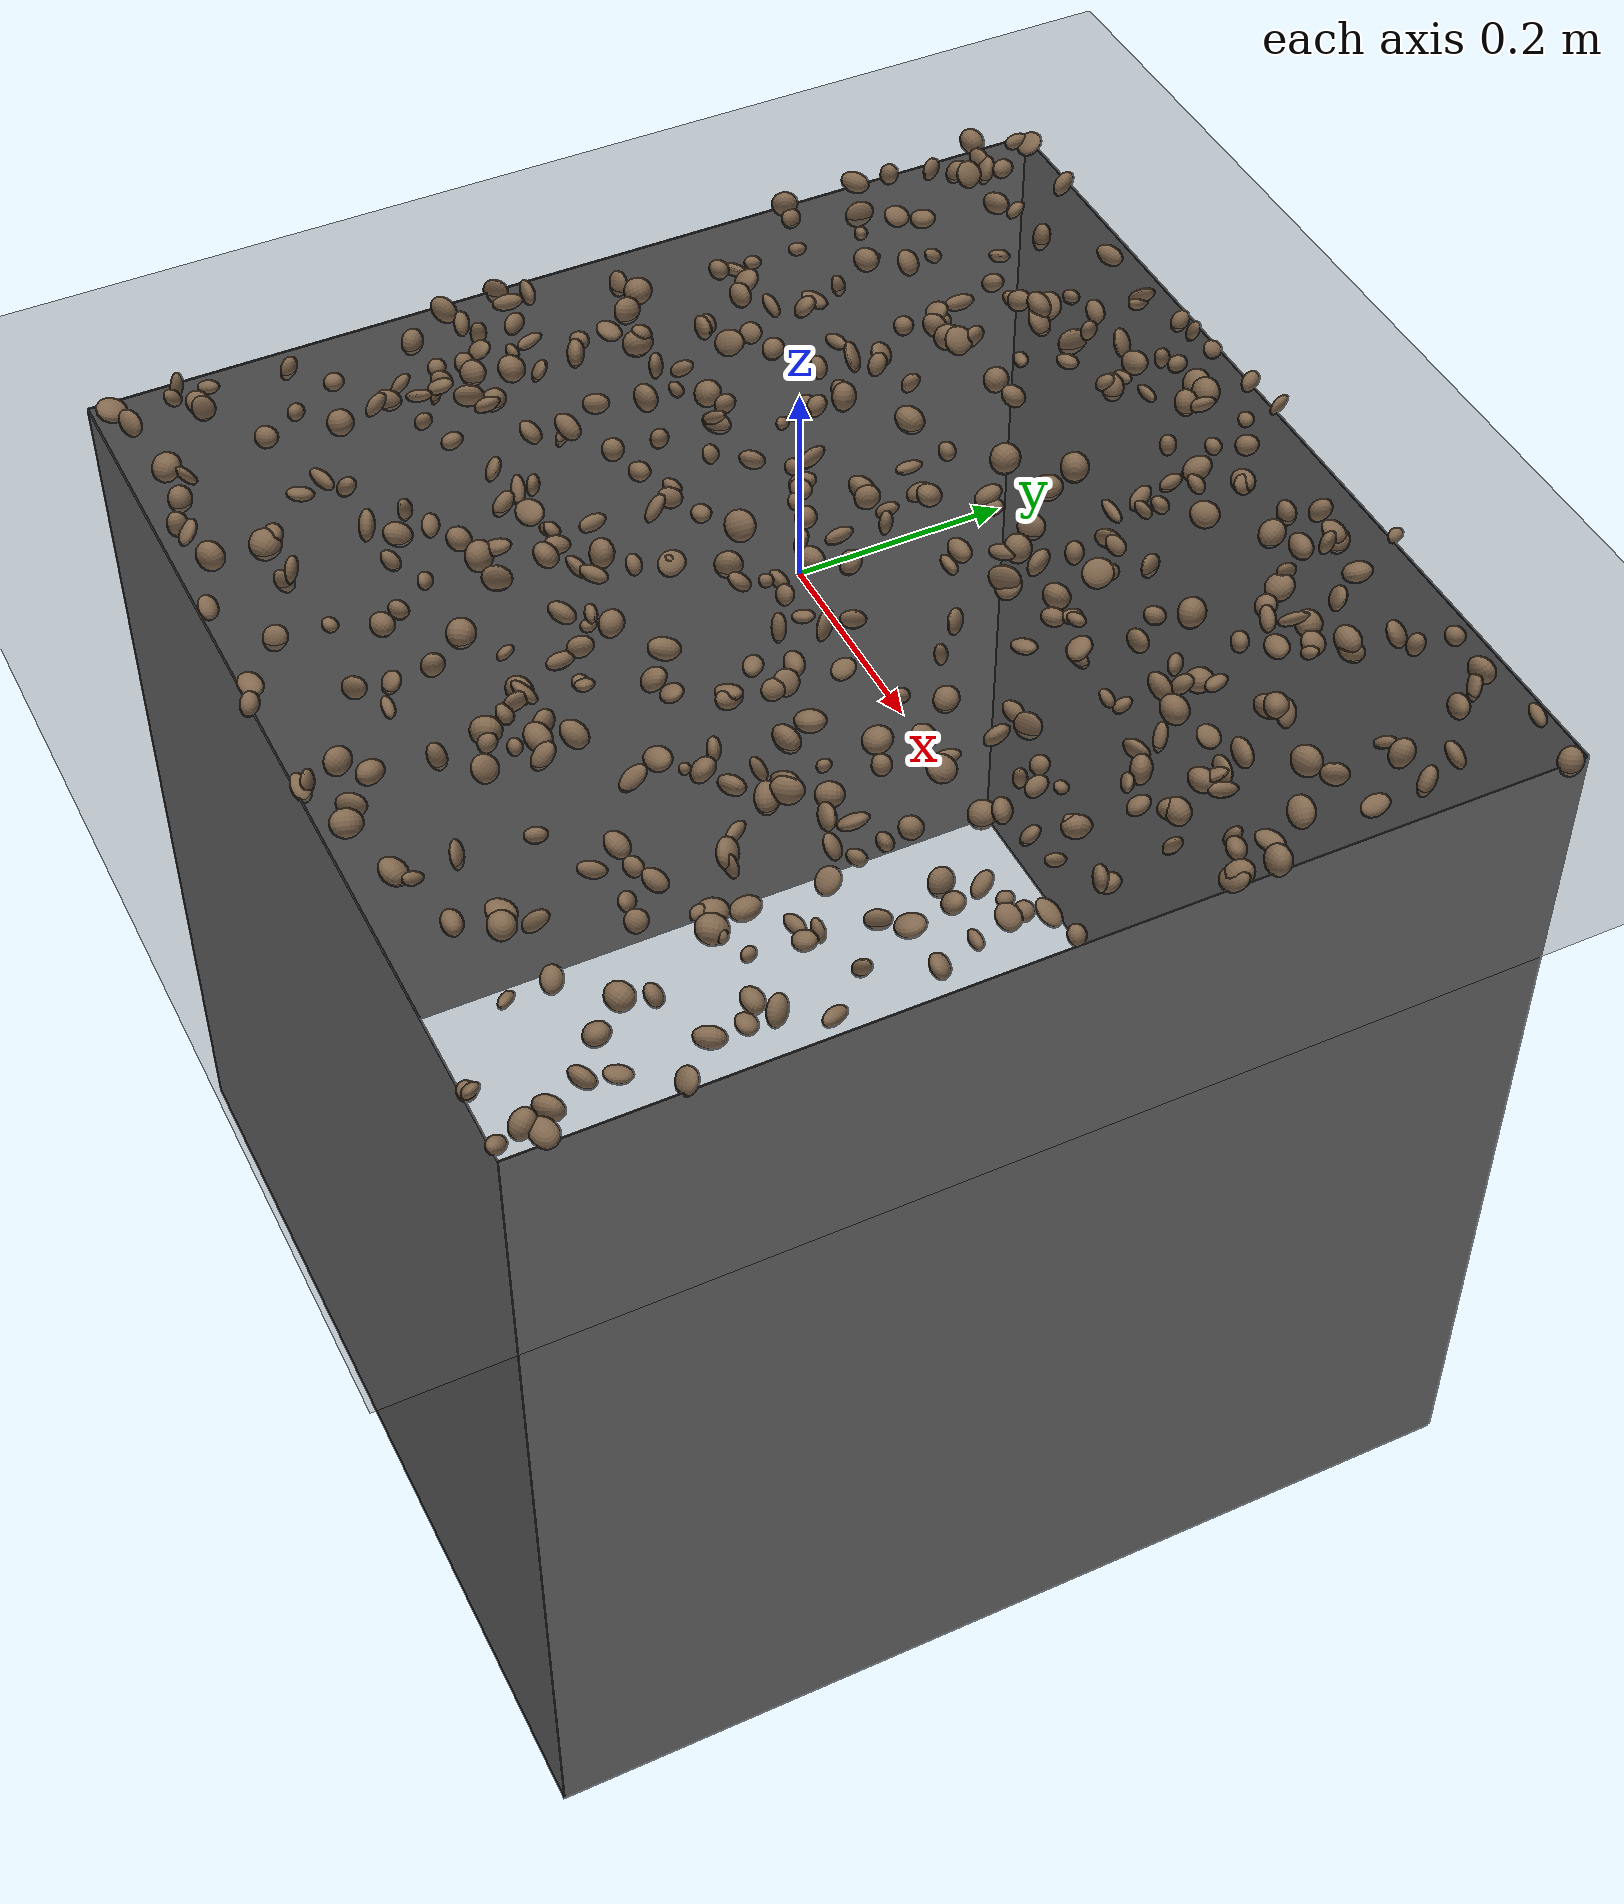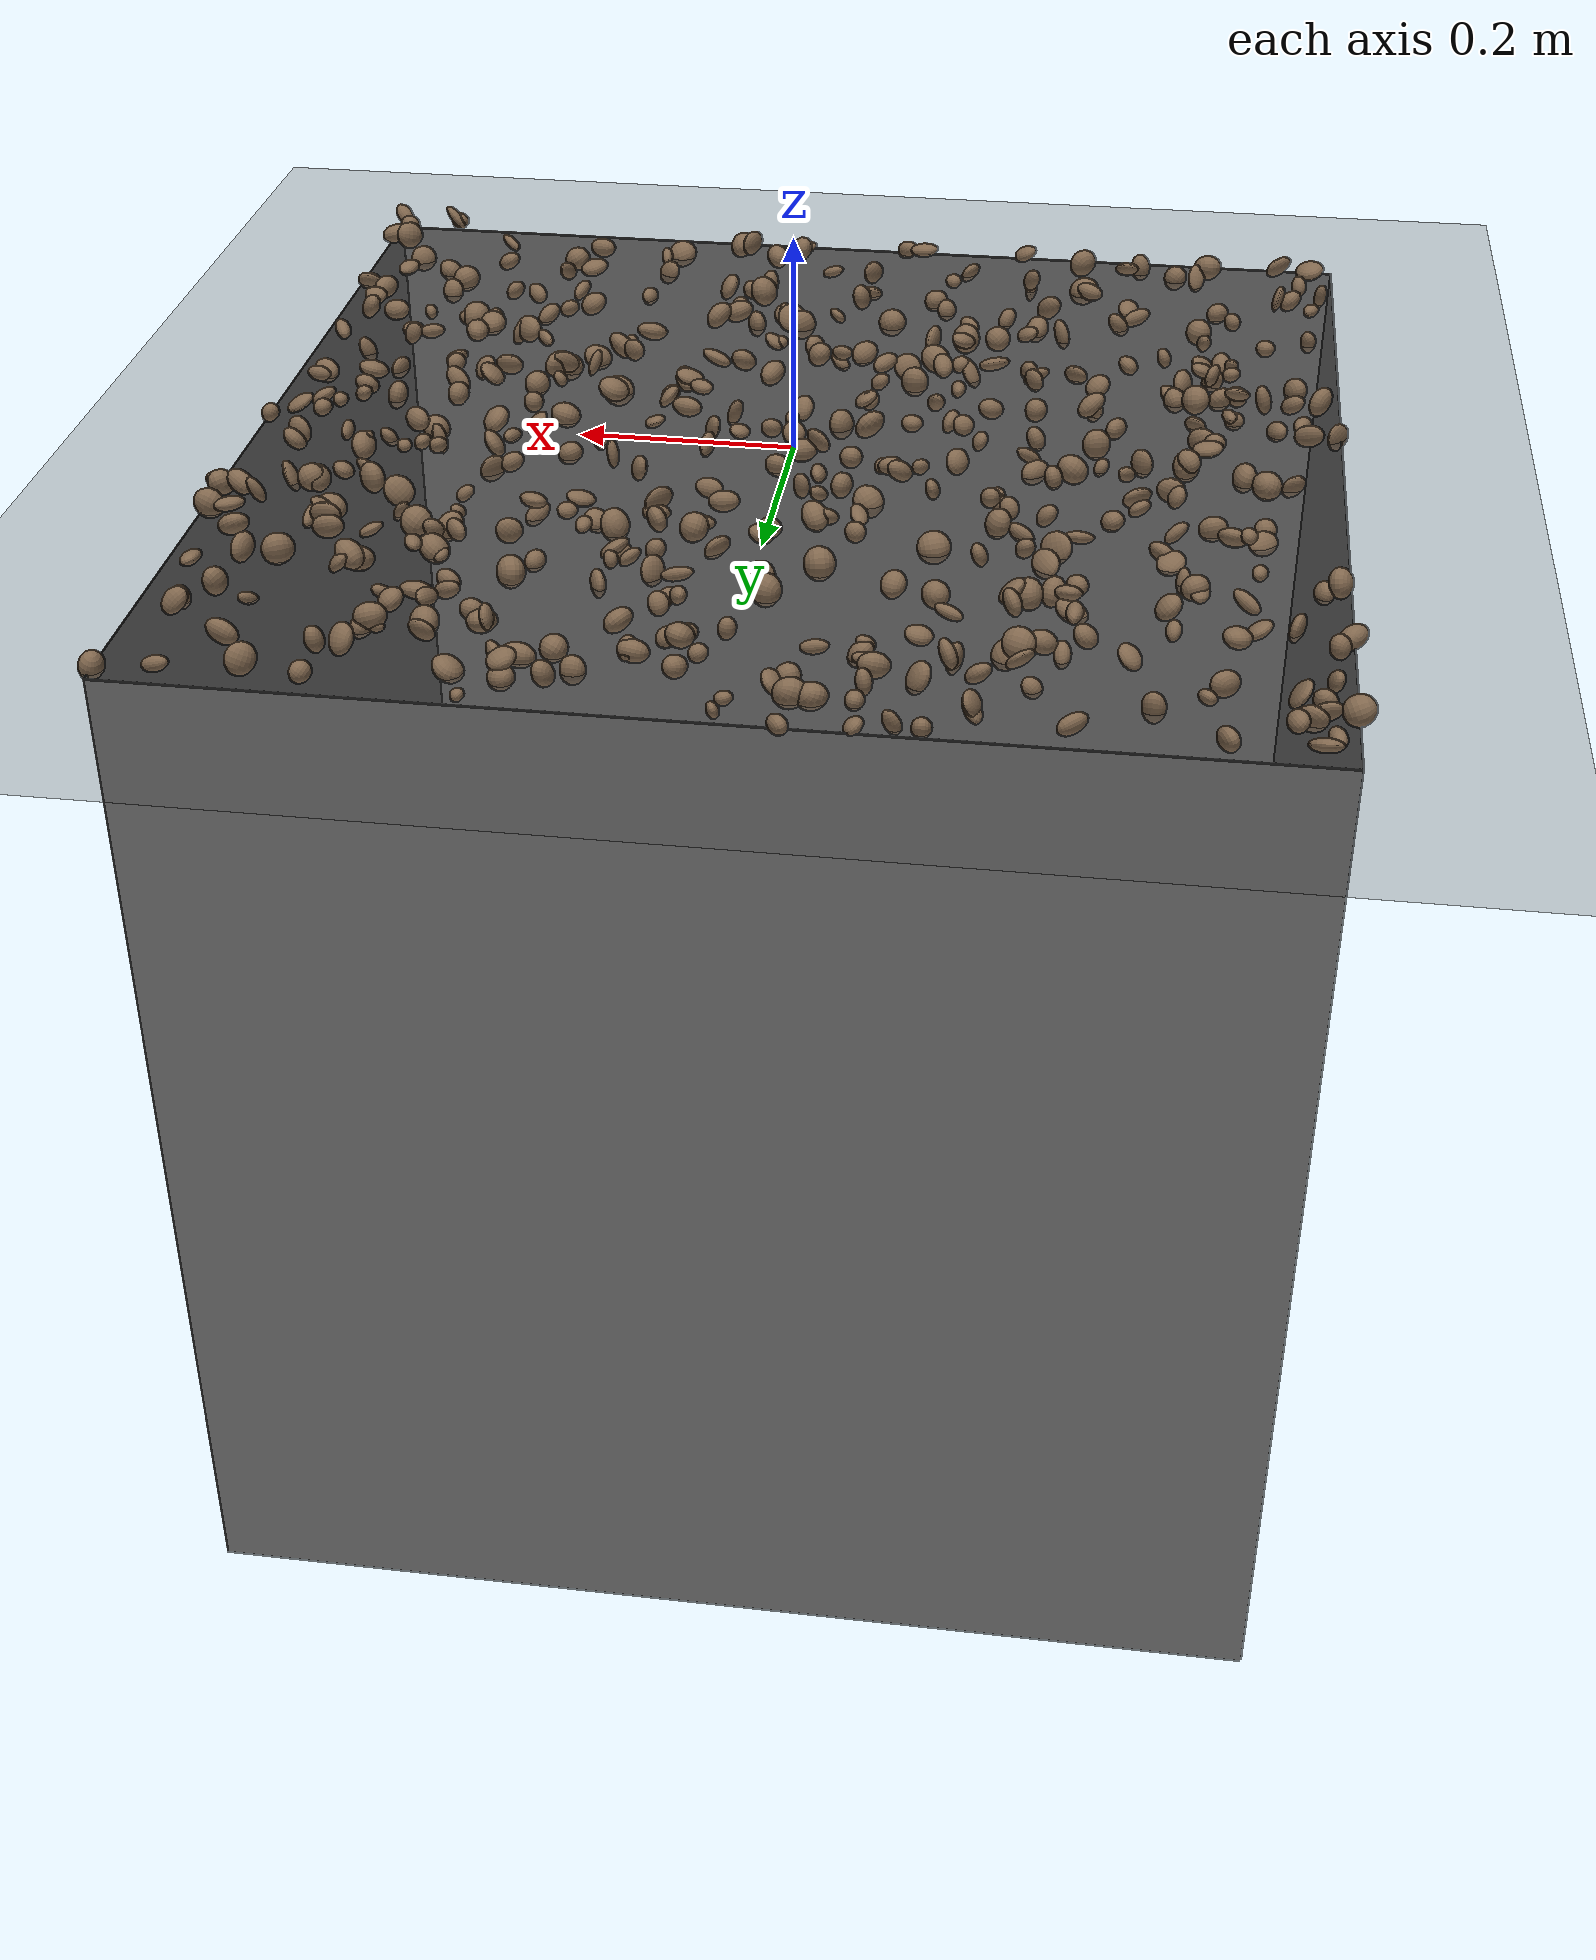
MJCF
<mujoco model="rocky_terrain_scene">
    <compiler angle="radian" inertiafromgeom="true" />
    <option timestep="0.002" gravity="0 0 -9.81" />

    <worldbody>
        <light name="sunlight" pos="5 5 5" dir="-1 -1 -1" diffuse="1 1 1" specular="0.5 0.5 0.5" ambient="0.5 0.5 0.5" />

        <geom name="ground_plane" type="plane" size="50 50 0.1" rgba="0.3 0.3 0.3 1" />

        <body name="rocky_terrain_body">

        </body>
    <body name="rock1" pos="0.13735972664209795 0.45697899888153126 0.00856766859907067"><joint type="free" /><geom type="ellipsoid" size="0.009741406509255429 0.012993434585267562 0.008631324855282375" quat="0.3211067948142254 0.25675410092953055 0.298749517935685 0.12338958632055912" rgba="0.5 0.4 0.3 1" friction="0.01 0.01 0.01" /><inertial pos="0.13735972664209795 0.45697899888153126 0.00856766859907067" quat="0.3211067948142254 0.25675410092953055 0.298749517935685 0.12338958632055912" mass="0.4335256972271525" diaginertia="0.1 0.1 0.1" /></body><body name="rock2" pos="-0.44428646767819835 -0.4040445717618014 0.007350564675914956"><joint type="free" /><geom type="ellipsoid" size="0.011015128775534313 0.013181768021496877 0.005038727821919645" quat="0.2686163826978642 0.2597831420013756 0.18318224724118784 0.2884182280595723" rgba="0.5 0.4 0.3 1" friction="0.01 0.01 0.01" /><inertial pos="-0.44428646767819835 -0.4040445717618014 0.007350564675914956" quat="0.2686163826978642 0.2597831420013756 0.18318224724118784 0.2884182280595723" mass="0.2016453836330642" diaginertia="0.1 0.1 0.1" /></body><body name="rock3" pos="0.38494196228480015 0.20723813389199597 0.008374586327350724"><joint type="free" /><geom type="ellipsoid" size="0.011941109001144996 0.005641243769650612 0.013875609619559293" quat="0.03870610282930467 0.5028269513907239 0.020561352275532803 0.4379055935044387" rgba="0.5 0.4 0.3 1" friction="0.01 0.01 0.01" /><inertial pos="0.38494196228480015 0.20723813389199597 0.008374586327350724" quat="0.03870610282930467 0.5028269513907239 0.020561352275532803 0.4379055935044387" mass="0.10491400363461373" diaginertia="0.1 0.1 0.1" /></body><body name="rock4" pos="-0.11990141252120401 0.41011627629426417 0.00987597792754622"><joint type="free" /><geom type="ellipsoid" size="0.011545799868262617 0.009865863276052916 0.0140038694829408" quat="0.0017545610625404964 0.3461156859495028 0.13470779707640232 0.5174219559115544" rgba="0.5 0.4 0.3 1" friction="0.01 0.01 0.01" /><inertial pos="-0.11990141252120401 0.41011627629426417 0.00987597792754622" quat="0.0017545610625404964 0.3461156859495028 0.13470779707640232 0.5174219559115544" mass="0.39260805432305446" diaginertia="0.1 0.1 0.1" /></body><body name="rock5" pos="-0.18132164344681667 0.377409394887132 0.002542653259514462"><joint type="free" /><geom type="ellipsoid" size="0.013421346089611663 0.014394066923402005 0.006342633731530644" quat="0.40263160358821964 0.15726533640630694 0.35364263851993566 0.08646042148553781" rgba="0.5 0.4 0.3 1" friction="0.01 0.01 0.01" /><inertial pos="-0.18132164344681667 0.377409394887132 0.002542653259514462" quat="0.40263160358821964 0.15726533640630694 0.35364263851993566 0.08646042148553781" mass="0.3028919658949407" diaginertia="0.1 0.1 0.1" /></body><body name="rock6" pos="-0.32025444404206316 0.37237899467293767 0.011750659354238737"><joint type="free" /><geom type="ellipsoid" size="0.012366944274662457 0.006035212517317302 0.01003998549303755" quat="0.2763834770970043 0.007554178569523876 0.3948915112642221 0.3211708330692497" rgba="0.5 0.4 0.3 1" friction="0.01 0.01 0.01" /><inertial pos="-0.32025444404206316 0.37237899467293767 0.011750659354238737" quat="0.2763834770970043 0.007554178569523876 0.3948915112642221 0.3211708330692497" mass="0.40448672345151004" diaginertia="0.1 0.1 0.1" /></body><body name="rock7" pos="0.05173039270952817 0.37739061048940836 0.0044645135555603285"><joint type="free" /><geom type="ellipsoid" size="0.008759712670556415 0.006876441387863518 0.010835669128934054" quat="0.2579385755999931 0.11068127046997131 0.5121937263034813 0.11918642762655418" rgba="0.5 0.4 0.3 1" friction="0.01 0.01 0.01" /><inertial pos="0.05173039270952817 0.37739061048940836 0.0044645135555603285" quat="0.2579385755999931 0.11068127046997131 0.5121937263034813 0.11918642762655418" mass="0.41716317996536945" diaginertia="0.1 0.1 0.1" /></body><body name="rock8" pos="0.06201372456953169 0.18654445821299637 0.007273260746758355"><joint type="free" /><geom type="ellipsoid" size="0.01266473971289557 0.013667538606685216 0.012346587293060218" quat="0.27471150809214057 0.1867108345030972 0.21674656266958456 0.32183109473517757" rgba="0.5 0.4 0.3 1" friction="0.01 0.01 0.01" /><inertial pos="0.06201372456953169 0.18654445821299637 0.007273260746758355" quat="0.27471150809214057 0.1867108345030972 0.21674656266958456 0.32183109473517757" mass="0.3556216057982172" diaginertia="0.1 0.1 0.1" /></body><body name="rock9" pos="0.4381738691427782 0.35046218187934086 0.013470975877064712"><joint type="free" /><geom type="ellipsoid" size="0.009979564372738711 0.014299240149321005 0.010927100810972982" quat="0.1321412400617994 0.08321586937794488 0.470084783391875 0.3145581071683807" rgba="0.5 0.4 0.3 1" friction="0.01 0.01 0.01" /><inertial pos="0.4381738691427782 0.35046218187934086 0.013470975877064712" quat="0.1321412400617994 0.08321586937794488 0.470084783391875 0.3145581071683807" mass="0.27236391468408755" diaginertia="0.1 0.1 0.1" /></body><body name="rock10" pos="0.49530402669835405 -0.49820995113567845 0.014014674199589615"><joint type="free" /><geom type="ellipsoid" size="0.008050699149193683 0.007571274623303781 0.013394022430062536" quat="0.5165144506033487 0.21978343802461262 0.15068032761572192 0.11302178375631676" rgba="0.5 0.4 0.3 1" friction="0.01 0.01 0.01" /><inertial pos="0.49530402669835405 -0.49820995113567845 0.014014674199589615" quat="0.5165144506033487 0.21978343802461262 0.15068032761572192 0.11302178375631676" mass="0.38605828441241485" diaginertia="0.1 0.1 0.1" /></body><body name="rock11" pos="0.28265818962458944 0.2275678447107694 0.011555270302150006"><joint type="free" /><geom type="ellipsoid" size="0.00733770320838679 0.01178201856683036 0.00784932928052931" quat="0.2786556987278285 0.21574699279469778 0.3905000036196775 0.11509730485779625" rgba="0.5 0.4 0.3 1" friction="0.01 0.01 0.01" /><inertial pos="0.28265818962458944 0.2275678447107694 0.011555270302150006" quat="0.2786556987278285 0.21574699279469778 0.3905000036196775 0.11509730485779625" mass="0.21883010918878623" diaginertia="0.1 0.1 0.1" /></body><body name="rock12" pos="0.40012095425305383 -0.3240216087386737 0.0016725038555882225"><joint type="free" /><geom type="ellipsoid" size="0.012162247466231896 0.007542822004848365 0.010446607621486605" quat="0.38379862903906437 0.12830177401997855 0.43186270060068815 0.05603689634026892" rgba="0.5 0.4 0.3 1" friction="0.01 0.01 0.01" /><inertial pos="0.40012095425305383 -0.3240216087386737 0.0016725038555882225" quat="0.38379862903906437 0.12830177401997855 0.43186270060068815 0.05603689634026892" mass="0.33537527182767796" diaginertia="0.1 0.1 0.1" /></body><body name="rock13" pos="-0.20200598309773388 0.464619775382217 0.013478854307867202"><joint type="free" /><geom type="ellipsoid" size="0.013132968559681938 0.010893791645917488 0.005190541545917487" quat="0.17401423670008306 0.42184165365573173 0.16525174845859766 0.23889236118558752" rgba="0.5 0.4 0.3 1" friction="0.01 0.01 0.01" /><inertial pos="-0.20200598309773388 0.464619775382217 0.013478854307867202" quat="0.17401423670008306 0.42184165365573173 0.16525174845859766 0.23889236118558752" mass="0.4673343223041776" diaginertia="0.1 0.1 0.1" /></body><body name="rock14" pos="-0.3882034060627332 -0.15596699250777624 0.002699089700433745"><joint type="free" /><geom type="ellipsoid" size="0.00922843777264011 0.012682020810625222 0.012247858010585299" quat="0.180359042556788 0.20965400494216122 0.5558096159413346 0.054177336559716155" rgba="0.5 0.4 0.3 1" friction="0.01 0.01 0.01" /><inertial pos="-0.3882034060627332 -0.15596699250777624 0.002699089700433745" quat="0.180359042556788 0.20965400494216122 0.5558096159413346 0.054177336559716155" mass="0.1584440359027351" diaginertia="0.1 0.1 0.1" /></body><body name="rock15" pos="-0.21128172221660724 -0.18386982008530794 0.003929206555250746"><joint type="free" /><geom type="ellipsoid" size="0.006052701122573886 0.006717266323034599 0.014518680450402492" quat="0.25545386964967887 0.25584841965893645 0.43925431906413936 0.04944339162724528" rgba="0.5 0.4 0.3 1" friction="0.01 0.01 0.01" /><inertial pos="-0.21128172221660724 -0.18386982008530794 0.003929206555250746" quat="0.25545386964967887 0.25584841965893645 0.43925431906413936 0.04944339162724528" mass="0.2575298009614658" diaginertia="0.1 0.1 0.1" /></body><body name="rock16" pos="0.4260692135787064 -0.1083743557192055 0.006236370628803026"><joint type="free" /><geom type="ellipsoid" size="0.013100199834775231 0.014422198657970571 0.007934192995620953" quat="0.03814388131225527 0.31712969342886754 0.5456078255535831 0.09911859970529407" rgba="0.5 0.4 0.3 1" friction="0.01 0.01 0.01" /><inertial pos="0.4260692135787064 -0.1083743557192055 0.006236370628803026" quat="0.03814388131225527 0.31712969342886754 0.5456078255535831 0.09911859970529407" mass="0.3013190683459116" diaginertia="0.1 0.1 0.1" /></body><body name="rock17" pos="0.4086785478363322 0.14476008843572308 0.011665433126557753"><joint type="free" /><geom type="ellipsoid" size="0.012977271267359113 0.012306991568605354 0.009190902597090413" quat="0.24251120486282238 0.34761552715952043 0.2702102939186231 0.1396629740590341" rgba="0.5 0.4 0.3 1" friction="0.01 0.01 0.01" /><inertial pos="0.4086785478363322 0.14476008843572308 0.011665433126557753" quat="0.24251120486282238 0.34761552715952043 0.2702102939186231 0.1396629740590341" mass="0.10578415261685566" diaginertia="0.1 0.1 0.1" /></body><body name="rock18" pos="-0.26985903294547176 0.16921487004635205 0.011906406537144205"><joint type="free" /><geom type="ellipsoid" size="0.00652786891835468 0.005262129201504313 0.01354593639604645" quat="0.12383498038338946 0.2978879373486418 0.18703747696412956 0.3912396053038391" rgba="0.5 0.4 0.3 1" friction="0.01 0.01 0.01" /><inertial pos="-0.26985903294547176 0.16921487004635205 0.011906406537144205" quat="0.12383498038338946 0.2978879373486418 0.18703747696412956 0.3912396053038391" mass="0.22560146527328398" diaginertia="0.1 0.1 0.1" /></body><body name="rock19" pos="-0.20208183678559033 0.4612137616630685 0.005908145803980486"><joint type="free" /><geom type="ellipsoid" size="0.013663164066313582 0.008240371352324756 0.006324188738624996" quat="0.2018167701135565 0.2494296437330905 0.486556991585574 0.062196594567779075" rgba="0.5 0.4 0.3 1" friction="0.01 0.01 0.01" /><inertial pos="-0.20208183678559033 0.4612137616630685 0.005908145803980486" quat="0.2018167701135565 0.2494296437330905 0.486556991585574 0.062196594567779075" mass="0.4523493103743995" diaginertia="0.1 0.1 0.1" /></body><body name="rock20" pos="0.11874558001542868 0.43338954900359805 2.101526050137359e-05"><joint type="free" /><geom type="ellipsoid" size="0.008501630714117317 0.012620711338377378 0.010784244056638947" quat="0.24644803004173385 0.26936639485933883 0.22074673029140301 0.26343884480752433" rgba="0.5 0.4 0.3 1" friction="0.01 0.01 0.01" /><inertial pos="0.11874558001542868 0.43338954900359805 2.101526050137359e-05" quat="0.24644803004173385 0.26936639485933883 0.22074673029140301 0.26343884480752433" mass="0.21633045572689522" diaginertia="0.1 0.1 0.1" /></body><body name="rock21" pos="-0.4718140021980115 0.4879557426440515 0.011680047406222312"><joint type="free" /><geom type="ellipsoid" size="0.013155397070352532 0.005831210175856468 0.014118660387856155" quat="0.20752914341078163 0.3673826669114739 0.15297881368106836 0.272109375996676" rgba="0.5 0.4 0.3 1" friction="0.01 0.01 0.01" /><inertial pos="-0.4718140021980115 0.4879557426440515 0.011680047406222312" quat="0.20752914341078163 0.3673826669114739 0.15297881368106836 0.272109375996676" mass="0.4894496506173682" diaginertia="0.1 0.1 0.1" /></body><body name="rock22" pos="0.4514178241121798 -0.01763830253643539 0.0049132081103312976"><joint type="free" /><geom type="ellipsoid" size="0.008979270458191666 0.008053077948543014 0.009018127626484317" quat="0.2759887911380493 0.3425503538155308 0.27453677214105204 0.10692408290536792" rgba="0.5 0.4 0.3 1" friction="0.01 0.01 0.01" /><inertial pos="0.4514178241121798 -0.01763830253643539 0.0049132081103312976" quat="0.2759887911380493 0.3425503538155308 0.27453677214105204 0.10692408290536792" mass="0.4167944777219429" diaginertia="0.1 0.1 0.1" /></body><body name="rock23" pos="-0.07286055026317828 -0.49174992116203753 0.006604849581410832"><joint type="free" /><geom type="ellipsoid" size="0.011058719398183162 0.006281129387765947 0.014465809473145158" quat="0.2404401253942556 0.2492238324498026 0.2663071921784959 0.24402884997744595" rgba="0.5 0.4 0.3 1" friction="0.01 0.01 0.01" /><inertial pos="-0.07286055026317828 -0.49174992116203753 0.006604849581410832" quat="0.2404401253942556 0.2492238324498026 0.2663071921784959 0.24402884997744595" mass="0.1509450472311801" diaginertia="0.1 0.1 0.1" /></body><body name="rock24" pos="-0.06687702451737287 -0.02781150340751548 0.014906344267696978"><joint type="free" /><geom type="ellipsoid" size="0.014599234671761555 0.009271624392401121 0.01488678044618168" quat="0.08595488323581797 0.490522965729391 0.25431341212594305 0.169208738908848" rgba="0.5 0.4 0.3 1" friction="0.01 0.01 0.01" /><inertial pos="-0.06687702451737287 -0.02781150340751548 0.014906344267696978" quat="0.08595488323581797 0.490522965729391 0.25431341212594305 0.169208738908848" mass="0.3354569867607252" diaginertia="0.1 0.1 0.1" /></body><body name="rock25" pos="0.4923296240546209 -0.33745361487560144 0.002137691131337306"><joint type="free" /><geom type="ellipsoid" size="0.012470437394059125 0.0066507128904120345 0.012425918363393525" quat="0.08405216821695013 0.2819724960161286 0.1579064985277634 0.47606883723915777" rgba="0.5 0.4 0.3 1" friction="0.01 0.01 0.01" /><inertial pos="0.4923296240546209 -0.33745361487560144 0.002137691131337306" quat="0.08405216821695013 0.2819724960161286 0.1579064985277634 0.47606883723915777" mass="0.21182807118566457" diaginertia="0.1 0.1 0.1" /></body><body name="rock26" pos="0.07359611431955582 -0.1766729781015851 0.006853794428602467"><joint type="free" /><geom type="ellipsoid" size="0.009036917173334708 0.013760795651289067 0.010937968127970366" quat="0.3342982699162669 0.24465403351338985 0.3573572147258511 0.06369048184449227" rgba="0.5 0.4 0.3 1" friction="0.01 0.01 0.01" /><inertial pos="0.07359611431955582 -0.1766729781015851 0.006853794428602467" quat="0.3342982699162669 0.24465403351338985 0.3573572147258511 0.06369048184449227" mass="0.20250888118571864" diaginertia="0.1 0.1 0.1" /></body><body name="rock27" pos="-0.13513982142417047 0.07729416655276544 0.004090340760870047"><joint type="free" /><geom type="ellipsoid" size="0.009413986878281138 0.014429303402303539 0.006212406034062785" quat="0.33100538421364695 0.09635297193609574 0.44244866944116135 0.13019297440909594" rgba="0.5 0.4 0.3 1" friction="0.01 0.01 0.01" /><inertial pos="-0.13513982142417047 0.07729416655276544 0.004090340760870047" quat="0.33100538421364695 0.09635297193609574 0.44244866944116135 0.13019297440909594" mass="0.2804428559876767" diaginertia="0.1 0.1 0.1" /></body><body name="rock28" pos="-0.3646759210192366 -0.2976312644382324 0.010662042627907221"><joint type="free" /><geom type="ellipsoid" size="0.012507454902084773 0.012400660563327857 0.012552747730493408" quat="0.05769396747549177 0.3529130294193518 0.5367715429968357 0.05262146010832078" rgba="0.5 0.4 0.3 1" friction="0.01 0.01 0.01" /><inertial pos="-0.3646759210192366 -0.2976312644382324 0.010662042627907221" quat="0.05769396747549177 0.3529130294193518 0.5367715429968357 0.05262146010832078" mass="0.15338373193869836" diaginertia="0.1 0.1 0.1" /></body><body name="rock29" pos="-0.26999925666126146 0.2828338128012525 0.000779374425392913"><joint type="free" /><geom type="ellipsoid" size="0.014936140293914078 0.0068279190094376226 0.009586882789571155" quat="0.159964806216545 0.0036936050466145694 0.5921515577195513 0.2441900310172891" rgba="0.5 0.4 0.3 1" friction="0.01 0.01 0.01" /><inertial pos="-0.26999925666126146 0.2828338128012525 0.000779374425392913" quat="0.159964806216545 0.0036936050466145694 0.5921515577195513 0.2441900310172891" mass="0.39358033440830853" diaginertia="0.1 0.1 0.1" /></body><body name="rock30" pos="0.0990715507620189 0.15266084481807674 0.014789546666722664"><joint type="free" /><geom type="ellipsoid" size="0.005327097458854853 0.01276626999086081 0.014829247882156206" quat="0.18144551863286074 0.09531905598862672 0.36388857532119195 0.3593468500573206" rgba="0.5 0.4 0.3 1" friction="0.01 0.01 0.01" /><inertial pos="0.0990715507620189 0.15266084481807674 0.014789546666722664" quat="0.18144551863286074 0.09531905598862672 0.36388857532119195 0.3593468500573206" mass="0.1718660572250466" diaginertia="0.1 0.1 0.1" /></body><body name="rock31" pos="-0.3953261061360206 0.4086714825172746 0.013816094308480001"><joint type="free" /><geom type="ellipsoid" size="0.013318462982474202 0.011366638499292682 0.008595301468196113" quat="0.36685901743424726 0.40175126271762956 0.08617503936011003 0.14521468048801306" rgba="0.5 0.4 0.3 1" friction="0.01 0.01 0.01" /><inertial pos="-0.3953261061360206 0.4086714825172746 0.013816094308480001" quat="0.36685901743424726 0.40175126271762956 0.08617503936011003 0.14521468048801306" mass="0.4517425359112468" diaginertia="0.1 0.1 0.1" /></body><body name="rock32" pos="-0.1256063139150787 -0.45045870766166385 0.00039071968557617074"><joint type="free" /><geom type="ellipsoid" size="0.012211787048561731 0.011021830442586832 0.0061617938680697155" quat="0.27427765463946807 0.2761657329368418 0.008326620159207198 0.44122999226448295" rgba="0.5 0.4 0.3 1" friction="0.01 0.01 0.01" /><inertial pos="-0.1256063139150787 -0.45045870766166385 0.00039071968557617074" quat="0.27427765463946807 0.2761657329368418 0.008326620159207198 0.44122999226448295" mass="0.44487083795044435" diaginertia="0.1 0.1 0.1" /></body><body name="rock33" pos="0.07682054940496352 -0.3793582050425637 0.0041581544132519065"><joint type="free" /><geom type="ellipsoid" size="0.008098617009295008 0.014849325544094641 0.008464530368785205" quat="0.3654919649135055 0.4394356758747283 0.06793363020300361 0.1271387290087625" rgba="0.5 0.4 0.3 1" friction="0.01 0.01 0.01" /><inertial pos="0.07682054940496352 -0.3793582050425637 0.0041581544132519065" quat="0.3654919649135055 0.4394356758747283 0.06793363020300361 0.1271387290087625" mass="0.1630147284995384" diaginertia="0.1 0.1 0.1" /></body><body name="rock34" pos="-0.4740486651450513 0.405638148192093 0.0022223556077241575"><joint type="free" /><geom type="ellipsoid" size="0.01023276034537314 0.008896816062467464 0.012704352795305237" quat="0.1419588047969494 0.07652751757207549 0.1595886025116268 0.6219250751193484" rgba="0.5 0.4 0.3 1" friction="0.01 0.01 0.01" /><inertial pos="-0.4740486651450513 0.405638148192093 0.0022223556077241575" quat="0.1419588047969494 0.07652751757207549 0.1595886025116268 0.6219250751193484" mass="0.19666879783988112" diaginertia="0.1 0.1 0.1" /></body><body name="rock35" pos="-0.001066139643853048 -0.059313373277574244 0.013199751111671652"><joint type="free" /><geom type="ellipsoid" size="0.006927809500065877 0.012488489833036753 0.00910748439541617" quat="0.16127911515932486 0.3643005800885325 0.12306686313528088 0.35135344161686183" rgba="0.5 0.4 0.3 1" friction="0.01 0.01 0.01" /><inertial pos="-0.001066139643853048 -0.059313373277574244 0.013199751111671652" quat="0.16127911515932486 0.3643005800885325 0.12306686313528088 0.35135344161686183" mass="0.27747601040771275" diaginertia="0.1 0.1 0.1" /></body><body name="rock36" pos="0.43947735344023353 0.12798700442414346 0.0037024922492260408"><joint type="free" /><geom type="ellipsoid" size="0.009212498832047347 0.005307167343414244 0.014673048305689131" quat="0.4215460804208897 0.12389157846644883 0.04574038809993826 0.40882195301272317" rgba="0.5 0.4 0.3 1" friction="0.01 0.01 0.01" /><inertial pos="0.43947735344023353 0.12798700442414346 0.0037024922492260408" quat="0.4215460804208897 0.12389157846644883 0.04574038809993826 0.40882195301272317" mass="0.3630633268006762" diaginertia="0.1 0.1 0.1" /></body><body name="rock37" pos="-0.09746563838322542 -0.36082918329990377 0.003633092106801985"><joint type="free" /><geom type="ellipsoid" size="0.01167723162523785 0.010440655790626929 0.010793383935375434" quat="0.30296925384531587 0.520282772717571 0.16907131619377605 0.007676657243337098" rgba="0.5 0.4 0.3 1" friction="0.01 0.01 0.01" /><inertial pos="-0.09746563838322542 -0.36082918329990377 0.003633092106801985" quat="0.30296925384531587 0.520282772717571 0.16907131619377605 0.007676657243337098" mass="0.26987730351226336" diaginertia="0.1 0.1 0.1" /></body><body name="rock38" pos="0.469641231873397 -0.07224441536422388 0.014629788438940906"><joint type="free" /><geom type="ellipsoid" size="0.005729703351414262 0.007238678349752357 0.011403445017792932" quat="0.244512811149975 0.2746272119516072 0.19770296178413788 0.28315701511427993" rgba="0.5 0.4 0.3 1" friction="0.01 0.01 0.01" /><inertial pos="0.469641231873397 -0.07224441536422388 0.014629788438940906" quat="0.244512811149975 0.2746272119516072 0.19770296178413788 0.28315701511427993" mass="0.25026593834722166" diaginertia="0.1 0.1 0.1" /></body><body name="rock39" pos="-0.40114069941121266 0.13661572044008496 0.00432301293468253"><joint type="free" /><geom type="ellipsoid" size="0.007786461923159651 0.013046058187570646 0.013649626127612627" quat="0.4427009924480003 0.014171344190609296 0.2974736053956057 0.24565405796578468" rgba="0.5 0.4 0.3 1" friction="0.01 0.01 0.01" /><inertial pos="-0.40114069941121266 0.13661572044008496 0.00432301293468253" quat="0.4427009924480003 0.014171344190609296 0.2974736053956057 0.24565405796578468" mass="0.2255595063646174" diaginertia="0.1 0.1 0.1" /></body><body name="rock40" pos="-0.39699437388562964 -0.18826730150628823 0.01442301816031813"><joint type="free" /><geom type="ellipsoid" size="0.008526492268248738 0.006966523740460244 0.008635727568142668" quat="0.2616445942112281 0.4203860027513211 0.18773261254381793 0.1302367904936329" rgba="0.5 0.4 0.3 1" friction="0.01 0.01 0.01" /><inertial pos="-0.39699437388562964 -0.18826730150628823 0.01442301816031813" quat="0.2616445942112281 0.4203860027513211 0.18773261254381793 0.1302367904936329" mass="0.39625000943176913" diaginertia="0.1 0.1 0.1" /></body><body name="rock41" pos="-0.332218183643782 -0.22776835870297196 0.011161014010810376"><joint type="free" /><geom type="ellipsoid" size="0.008488535311585884 0.009748192056368765 0.006326944028582296" quat="0.20342971075090263 0.2637264976510085 0.3106871375515858 0.22215665404650312" rgba="0.5 0.4 0.3 1" friction="0.01 0.01 0.01" /><inertial pos="-0.332218183643782 -0.22776835870297196 0.011161014010810376" quat="0.20342971075090263 0.2637264976510085 0.3106871375515858 0.22215665404650312" mass="0.11235568469044815" diaginertia="0.1 0.1 0.1" /></body><body name="rock42" pos="0.4546937783205123 -0.03418677834770445 0.009143919997459563"><joint type="free" /><geom type="ellipsoid" size="0.010883865900089012 0.01254050402052429 0.006242470871415786" quat="0.3584360352988417 0.1458389838651531 0.07331902119886972 0.4224059596371355" rgba="0.5 0.4 0.3 1" friction="0.01 0.01 0.01" /><inertial pos="0.4546937783205123 -0.03418677834770445 0.009143919997459563" quat="0.3584360352988417 0.1458389838651531 0.07331902119886972 0.4224059596371355" mass="0.3250302046302309" diaginertia="0.1 0.1 0.1" /></body><body name="rock43" pos="-0.34139731664755246 0.43148179550296495 0.0012665687713656658"><joint type="free" /><geom type="ellipsoid" size="0.008051371916567476 0.01458447756287369 0.00986735159460076" quat="0.28078383959692926 0.25381632860828585 0.25560950657955134 0.20979032521523347" rgba="0.5 0.4 0.3 1" friction="0.01 0.01 0.01" /><inertial pos="-0.34139731664755246 0.43148179550296495 0.0012665687713656658" quat="0.28078383959692926 0.25381632860828585 0.25560950657955134 0.20979032521523347" mass="0.2225010290780699" diaginertia="0.1 0.1 0.1" /></body><body name="rock44" pos="-0.0583948882814207 0.45208629938834 0.0037861928571491362"><joint type="free" /><geom type="ellipsoid" size="0.012089581878105679 0.014646817465509998 0.014136018540015397" quat="0.3431832510627579 0.07470328770501099 0.26673138535392343 0.31538207587830774" rgba="0.5 0.4 0.3 1" friction="0.01 0.01 0.01" /><inertial pos="-0.0583948882814207 0.45208629938834 0.0037861928571491362" quat="0.3431832510627579 0.07470328770501099 0.26673138535392343 0.31538207587830774" mass="0.4615500074008907" diaginertia="0.1 0.1 0.1" /></body><body name="rock45" pos="0.46007287777021566 0.3894985088965419 0.01434390946538414"><joint type="free" /><geom type="ellipsoid" size="0.013562420285451047 0.006767556649948239 0.009825763392244483" quat="0.5550323501459805 0.1668602588261605 0.26436175822733865 0.013745632800520375" rgba="0.5 0.4 0.3 1" friction="0.01 0.01 0.01" /><inertial pos="0.46007287777021566 0.3894985088965419 0.01434390946538414" quat="0.5550323501459805 0.1668602588261605 0.26436175822733865 0.013745632800520375" mass="0.19006828491746522" diaginertia="0.1 0.1 0.1" /></body><body name="rock46" pos="-0.05512329625781154 0.4994061690184347 0.002679342171045867"><joint type="free" /><geom type="ellipsoid" size="0.011715629896559894 0.008695676886613752 0.007579005902180157" quat="0.10941440839700416 0.23457632457349753 0.35280097827125084 0.3032082887582475" rgba="0.5 0.4 0.3 1" friction="0.01 0.01 0.01" /><inertial pos="-0.05512329625781154 0.4994061690184347 0.002679342171045867" quat="0.10941440839700416 0.23457632457349753 0.35280097827125084 0.3032082887582475" mass="0.3569096660021319" diaginertia="0.1 0.1 0.1" /></body><body name="rock47" pos="0.1660254998809385 0.41952780548140745 0.0024585757487713394"><joint type="free" /><geom type="ellipsoid" size="0.010935509006294652 0.010123844045329268 0.014685130723799972" quat="0.08262965759376084 0.4293278380493787 0.03690280478184295 0.45113969957501754" rgba="0.5 0.4 0.3 1" friction="0.01 0.01 0.01" /><inertial pos="0.1660254998809385 0.41952780548140745 0.0024585757487713394" quat="0.08262965759376084 0.4293278380493787 0.03690280478184295 0.45113969957501754" mass="0.2796052208073234" diaginertia="0.1 0.1 0.1" /></body><body name="rock48" pos="0.18389589501080605 -0.08004881732571856 0.012226758642630942"><joint type="free" /><geom type="ellipsoid" size="0.01346977407155836 0.014711880066492131 0.00978128815156419" quat="0.13300068998156933 0.32602474849903446 0.5028916283119947 0.03808293320740154" rgba="0.5 0.4 0.3 1" friction="0.01 0.01 0.01" /><inertial pos="0.18389589501080605 -0.08004881732571856 0.012226758642630942" quat="0.13300068998156933 0.32602474849903446 0.5028916283119947 0.03808293320740154" mass="0.1214153171029869" diaginertia="0.1 0.1 0.1" /></body><body name="rock49" pos="0.26854349618736184 -0.2829833543766114 0.006450169500969077"><joint type="free" /><geom type="ellipsoid" size="0.008680507013159774 0.006999806764249246 0.009723702908454094" quat="0.005353807116494978 0.4467844394090732 0.21658190666857455 0.3312798468058572" rgba="0.5 0.4 0.3 1" friction="0.01 0.01 0.01" /><inertial pos="0.26854349618736184 -0.2829833543766114 0.006450169500969077" quat="0.005353807116494978 0.4467844394090732 0.21658190666857455 0.3312798468058572" mass="0.45028044192689975" diaginertia="0.1 0.1 0.1" /></body><body name="rock50" pos="0.0964536850358717 -0.2947326767973838 0.008138699714903821"><joint type="free" /><geom type="ellipsoid" size="0.011730312561006317 0.01020625814092143 0.014194418525718632" quat="0.14578275323762988 0.3045862158115568 0.29044803354073717 0.2591829974100762" rgba="0.5 0.4 0.3 1" friction="0.01 0.01 0.01" /><inertial pos="0.0964536850358717 -0.2947326767973838 0.008138699714903821" quat="0.14578275323762988 0.3045862158115568 0.29044803354073717 0.2591829974100762" mass="0.2215299741433912" diaginertia="0.1 0.1 0.1" /></body><body name="rock51" pos="0.041567212598243475 -0.1521143120188857 0.006024717746996008"><joint type="free" /><geom type="ellipsoid" size="0.010265757315833193 0.010521300772399185 0.014999617555856187" quat="0.055081709716523375 0.10918292709145422 0.4620127790899111 0.3737225841021113" rgba="0.5 0.4 0.3 1" friction="0.01 0.01 0.01" /><inertial pos="0.041567212598243475 -0.1521143120188857 0.006024717746996008" quat="0.055081709716523375 0.10918292709145422 0.4620127790899111 0.3737225841021113" mass="0.12892131539838775" diaginertia="0.1 0.1 0.1" /></body><body name="rock52" pos="-0.38375993623289284 -0.04800380306572127 0.00681761558999764"><joint type="free" /><geom type="ellipsoid" size="0.008672668102511228 0.009223866597388802 0.010113581487435108" quat="0.3384537507740679 0.06190911768421589 0.2748042397083566 0.32483289183335956" rgba="0.5 0.4 0.3 1" friction="0.01 0.01 0.01" /><inertial pos="-0.38375993623289284 -0.04800380306572127 0.00681761558999764" quat="0.3384537507740679 0.06190911768421589 0.2748042397083566 0.32483289183335956" mass="0.3499717871451805" diaginertia="0.1 0.1 0.1" /></body><body name="rock53" pos="-0.13596275201191066 -0.23558030224641435 0.014711572873681626"><joint type="free" /><geom type="ellipsoid" size="0.014099254313525749 0.006868793864448482 0.010126735490661695" quat="0.3429331342183766 0.32004210015258444 0.09524992660202794 0.241774839027011" rgba="0.5 0.4 0.3 1" friction="0.01 0.01 0.01" /><inertial pos="-0.13596275201191066 -0.23558030224641435 0.014711572873681626" quat="0.3429331342183766 0.32004210015258444 0.09524992660202794 0.241774839027011" mass="0.11325031203866742" diaginertia="0.1 0.1 0.1" /></body><body name="rock54" pos="0.46567093017492167 -0.2467006777396331 0.012171135376668684"><joint type="free" /><geom type="ellipsoid" size="0.010021689278393107 0.014329803598370834 0.008059128562224916" quat="0.34064423861084137 0.07948586069965957 0.2974937742349837 0.28237612645451526" rgba="0.5 0.4 0.3 1" friction="0.01 0.01 0.01" /><inertial pos="0.46567093017492167 -0.2467006777396331 0.012171135376668684" quat="0.34064423861084137 0.07948586069965957 0.2974937742349837 0.28237612645451526" mass="0.20484574651154414" diaginertia="0.1 0.1 0.1" /></body><body name="rock55" pos="-0.45457121854026994 0.023897832360188054 0.00218654350854167"><joint type="free" /><geom type="ellipsoid" size="0.005529889807427809 0.012432713044500492 0.010513281665526788" quat="0.28223551485528875 0.1017341784522863 0.29170194745749256 0.32432835923493236" rgba="0.5 0.4 0.3 1" friction="0.01 0.01 0.01" /><inertial pos="-0.45457121854026994 0.023897832360188054 0.00218654350854167" quat="0.28223551485528875 0.1017341784522863 0.29170194745749256 0.32432835923493236" mass="0.2823091322906386" diaginertia="0.1 0.1 0.1" /></body><body name="rock56" pos="0.3300247934179469 -0.058755351913515774 0.007977208710896671"><joint type="free" /><geom type="ellipsoid" size="0.009855716482582618 0.010369595935655646 0.011241525971923221" quat="0.05415699800253879 0.013708141863220932 0.6453243365636532 0.286810523570587" rgba="0.5 0.4 0.3 1" friction="0.01 0.01 0.01" /><inertial pos="0.3300247934179469 -0.058755351913515774 0.007977208710896671" quat="0.05415699800253879 0.013708141863220932 0.6453243365636532 0.286810523570587" mass="0.29349460843586606" diaginertia="0.1 0.1 0.1" /></body><body name="rock57" pos="0.4343719349246792 0.2868614143587862 0.013073636262453845"><joint type="free" /><geom type="ellipsoid" size="0.011628506737977187 0.013884125918922276 0.007784412360684196" quat="0.19656737262331683 0.4295538349523394 0.05289311837988842 0.32098567404445544" rgba="0.5 0.4 0.3 1" friction="0.01 0.01 0.01" /><inertial pos="0.4343719349246792 0.2868614143587862 0.013073636262453845" quat="0.19656737262331683 0.4295538349523394 0.05289311837988842 0.32098567404445544" mass="0.49268580822926644" diaginertia="0.1 0.1 0.1" /></body><body name="rock58" pos="0.03734591869511228 0.21375133757093334 0.003291419798334718"><joint type="free" /><geom type="ellipsoid" size="0.01298811250577725 0.01276124028218199 0.0059807434541908145" quat="0.4049126036813307 0.27493165054154556 0.08981951613682664 0.230336229640297" rgba="0.5 0.4 0.3 1" friction="0.01 0.01 0.01" /><inertial pos="0.03734591869511228 0.21375133757093334 0.003291419798334718" quat="0.4049126036813307 0.27493165054154556 0.08981951613682664 0.230336229640297" mass="0.1437590009249693" diaginertia="0.1 0.1 0.1" /></body><body name="rock59" pos="-0.4306202442110012 0.034213281459827494 0.00609075293955495"><joint type="free" /><geom type="ellipsoid" size="0.013633424010187096 0.013002727339098907 0.01382198877597747" quat="0.19492338023292463 0.061368323943888976 0.25847149387977647 0.48523680194340996" rgba="0.5 0.4 0.3 1" friction="0.01 0.01 0.01" /><inertial pos="-0.4306202442110012 0.034213281459827494 0.00609075293955495" quat="0.19492338023292463 0.061368323943888976 0.25847149387977647 0.48523680194340996" mass="0.35121582615253744" diaginertia="0.1 0.1 0.1" /></body><body name="rock60" pos="-0.39589127687180603 -0.09386299079140459 0.013638619993303862"><joint type="free" /><geom type="ellipsoid" size="0.013706768715428301 0.006207412002533316 0.0052176685107874" quat="0.40798925502224875 0.061981350847699845 0.01402715413336737 0.5160022399966842" rgba="0.5 0.4 0.3 1" friction="0.01 0.01 0.01" /><inertial pos="-0.39589127687180603 -0.09386299079140459 0.013638619993303862" quat="0.40798925502224875 0.061981350847699845 0.01402715413336737 0.5160022399966842" mass="0.12765326749752287" diaginertia="0.1 0.1 0.1" /></body><body name="rock61" pos="-0.2251750792008741 0.19062667555022628 0.009064862903857036"><joint type="free" /><geom type="ellipsoid" size="0.011720802131742076 0.0075869031413672025 0.008332550823573589" quat="0.023656874048272953 0.34935194686577015 0.23937556993454379 0.38761560915141313" rgba="0.5 0.4 0.3 1" friction="0.01 0.01 0.01" /><inertial pos="-0.2251750792008741 0.19062667555022628 0.009064862903857036" quat="0.023656874048272953 0.34935194686577015 0.23937556993454379 0.38761560915141313" mass="0.33898331223459466" diaginertia="0.1 0.1 0.1" /></body><body name="rock62" pos="0.07855561076837991 0.01337060575548854 0.004683921803044011"><joint type="free" /><geom type="ellipsoid" size="0.01302401746368461 0.009502998146137576 0.0059212737381209015" quat="0.3259896091483501 0.2166603672571248 0.30502684590115375 0.1523231776933713" rgba="0.5 0.4 0.3 1" friction="0.01 0.01 0.01" /><inertial pos="0.07855561076837991 0.01337060575548854 0.004683921803044011" quat="0.3259896091483501 0.2166603672571248 0.30502684590115375 0.1523231776933713" mass="0.18864858613434363" diaginertia="0.1 0.1 0.1" /></body><body name="rock63" pos="0.4377108532001228 -0.4958976181944643 0.014781325232245042"><joint type="free" /><geom type="ellipsoid" size="0.008930339253903572 0.01478331171742615 0.005593631610730663" quat="0.073553745415852 0.3579676392126531 0.32552602054082663 0.2429525948306683" rgba="0.5 0.4 0.3 1" friction="0.01 0.01 0.01" /><inertial pos="0.4377108532001228 -0.4958976181944643 0.014781325232245042" quat="0.073553745415852 0.3579676392126531 0.32552602054082663 0.2429525948306683" mass="0.20354974337494547" diaginertia="0.1 0.1 0.1" /></body><body name="rock64" pos="-0.2057197245680511 0.10810247334802436 0.004934117703740391"><joint type="free" /><geom type="ellipsoid" size="0.008657159705917232 0.007130480348716169 0.010468016838349838" quat="0.7355622457300124 0.14005349932736944 0.08111887506856595 0.04326537987405215" rgba="0.5 0.4 0.3 1" friction="0.01 0.01 0.01" /><inertial pos="-0.2057197245680511 0.10810247334802436 0.004934117703740391" quat="0.7355622457300124 0.14005349932736944 0.08111887506856595 0.04326537987405215" mass="0.190526383854136" diaginertia="0.1 0.1 0.1" /></body><body name="rock65" pos="0.07663742901093629 -0.33370730155304973 0.014976930990544514"><joint type="free" /><geom type="ellipsoid" size="0.01420505256898989 0.01496794120948047 0.012277261258190165" quat="0.28606988495770314 0.315497480695847 0.2887913878891825 0.10964124645726739" rgba="0.5 0.4 0.3 1" friction="0.01 0.01 0.01" /><inertial pos="0.07663742901093629 -0.33370730155304973 0.014976930990544514" quat="0.28606988495770314 0.315497480695847 0.2887913878891825 0.10964124645726739" mass="0.13050302068409245" diaginertia="0.1 0.1 0.1" /></body><body name="rock66" pos="-0.3838059265526712 0.12196517198825996 0.004272766581272146"><joint type="free" /><geom type="ellipsoid" size="0.009028602348448926 0.011744982216151592 0.012817891627797565" quat="0.22424724310779762 0.23674770868588613 0.31494837816183446 0.22405667004448185" rgba="0.5 0.4 0.3 1" friction="0.01 0.01 0.01" /><inertial pos="-0.3838059265526712 0.12196517198825996 0.004272766581272146" quat="0.22424724310779762 0.23674770868588613 0.31494837816183446 0.22405667004448185" mass="0.37900626220392997" diaginertia="0.1 0.1 0.1" /></body><body name="rock67" pos="-0.23142872018514338 0.367804555411687 0.014868641689163657"><joint type="free" /><geom type="ellipsoid" size="0.01372300847593532 0.010212552836447111 0.013919479126261618" quat="0.42946465915797755 0.15139318569314933 0.3461148429287241 0.07302731222014909" rgba="0.5 0.4 0.3 1" friction="0.01 0.01 0.01" /><inertial pos="-0.23142872018514338 0.367804555411687 0.014868641689163657" quat="0.42946465915797755 0.15139318569314933 0.3461148429287241 0.07302731222014909" mass="0.2792730286543724" diaginertia="0.1 0.1 0.1" /></body><body name="rock68" pos="-0.09376847011446732 0.04603864442620842 0.00981351418652236"><joint type="free" /><geom type="ellipsoid" size="0.00946608150512604 0.008014493370515524 0.011249979520929527" quat="0.0833525076075119 0.31805542540795906 0.22671939209323763 0.3718726748912914" rgba="0.5 0.4 0.3 1" friction="0.01 0.01 0.01" /><inertial pos="-0.09376847011446732 0.04603864442620842 0.00981351418652236" quat="0.0833525076075119 0.31805542540795906 0.22671939209323763 0.3718726748912914" mass="0.16137576776702922" diaginertia="0.1 0.1 0.1" /></body><body name="rock69" pos="-0.3194040127768316 0.10279535812109619 0.010072523728516676"><joint type="free" /><geom type="ellipsoid" size="0.010202958696029853 0.0061816582055338 0.010557100200573141" quat="0.028725051333649946 0.31686199774953655 0.3064854544412545 0.34792749647555893" rgba="0.5 0.4 0.3 1" friction="0.01 0.01 0.01" /><inertial pos="-0.3194040127768316 0.10279535812109619 0.010072523728516676" quat="0.028725051333649946 0.31686199774953655 0.3064854544412545 0.34792749647555893" mass="0.34447796847120304" diaginertia="0.1 0.1 0.1" /></body><body name="rock70" pos="0.020764453479333533 0.413137283680273 0.011804850694272416"><joint type="free" /><geom type="ellipsoid" size="0.007420393207498814 0.007738376014050537 0.008486393844121625" quat="0.06340848663943836 0.4152395995268796 0.23605707755898825 0.28529483627469376" rgba="0.5 0.4 0.3 1" friction="0.01 0.01 0.01" /><inertial pos="0.020764453479333533 0.413137283680273 0.011804850694272416" quat="0.06340848663943836 0.4152395995268796 0.23605707755898825 0.28529483627469376" mass="0.2107422764954021" diaginertia="0.1 0.1 0.1" /></body><body name="rock71" pos="0.4422867478247702 -0.25711586853761315 0.005649533015708165"><joint type="free" /><geom type="ellipsoid" size="0.013003116743527169 0.01051395779563858 0.00924786088868828" quat="0.0005649110901491045 0.024330306506941384 0.2535464513051618 0.7215583310977477" rgba="0.5 0.4 0.3 1" friction="0.01 0.01 0.01" /><inertial pos="0.4422867478247702 -0.25711586853761315 0.005649533015708165" quat="0.0005649110901491045 0.024330306506941384 0.2535464513051618 0.7215583310977477" mass="0.1528809282028615" diaginertia="0.1 0.1 0.1" /></body><body name="rock72" pos="-0.4869074257214403 -0.4158123599640908 0.007290513409612879"><joint type="free" /><geom type="ellipsoid" size="0.005901393000438674 0.01370797694298968 0.005986667906100654" quat="0.32838762224101004 0.24060941584848855 0.22669247013343968 0.20431049177706173" rgba="0.5 0.4 0.3 1" friction="0.01 0.01 0.01" /><inertial pos="-0.4869074257214403 -0.4158123599640908 0.007290513409612879" quat="0.32838762224101004 0.24060941584848855 0.22669247013343968 0.20431049177706173" mass="0.22724743435891495" diaginertia="0.1 0.1 0.1" /></body><body name="rock73" pos="-0.4543039147753022 0.40947366733810764 0.009954472662745226"><joint type="free" /><geom type="ellipsoid" size="0.013229757734625019 0.013317546489160507 0.005134625190029622" quat="0.34048241927607226 0.14994929580585906 0.18408822431624244 0.32548006060182616" rgba="0.5 0.4 0.3 1" friction="0.01 0.01 0.01" /><inertial pos="-0.4543039147753022 0.40947366733810764 0.009954472662745226" quat="0.34048241927607226 0.14994929580585906 0.18408822431624244 0.32548006060182616" mass="0.432597328913645" diaginertia="0.1 0.1 0.1" /></body><body name="rock74" pos="-0.3522378240484625 0.14020050651885851 0.007292548006506263"><joint type="free" /><geom type="ellipsoid" size="0.006075430536176577 0.005990962072100803 0.012456918297059673" quat="0.27027663327329793 0.009929391391628942 0.6289344267502688 0.09085954858480436" rgba="0.5 0.4 0.3 1" friction="0.01 0.01 0.01" /><inertial pos="-0.3522378240484625 0.14020050651885851 0.007292548006506263" quat="0.27027663327329793 0.009929391391628942 0.6289344267502688 0.09085954858480436" mass="0.23868947015228273" diaginertia="0.1 0.1 0.1" /></body><body name="rock75" pos="-0.3456800641612723 0.06467646609925115 0.010971443046440576"><joint type="free" /><geom type="ellipsoid" size="0.006903680981158142 0.01274269159070062 0.011420978989472651" quat="0.05824965355072426 0.4454221900626121 0.4449708640283929 0.051357292358270724" rgba="0.5 0.4 0.3 1" friction="0.01 0.01 0.01" /><inertial pos="-0.3456800641612723 0.06467646609925115 0.010971443046440576" quat="0.05824965355072426 0.4454221900626121 0.4449708640283929 0.051357292358270724" mass="0.4197458953746188" diaginertia="0.1 0.1 0.1" /></body><body name="rock76" pos="0.0346994459997364 0.44057572047529114 0.013807762493192538"><joint type="free" /><geom type="ellipsoid" size="0.00965252658309789 0.009772854249187501 0.010969430259309522" quat="0.1629414324982636 0.07388704193340963 0.33870095573956804 0.42447056982875864" rgba="0.5 0.4 0.3 1" friction="0.01 0.01 0.01" /><inertial pos="0.0346994459997364 0.44057572047529114 0.013807762493192538" quat="0.1629414324982636 0.07388704193340963 0.33870095573956804 0.42447056982875864" mass="0.3754828515980958" diaginertia="0.1 0.1 0.1" /></body><body name="rock77" pos="0.3062960906922456 -0.3052219709068362 0.011707860997607733"><joint type="free" /><geom type="ellipsoid" size="0.00661587320212134 0.008376688431795211 0.011614135609374639" quat="0.35119489729486053 0.29616246630347814 0.0349695006352787 0.3176731357663827" rgba="0.5 0.4 0.3 1" friction="0.01 0.01 0.01" /><inertial pos="0.3062960906922456 -0.3052219709068362 0.011707860997607733" quat="0.35119489729486053 0.29616246630347814 0.0349695006352787 0.3176731357663827" mass="0.18774362593867178" diaginertia="0.1 0.1 0.1" /></body><body name="rock78" pos="0.19749353642499023 -0.4491779414478656 0.0016464102702791832"><joint type="free" /><geom type="ellipsoid" size="0.010977337723207501 0.006012015073857324 0.0051545079010158635" quat="0.3222411294158702 0.10179380978533221 0.28711170634016503 0.2888533544586326" rgba="0.5 0.4 0.3 1" friction="0.01 0.01 0.01" /><inertial pos="0.19749353642499023 -0.4491779414478656 0.0016464102702791832" quat="0.3222411294158702 0.10179380978533221 0.28711170634016503 0.2888533544586326" mass="0.40546020265025284" diaginertia="0.1 0.1 0.1" /></body><body name="rock79" pos="-0.15031112621526443 0.35462573531563923 0.008995207552407429"><joint type="free" /><geom type="ellipsoid" size="0.009796609876562574 0.00654884840546439 0.01197767089419104" quat="0.30980812644017086 0.1669263487734256 0.273442662493237 0.24982286229316653" rgba="0.5 0.4 0.3 1" friction="0.01 0.01 0.01" /><inertial pos="-0.15031112621526443 0.35462573531563923 0.008995207552407429" quat="0.30980812644017086 0.1669263487734256 0.273442662493237 0.24982286229316653" mass="0.25200552723851033" diaginertia="0.1 0.1 0.1" /></body><body name="rock80" pos="-0.36960394844389743 0.2513860552550925 0.013593768215499938"><joint type="free" /><geom type="ellipsoid" size="0.010631332480959797 0.011472659809720454 0.01245922566497533" quat="0.24240124489345993 0.09947299571019431 0.39238369664492395 0.26574206275142187" rgba="0.5 0.4 0.3 1" friction="0.01 0.01 0.01" /><inertial pos="-0.36960394844389743 0.2513860552550925 0.013593768215499938" quat="0.24240124489345993 0.09947299571019431 0.39238369664492395 0.26574206275142187" mass="0.28788480261466975" diaginertia="0.1 0.1 0.1" /></body><body name="rock81" pos="0.043478276844612695 0.13710071293704307 0.009540298618195093"><joint type="free" /><geom type="ellipsoid" size="0.009489491165156294 0.009464339307154183 0.01382767852318786" quat="0.3083672636126353 0.1600328281277519 0.34267469541533274 0.18892521284428" rgba="0.5 0.4 0.3 1" friction="0.01 0.01 0.01" /><inertial pos="0.043478276844612695 0.13710071293704307 0.009540298618195093" quat="0.3083672636126353 0.1600328281277519 0.34267469541533274 0.18892521284428" mass="0.19610394080165092" diaginertia="0.1 0.1 0.1" /></body><body name="rock82" pos="-0.16547341619458844 0.48713436577703917 0.0012745855384691473"><joint type="free" /><geom type="ellipsoid" size="0.011013653682568977 0.008255373918238034 0.008281277555645457" quat="0.1171497509902824 0.34685747900954705 0.14941007381116156 0.38658269618900903" rgba="0.5 0.4 0.3 1" friction="0.01 0.01 0.01" /><inertial pos="-0.16547341619458844 0.48713436577703917 0.0012745855384691473" quat="0.1171497509902824 0.34685747900954705 0.14941007381116156 0.38658269618900903" mass="0.27434068055890926" diaginertia="0.1 0.1 0.1" /></body><body name="rock83" pos="0.24435668144819211 -0.2865444775566228 0.011299331301925116"><joint type="free" /><geom type="ellipsoid" size="0.010796456046405369 0.009437500496531519 0.012991403729000438" quat="0.1854773169166617 0.1756604114412435 0.4392832731519576 0.19957899849013727" rgba="0.5 0.4 0.3 1" friction="0.01 0.01 0.01" /><inertial pos="0.24435668144819211 -0.2865444775566228 0.011299331301925116" quat="0.1854773169166617 0.1756604114412435 0.4392832731519576 0.19957899849013727" mass="0.44656826334292943" diaginertia="0.1 0.1 0.1" /></body><body name="rock84" pos="0.05959371229862487 0.11820631479363208 0.012505778514300583"><joint type="free" /><geom type="ellipsoid" size="0.005879248560651155 0.008809739289326638 0.012341185098227504" quat="0.20271197209255265 0.30463082299408134 0.16140744022749715 0.3312497646858688" rgba="0.5 0.4 0.3 1" friction="0.01 0.01 0.01" /><inertial pos="0.05959371229862487 0.11820631479363208 0.012505778514300583" quat="0.20271197209255265 0.30463082299408134 0.16140744022749715 0.3312497646858688" mass="0.23288359699353062" diaginertia="0.1 0.1 0.1" /></body><body name="rock85" pos="0.10169205658594127 -0.09496791061724363 0.012971683706334764"><joint type="free" /><geom type="ellipsoid" size="0.008967876126337884 0.006347421220561447 0.012203920920898875" quat="0.33146299138514657 0.3248769144720023 0.17444786138646912 0.16921223275638214" rgba="0.5 0.4 0.3 1" friction="0.01 0.01 0.01" /><inertial pos="0.10169205658594127 -0.09496791061724363 0.012971683706334764" quat="0.33146299138514657 0.3248769144720023 0.17444786138646912 0.16921223275638214" mass="0.24690215016729802" diaginertia="0.1 0.1 0.1" /></body><body name="rock86" pos="-0.055683659602737245 0.0945897219144991 0.011227098408269909"><joint type="free" /><geom type="ellipsoid" size="0.011615830359616 0.012186505518479019 0.00919058864350161" quat="0.4179295189367952 0.1679533820972657 0.3508359333016182 0.06328116566432086" rgba="0.5 0.4 0.3 1" friction="0.01 0.01 0.01" /><inertial pos="-0.055683659602737245 0.0945897219144991 0.011227098408269909" quat="0.4179295189367952 0.1679533820972657 0.3508359333016182 0.06328116566432086" mass="0.35083992741547243" diaginertia="0.1 0.1 0.1" /></body><body name="rock87" pos="0.4045304111204503 -0.1267319618467958 0.000873855529658965"><joint type="free" /><geom type="ellipsoid" size="0.01196764672351073 0.010471482703114517 0.005917026186281895" quat="0.3269167727092326 0.282999471712877 0.19813822065963235 0.19194553491825808" rgba="0.5 0.4 0.3 1" friction="0.01 0.01 0.01" /><inertial pos="0.4045304111204503 -0.1267319618467958 0.000873855529658965" quat="0.3269167727092326 0.282999471712877 0.19813822065963235 0.19194553491825808" mass="0.2849023987675572" diaginertia="0.1 0.1 0.1" /></body><body name="rock88" pos="-0.053224597025605 0.4281930546361371 0.0039695006922451335"><joint type="free" /><geom type="ellipsoid" size="0.010831363186769298 0.012720625849394481 0.01083216221077352" quat="0.21796625605080622 0.08462271793944547 0.3277695134418635 0.36964151256788474" rgba="0.5 0.4 0.3 1" friction="0.01 0.01 0.01" /><inertial pos="-0.053224597025605 0.4281930546361371 0.0039695006922451335" quat="0.21796625605080622 0.08462271793944547 0.3277695134418635 0.36964151256788474" mass="0.3848960669699275" diaginertia="0.1 0.1 0.1" /></body><body name="rock89" pos="0.045160190328527916 -0.23365731481526775 0.0030782582718164924"><joint type="free" /><geom type="ellipsoid" size="0.007563800809762109 0.006156717338479828 0.007317145121399077" quat="0.27571416714407676 0.30870820127827975 0.2296943369481367 0.18588329462950676" rgba="0.5 0.4 0.3 1" friction="0.01 0.01 0.01" /><inertial pos="0.045160190328527916 -0.23365731481526775 0.0030782582718164924" quat="0.27571416714407676 0.30870820127827975 0.2296943369481367 0.18588329462950676" mass="0.1655139297963646" diaginertia="0.1 0.1 0.1" /></body><body name="rock90" pos="-0.15684991424688577 0.2814762078552401 0.007869511724293097"><joint type="free" /><geom type="ellipsoid" size="0.011666683377689406 0.012265340052979593 0.012140747937048859" quat="0.31378542509675633 0.4728744157287746 0.19529804236330725 0.01804211681116176" rgba="0.5 0.4 0.3 1" friction="0.01 0.01 0.01" /><inertial pos="-0.15684991424688577 0.2814762078552401 0.007869511724293097" quat="0.31378542509675633 0.4728744157287746 0.19529804236330725 0.01804211681116176" mass="0.4008153561787068" diaginertia="0.1 0.1 0.1" /></body><body name="rock91" pos="0.0025093586471282014 0.1918149666533837 0.007611744988049671"><joint type="free" /><geom type="ellipsoid" size="0.01145684358885005 0.007489126795621635 0.010855211164523586" quat="0.4022715429384356 0.40138347009975445 0.014393914608859039 0.181951072352951" rgba="0.5 0.4 0.3 1" friction="0.01 0.01 0.01" /><inertial pos="0.0025093586471282014 0.1918149666533837 0.007611744988049671" quat="0.4022715429384356 0.40138347009975445 0.014393914608859039 0.181951072352951" mass="0.3631526765055547" diaginertia="0.1 0.1 0.1" /></body><body name="rock92" pos="-0.35388490404272177 0.316887347255821 0.0076212272700796205"><joint type="free" /><geom type="ellipsoid" size="0.009730422456175548 0.0060633363334990165 0.006714674622619411" quat="0.27192966534795576 0.283139430201794 0.3862338277936457 0.05869707665660449" rgba="0.5 0.4 0.3 1" friction="0.01 0.01 0.01" /><inertial pos="-0.35388490404272177 0.316887347255821 0.0076212272700796205" quat="0.27192966534795576 0.283139430201794 0.3862338277936457 0.05869707665660449" mass="0.13162722145801894" diaginertia="0.1 0.1 0.1" /></body><body name="rock93" pos="0.10383470974023878 0.2628976802242118 0.01472339603753887"><joint type="free" /><geom type="ellipsoid" size="0.0056928938776112945 0.007878522904776968 0.010589421159149445" quat="0.24015739265684308 0.06830629747627662 0.5256722594539738 0.16586405041290656" rgba="0.5 0.4 0.3 1" friction="0.01 0.01 0.01" /><inertial pos="0.10383470974023878 0.2628976802242118 0.01472339603753887" quat="0.24015739265684308 0.06830629747627662 0.5256722594539738 0.16586405041290656" mass="0.4692081276855776" diaginertia="0.1 0.1 0.1" /></body><body name="rock94" pos="0.48417501074567093 -0.20507396688356683 0.0038712502940754854"><joint type="free" /><geom type="ellipsoid" size="0.014593872913468479 0.00696961040554878 0.007253543872662389" quat="0.21295407596974572 0.17242153484414915 0.3463700965847163 0.2682542926013888" rgba="0.5 0.4 0.3 1" friction="0.01 0.01 0.01" /><inertial pos="0.48417501074567093 -0.20507396688356683 0.0038712502940754854" quat="0.21295407596974572 0.17242153484414915 0.3463700965847163 0.2682542926013888" mass="0.4114545417362837" diaginertia="0.1 0.1 0.1" /></body><body name="rock95" pos="-0.05861149048126435 -0.3022911924852716 0.0017254475198151037"><joint type="free" /><geom type="ellipsoid" size="0.013375772591035121 0.013262838255756002 0.013718943586218123" quat="0.2283874732869345 0.41986425774946057 0.23662185670765837 0.11512641225594657" rgba="0.5 0.4 0.3 1" friction="0.01 0.01 0.01" /><inertial pos="-0.05861149048126435 -0.3022911924852716 0.0017254475198151037" quat="0.2283874732869345 0.41986425774946057 0.23662185670765837 0.11512641225594657" mass="0.1979936093343545" diaginertia="0.1 0.1 0.1" /></body><body name="rock96" pos="-0.31842414098118677 0.0026791729515269758 0.006042314010627436"><joint type="free" /><geom type="ellipsoid" size="0.006400699953257939 0.013358349860882166 0.010518291967756695" quat="0.29852382874427785 0.3266642928791485 0.19424028509060312 0.18057159328597056" rgba="0.5 0.4 0.3 1" friction="0.01 0.01 0.01" /><inertial pos="-0.31842414098118677 0.0026791729515269758 0.006042314010627436" quat="0.29852382874427785 0.3266642928791485 0.19424028509060312 0.18057159328597056" mass="0.27747462953289537" diaginertia="0.1 0.1 0.1" /></body><body name="rock97" pos="0.26269643620761396 -0.10055314411927918 0.003863507170332625"><joint type="free" /><geom type="ellipsoid" size="0.011324430155240971 0.012146065379453265 0.01280092110556756" quat="0.02658691498809728 0.13757742977648946 0.44376069609240815 0.3920749591430052" rgba="0.5 0.4 0.3 1" friction="0.01 0.01 0.01" /><inertial pos="0.26269643620761396 -0.10055314411927918 0.003863507170332625" quat="0.02658691498809728 0.13757742977648946 0.44376069609240815 0.3920749591430052" mass="0.1430237889137733" diaginertia="0.1 0.1 0.1" /></body><body name="rock98" pos="0.4996724582269316 0.48144674146214106 0.0017916431677650173"><joint type="free" /><geom type="ellipsoid" size="0.011877250758351401 0.010586317050714226 0.013336118451232407" quat="0.1298761863523188 0.43281298396822854 0.4186534212893211 0.018657408390131625" rgba="0.5 0.4 0.3 1" friction="0.01 0.01 0.01" /><inertial pos="0.4996724582269316 0.48144674146214106 0.0017916431677650173" quat="0.1298761863523188 0.43281298396822854 0.4186534212893211 0.018657408390131625" mass="0.4188351507727157" diaginertia="0.1 0.1 0.1" /></body><body name="rock99" pos="-0.05415804214337128 -0.4996941744838298 0.0029351613121851626"><joint type="free" /><geom type="ellipsoid" size="0.008579992781376574 0.011456403790565183 0.008868778893304051" quat="0.4566806502217446 0.0434816967606788 0.19184549822053473 0.30799215479704184" rgba="0.5 0.4 0.3 1" friction="0.01 0.01 0.01" /><inertial pos="-0.05415804214337128 -0.4996941744838298 0.0029351613121851626" quat="0.4566806502217446 0.0434816967606788 0.19184549822053473 0.30799215479704184" mass="0.4497401739589568" diaginertia="0.1 0.1 0.1" /></body><body name="rock100" pos="-0.36418356041361444 -0.1255102629815733 0.014294586906306538"><joint type="free" /><geom type="ellipsoid" size="0.013799480071527485 0.012220181794762735 0.012903356439057975" quat="0.33886582898322803 0.18339058838581843 0.3897827744875064 0.08796080814344713" rgba="0.5 0.4 0.3 1" friction="0.01 0.01 0.01" /><inertial pos="-0.36418356041361444 -0.1255102629815733 0.014294586906306538" quat="0.33886582898322803 0.18339058838581843 0.3897827744875064 0.08796080814344713" mass="0.2597103568305704" diaginertia="0.1 0.1 0.1" /></body><body name="rock101" pos="0.33557451001003225 0.05625550457719175 0.010766946081879045"><joint type="free" /><geom type="ellipsoid" size="0.00677179157174192 0.011334183437369975 0.008211803937520773" quat="0.2902721559402267 0.01373802816802943 0.5614630400412841 0.13452677585045983" rgba="0.5 0.4 0.3 1" friction="0.01 0.01 0.01" /><inertial pos="0.33557451001003225 0.05625550457719175 0.010766946081879045" quat="0.2902721559402267 0.01373802816802943 0.5614630400412841 0.13452677585045983" mass="0.21675349048033615" diaginertia="0.1 0.1 0.1" /></body><body name="rock102" pos="-0.3164634293272186 0.07876188011511942 0.008581587196951526"><joint type="free" /><geom type="ellipsoid" size="0.00634143445499772 0.012623511202345944 0.014861175535221708" quat="0.29076976827823764 0.00933208619324444 0.3287409043812517 0.37115724114726617" rgba="0.5 0.4 0.3 1" friction="0.01 0.01 0.01" /><inertial pos="-0.3164634293272186 0.07876188011511942 0.008581587196951526" quat="0.29076976827823764 0.00933208619324444 0.3287409043812517 0.37115724114726617" mass="0.4369586763481875" diaginertia="0.1 0.1 0.1" /></body><body name="rock103" pos="-0.042808529165494824 0.4392929457752929 0.005411772898702506"><joint type="free" /><geom type="ellipsoid" size="0.012886499254017119 0.011518631844899931 0.006566701142935433" quat="0.15457631483989873 0.3667023094426272 0.3201231542282749 0.1585982214891992" rgba="0.5 0.4 0.3 1" friction="0.01 0.01 0.01" /><inertial pos="-0.042808529165494824 0.4392929457752929 0.005411772898702506" quat="0.15457631483989873 0.3667023094426272 0.3201231542282749 0.1585982214891992" mass="0.3111218628398086" diaginertia="0.1 0.1 0.1" /></body><body name="rock104" pos="-0.2166977225782426 -0.0864077969844822 0.012268026255724932"><joint type="free" /><geom type="ellipsoid" size="0.010437056936744715 0.011022680255638066 0.00987621116692751" quat="0.3798448619944273 0.34761553117522087 0.14052296277833548 0.1320166440520164" rgba="0.5 0.4 0.3 1" friction="0.01 0.01 0.01" /><inertial pos="-0.2166977225782426 -0.0864077969844822 0.012268026255724932" quat="0.3798448619944273 0.34761553117522087 0.14052296277833548 0.1320166440520164" mass="0.24010482645962075" diaginertia="0.1 0.1 0.1" /></body><body name="rock105" pos="-0.07889229760419414 0.18839990548963226 0.013402122412698671"><joint type="free" /><geom type="ellipsoid" size="0.007898930778054472 0.009334889547677156 0.009081841257884433" quat="0.1386901088711443 0.37691899558314323 0.30106485502394315 0.1833260405217694" rgba="0.5 0.4 0.3 1" friction="0.01 0.01 0.01" /><inertial pos="-0.07889229760419414 0.18839990548963226 0.013402122412698671" quat="0.1386901088711443 0.37691899558314323 0.30106485502394315 0.1833260405217694" mass="0.30218773200046256" diaginertia="0.1 0.1 0.1" /></body><body name="rock106" pos="0.46807342081174375 -0.2745266912180492 0.0129217951796011"><joint type="free" /><geom type="ellipsoid" size="0.010036091903871905 0.007019878037566193 0.011514030640154178" quat="0.33968283353308354 0.23227352941824014 0.25003882058013854 0.17800481646853777" rgba="0.5 0.4 0.3 1" friction="0.01 0.01 0.01" /><inertial pos="0.46807342081174375 -0.2745266912180492 0.0129217951796011" quat="0.33968283353308354 0.23227352941824014 0.25003882058013854 0.17800481646853777" mass="0.31659102093688274" diaginertia="0.1 0.1 0.1" /></body><body name="rock107" pos="-0.3420484403403099 0.17135512312993428 0.00246164336188971"><joint type="free" /><geom type="ellipsoid" size="0.01179032241008851 0.007674699000321528 0.013855610494534182" quat="0.21694139998867723 0.19040152741973346 0.1300309388073025 0.46262613378428685" rgba="0.5 0.4 0.3 1" friction="0.01 0.01 0.01" /><inertial pos="-0.3420484403403099 0.17135512312993428 0.00246164336188971" quat="0.21694139998867723 0.19040152741973346 0.1300309388073025 0.46262613378428685" mass="0.22488545863983467" diaginertia="0.1 0.1 0.1" /></body><body name="rock108" pos="-0.4553381753330644 -0.1395387093588899 0.008451061655344988"><joint type="free" /><geom type="ellipsoid" size="0.007165305004168501 0.012341747043637746 0.008060633414945667" quat="0.48095132296627363 0.18825181144511582 0.032402050797875594 0.298394814790735" rgba="0.5 0.4 0.3 1" friction="0.01 0.01 0.01" /><inertial pos="-0.4553381753330644 -0.1395387093588899 0.008451061655344988" quat="0.48095132296627363 0.18825181144511582 0.032402050797875594 0.298394814790735" mass="0.35604304322409297" diaginertia="0.1 0.1 0.1" /></body><body name="rock109" pos="0.4657512708984173 -0.30535408135907405 0.009817924554128088"><joint type="free" /><geom type="ellipsoid" size="0.014205979465962741 0.010531243188184713 0.009341734141022101" quat="0.25660760249554926 0.3684571002563626 0.25589557279457664 0.11903972445351146" rgba="0.5 0.4 0.3 1" friction="0.01 0.01 0.01" /><inertial pos="0.4657512708984173 -0.30535408135907405 0.009817924554128088" quat="0.25660760249554926 0.3684571002563626 0.25589557279457664 0.11903972445351146" mass="0.34597361877037613" diaginertia="0.1 0.1 0.1" /></body><body name="rock110" pos="-0.48055762137970515 0.4775021497988251 0.01241078006665423"><joint type="free" /><geom type="ellipsoid" size="0.013157652071118214 0.007173109670622205 0.007258041694108984" quat="0.3404232890815002 0.11333523489915123 0.13964672175059373 0.40659475426875474" rgba="0.5 0.4 0.3 1" friction="0.01 0.01 0.01" /><inertial pos="-0.48055762137970515 0.4775021497988251 0.01241078006665423" quat="0.3404232890815002 0.11333523489915123 0.13964672175059373 0.40659475426875474" mass="0.22464392083188145" diaginertia="0.1 0.1 0.1" /></body><body name="rock111" pos="-0.2759121024795379 -0.02677646599293393 0.008594553801480566"><joint type="free" /><geom type="ellipsoid" size="0.009901157549285208 0.014300124498334541 0.012722412515417676" quat="0.20664490775178712 0.2222870383746169 0.2826822480518943 0.2883858058217017" rgba="0.5 0.4 0.3 1" friction="0.01 0.01 0.01" /><inertial pos="-0.2759121024795379 -0.02677646599293393 0.008594553801480566" quat="0.20664490775178712 0.2222870383746169 0.2826822480518943 0.2883858058217017" mass="0.10252156259141448" diaginertia="0.1 0.1 0.1" /></body><body name="rock112" pos="-0.1372944840436423 -0.2521246657534977 0.009685232872080176"><joint type="free" /><geom type="ellipsoid" size="0.012608049129684521 0.014679109671712244 0.01409803554250878" quat="0.40963610907550857 0.3499299956844774 0.07490466569304002 0.16552922954697397" rgba="0.5 0.4 0.3 1" friction="0.01 0.01 0.01" /><inertial pos="-0.1372944840436423 -0.2521246657534977 0.009685232872080176" quat="0.40963610907550857 0.3499299956844774 0.07490466569304002 0.16552922954697397" mass="0.15262930029377453" diaginertia="0.1 0.1 0.1" /></body><body name="rock113" pos="-0.48128142735835056 -0.1473303381879052 0.009680700775889601"><joint type="free" /><geom type="ellipsoid" size="0.011496592952809404 0.014492720664779718 0.00888583564178827" quat="0.2871232373031579 0.37738254103662827 0.0424423463499808 0.293051875310233" rgba="0.5 0.4 0.3 1" friction="0.01 0.01 0.01" /><inertial pos="-0.48128142735835056 -0.1473303381879052 0.009680700775889601" quat="0.2871232373031579 0.37738254103662827 0.0424423463499808 0.293051875310233" mass="0.138961561914544" diaginertia="0.1 0.1 0.1" /></body><body name="rock114" pos="-0.30256330943843723 -0.33964810072595686 0.005367524545592072"><joint type="free" /><geom type="ellipsoid" size="0.006727233416541703 0.007650475206484911 0.013905264017643568" quat="0.1277081433453969 0.26993389142062957 0.32053075045113805 0.28182721478283557" rgba="0.5 0.4 0.3 1" friction="0.01 0.01 0.01" /><inertial pos="-0.30256330943843723 -0.33964810072595686 0.005367524545592072" quat="0.1277081433453969 0.26993389142062957 0.32053075045113805 0.28182721478283557" mass="0.47365691600686133" diaginertia="0.1 0.1 0.1" /></body><body name="rock115" pos="-0.4750583665638529 0.4317168297888855 0.008875115738870239"><joint type="free" /><geom type="ellipsoid" size="0.005629534486037695 0.009987358203089262 0.01213571764010566" quat="0.2660970241934076 0.17846934916918486 0.3277353421036336 0.227698284533774" rgba="0.5 0.4 0.3 1" friction="0.01 0.01 0.01" /><inertial pos="-0.4750583665638529 0.4317168297888855 0.008875115738870239" quat="0.2660970241934076 0.17846934916918486 0.3277353421036336 0.227698284533774" mass="0.23568092121885942" diaginertia="0.1 0.1 0.1" /></body><body name="rock116" pos="0.3851658829218064 0.1875915179992269 0.005386905282284557"><joint type="free" /><geom type="ellipsoid" size="0.012423158102544143 0.010492396960616004 0.013578697984957741" quat="0.43475335757789435 0.07936428582249186 0.31779256245805293 0.1680897941415608" rgba="0.5 0.4 0.3 1" friction="0.01 0.01 0.01" /><inertial pos="0.3851658829218064 0.1875915179992269 0.005386905282284557" quat="0.43475335757789435 0.07936428582249186 0.31779256245805293 0.1680897941415608" mass="0.3983688775623285" diaginertia="0.1 0.1 0.1" /></body><body name="rock117" pos="-0.33984136126310216 -0.1611173924522723 0.0020080989279485867"><joint type="free" /><geom type="ellipsoid" size="0.012879695176038222 0.006783150493900388 0.010879498184791782" quat="0.3606374212619293 0.21728066190892642 0.0799143547938589 0.34216756203528537" rgba="0.5 0.4 0.3 1" friction="0.01 0.01 0.01" /><inertial pos="-0.33984136126310216 -0.1611173924522723 0.0020080989279485867" quat="0.3606374212619293 0.21728066190892642 0.0799143547938589 0.34216756203528537" mass="0.36078863121245786" diaginertia="0.1 0.1 0.1" /></body><body name="rock118" pos="0.05428333223271398 -0.45913160553507315 0.013346587212014724"><joint type="free" /><geom type="ellipsoid" size="0.009788502296669593 0.012694841259244825 0.013207378022731864" quat="0.3014566523812018 0.5546542811681652 0.009981320403395234 0.1339077460472379" rgba="0.5 0.4 0.3 1" friction="0.01 0.01 0.01" /><inertial pos="0.05428333223271398 -0.45913160553507315 0.013346587212014724" quat="0.3014566523812018 0.5546542811681652 0.009981320403395234 0.1339077460472379" mass="0.2098061505052692" diaginertia="0.1 0.1 0.1" /></body><body name="rock119" pos="-0.25098252079979433 0.17690273873738915 0.004160586922062367"><joint type="free" /><geom type="ellipsoid" size="0.005895035091014654 0.014540402387893319 0.01494060689858305" quat="0.18531658798041944 0.41364689212482486 0.1893964216012824 0.2116400982934733" rgba="0.5 0.4 0.3 1" friction="0.01 0.01 0.01" /><inertial pos="-0.25098252079979433 0.17690273873738915 0.004160586922062367" quat="0.18531658798041944 0.41364689212482486 0.1893964216012824 0.2116400982934733" mass="0.12842380205187742" diaginertia="0.1 0.1 0.1" /></body><body name="rock120" pos="0.4163506986446094 -0.03807349929229231 0.012397371945654944"><joint type="free" /><geom type="ellipsoid" size="0.013157016458582579 0.007019311630342537 0.007691831449077891" quat="0.04695726070254492 0.296601120152768 0.3556316352430812 0.3008099839016059" rgba="0.5 0.4 0.3 1" friction="0.01 0.01 0.01" /><inertial pos="0.4163506986446094 -0.03807349929229231 0.012397371945654944" quat="0.04695726070254492 0.296601120152768 0.3556316352430812 0.3008099839016059" mass="0.4404519344740806" diaginertia="0.1 0.1 0.1" /></body><body name="rock121" pos="-0.13652265731895763 -0.3049546177341751 0.0013741497053126816"><joint type="free" /><geom type="ellipsoid" size="0.006356399975231891 0.007976102308176958 0.01085862290191741" quat="0.3447336695894549 0.2948146606167328 0.07513429738741716 0.28531737240639515" rgba="0.5 0.4 0.3 1" friction="0.01 0.01 0.01" /><inertial pos="-0.13652265731895763 -0.3049546177341751 0.0013741497053126816" quat="0.3447336695894549 0.2948146606167328 0.07513429738741716 0.28531737240639515" mass="0.43261127506397834" diaginertia="0.1 0.1 0.1" /></body><body name="rock122" pos="0.2707434533928962 0.1601546433180291 0.01308145443574026"><joint type="free" /><geom type="ellipsoid" size="0.0055298647757659495 0.009077460022129825 0.006242146938832159" quat="0.34889953002962026 0.2813391292127079 0.009808695353341996 0.3599526454043299" rgba="0.5 0.4 0.3 1" friction="0.01 0.01 0.01" /><inertial pos="0.2707434533928962 0.1601546433180291 0.01308145443574026" quat="0.34889953002962026 0.2813391292127079 0.009808695353341996 0.3599526454043299" mass="0.30350248759290466" diaginertia="0.1 0.1 0.1" /></body><body name="rock123" pos="-0.3020091484404205 -0.47896257630275374 0.004492175719082744"><joint type="free" /><geom type="ellipsoid" size="0.0096237703842322 0.01349305039992732 0.009666831343200927" quat="0.02121773370308016 0.07191771405980883 0.4401714945206583 0.46669305771645275" rgba="0.5 0.4 0.3 1" friction="0.01 0.01 0.01" /><inertial pos="-0.3020091484404205 -0.47896257630275374 0.004492175719082744" quat="0.02121773370308016 0.07191771405980883 0.4401714945206583 0.46669305771645275" mass="0.3580834022763828" diaginertia="0.1 0.1 0.1" /></body><body name="rock124" pos="0.05739444717408604 -0.49485320699919133 5.901662965968113e-05"><joint type="free" /><geom type="ellipsoid" size="0.00883788072482056 0.005844313487918815 0.014684540415627018" quat="0.24683048297899407 0.24566593004832524 0.3374906304468698 0.17001295652581092" rgba="0.5 0.4 0.3 1" friction="0.01 0.01 0.01" /><inertial pos="0.05739444717408604 -0.49485320699919133 5.901662965968113e-05" quat="0.24683048297899407 0.24566593004832524 0.3374906304468698 0.17001295652581092" mass="0.14417095686676032" diaginertia="0.1 0.1 0.1" /></body><body name="rock125" pos="-0.34864884066738144 0.2865743861982052 0.012577641864066574"><joint type="free" /><geom type="ellipsoid" size="0.01101344673573526 0.008395050995673859 0.012836866536407036" quat="0.15809761997401256 0.274397432703933 0.4390837978083316 0.12842114951372277" rgba="0.5 0.4 0.3 1" friction="0.01 0.01 0.01" /><inertial pos="-0.34864884066738144 0.2865743861982052 0.012577641864066574" quat="0.15809761997401256 0.274397432703933 0.4390837978083316 0.12842114951372277" mass="0.12132721331401237" diaginertia="0.1 0.1 0.1" /></body><body name="rock126" pos="0.20751709611860092 0.1680722165444427 0.014784580180290365"><joint type="free" /><geom type="ellipsoid" size="0.011438322262625655 0.006619010823053959 0.013686634965261756" quat="0.31568339268118517 0.4286245774860358 0.07736723656260834 0.17832479327017073" rgba="0.5 0.4 0.3 1" friction="0.01 0.01 0.01" /><inertial pos="0.20751709611860092 0.1680722165444427 0.014784580180290365" quat="0.31568339268118517 0.4286245774860358 0.07736723656260834 0.17832479327017073" mass="0.39891606922521017" diaginertia="0.1 0.1 0.1" /></body><body name="rock127" pos="0.34115656977885256 0.2862138515356324 0.01260111928961755"><joint type="free" /><geom type="ellipsoid" size="0.01107013820453448 0.011430011762262559 0.014968189120709699" quat="0.30152847452970655 0.2997453574309491 0.013894598750946044 0.3848315692883984" rgba="0.5 0.4 0.3 1" friction="0.01 0.01 0.01" /><inertial pos="0.34115656977885256 0.2862138515356324 0.01260111928961755" quat="0.30152847452970655 0.2997453574309491 0.013894598750946044 0.3848315692883984" mass="0.24064117274847605" diaginertia="0.1 0.1 0.1" /></body><body name="rock128" pos="-0.10484699059548197 -0.24866284565415342 0.00788833364091844"><joint type="free" /><geom type="ellipsoid" size="0.01284208885998608 0.01479316926894816 0.006297637179277499" quat="0.20270500497208965 0.3587994739485926 0.09646458017320458 0.3420309409061131" rgba="0.5 0.4 0.3 1" friction="0.01 0.01 0.01" /><inertial pos="-0.10484699059548197 -0.24866284565415342 0.00788833364091844" quat="0.20270500497208965 0.3587994739485926 0.09646458017320458 0.3420309409061131" mass="0.2931642566492688" diaginertia="0.1 0.1 0.1" /></body><body name="rock129" pos="-0.47731207202993675 -0.48249905095738477 0.00870682389830175"><joint type="free" /><geom type="ellipsoid" size="0.014530366815430209 0.01455959822039585 0.007504475070405392" quat="0.09777271033134817 0.06307503839538611 0.08104696338400749 0.7581052878892582" rgba="0.5 0.4 0.3 1" friction="0.01 0.01 0.01" /><inertial pos="-0.47731207202993675 -0.48249905095738477 0.00870682389830175" quat="0.09777271033134817 0.06307503839538611 0.08104696338400749 0.7581052878892582" mass="0.28914579448330124" diaginertia="0.1 0.1 0.1" /></body><body name="rock130" pos="0.4944977502824993 0.15776496754876523 0.00756170832303839"><joint type="free" /><geom type="ellipsoid" size="0.014761958632202782 0.011602971816712096 0.012107028893043884" quat="0.08066769462616717 0.4015915071204916 0.2231114816317865 0.2946293166215548" rgba="0.5 0.4 0.3 1" friction="0.01 0.01 0.01" /><inertial pos="0.4944977502824993 0.15776496754876523 0.00756170832303839" quat="0.08066769462616717 0.4015915071204916 0.2231114816317865 0.2946293166215548" mass="0.4283937024178759" diaginertia="0.1 0.1 0.1" /></body><body name="rock131" pos="-0.36531273886154214 -0.09750752650549677 0.0011713279916039227"><joint type="free" /><geom type="ellipsoid" size="0.011466698406366658 0.005107098277156258 0.010002688302230566" quat="0.18010157955702094 0.4006333142191411 0.04642978059774199 0.37283532562609606" rgba="0.5 0.4 0.3 1" friction="0.01 0.01 0.01" /><inertial pos="-0.36531273886154214 -0.09750752650549677 0.0011713279916039227" quat="0.18010157955702094 0.4006333142191411 0.04642978059774199 0.37283532562609606" mass="0.39494930925876226" diaginertia="0.1 0.1 0.1" /></body><body name="rock132" pos="-0.4012658688808648 -0.10995598683226737 0.0018342603723196693"><joint type="free" /><geom type="ellipsoid" size="0.009059327562763115 0.005433043640578972 0.00845613873069197" quat="0.8735118749600574 0.0804283768587592 0.002367696594831718 0.04369205158635177" rgba="0.5 0.4 0.3 1" friction="0.01 0.01 0.01" /><inertial pos="-0.4012658688808648 -0.10995598683226737 0.0018342603723196693" quat="0.8735118749600574 0.0804283768587592 0.002367696594831718 0.04369205158635177" mass="0.3329864103267619" diaginertia="0.1 0.1 0.1" /></body><body name="rock133" pos="-0.288246907276823 -0.4741319904456165 0.003661156579063946"><joint type="free" /><geom type="ellipsoid" size="0.013708797972596682 0.005478209317144177 0.009676281893993265" quat="0.11665679220337086 0.18339617407672515 0.20668518597619498 0.49326184774370907" rgba="0.5 0.4 0.3 1" friction="0.01 0.01 0.01" /><inertial pos="-0.288246907276823 -0.4741319904456165 0.003661156579063946" quat="0.11665679220337086 0.18339617407672515 0.20668518597619498 0.49326184774370907" mass="0.4233361597720331" diaginertia="0.1 0.1 0.1" /></body><body name="rock134" pos="-0.23994036580125655 0.13588685530926747 0.013928319780242804"><joint type="free" /><geom type="ellipsoid" size="0.007989604694120921 0.011267721068853728 0.007426196476924299" quat="0.27496349829057753 0.03503445144710312 0.30015542717262467 0.3898466230896946" rgba="0.5 0.4 0.3 1" friction="0.01 0.01 0.01" /><inertial pos="-0.23994036580125655 0.13588685530926747 0.013928319780242804" quat="0.27496349829057753 0.03503445144710312 0.30015542717262467 0.3898466230896946" mass="0.4876785131763105" diaginertia="0.1 0.1 0.1" /></body><body name="rock135" pos="0.4759940706114959 0.30132768457434855 0.0074834633213376476"><joint type="free" /><geom type="ellipsoid" size="0.01414430395956294 0.0056465574031704865 0.009462091695333918" quat="0.17487541952957586 0.2947580481846946 0.2955184187125513 0.23484811357317828" rgba="0.5 0.4 0.3 1" friction="0.01 0.01 0.01" /><inertial pos="0.4759940706114959 0.30132768457434855 0.0074834633213376476" quat="0.17487541952957586 0.2947580481846946 0.2955184187125513 0.23484811357317828" mass="0.18404751225486138" diaginertia="0.1 0.1 0.1" /></body><body name="rock136" pos="0.2900518528223852 -0.3791810549780462 0.007487140506120201"><joint type="free" /><geom type="ellipsoid" size="0.008047558691564195 0.014321250000452278 0.0051893312155668735" quat="0.46257570442159895 0.2229908229111463 0.2714330129503166 0.043000459716938076" rgba="0.5 0.4 0.3 1" friction="0.01 0.01 0.01" /><inertial pos="0.2900518528223852 -0.3791810549780462 0.007487140506120201" quat="0.46257570442159895 0.2229908229111463 0.2714330129503166 0.043000459716938076" mass="0.14866501099123527" diaginertia="0.1 0.1 0.1" /></body><body name="rock137" pos="-0.2924120579742856 -0.0706918919961238 0.0052561213106626205"><joint type="free" /><geom type="ellipsoid" size="0.012717044286207308 0.008285316948264555 0.009761881025810187" quat="0.006760173303914121 0.5898773558770363 0.37168927513104766 0.03167319568800195" rgba="0.5 0.4 0.3 1" friction="0.01 0.01 0.01" /><inertial pos="-0.2924120579742856 -0.0706918919961238 0.0052561213106626205" quat="0.006760173303914121 0.5898773558770363 0.37168927513104766 0.03167319568800195" mass="0.1638955620577348" diaginertia="0.1 0.1 0.1" /></body><body name="rock138" pos="0.26870919845326513 0.0542847742907413 0.012545691285734309"><joint type="free" /><geom type="ellipsoid" size="0.013020422176034024 0.007163392272796798 0.013166088153891316" quat="0.36463191353952346 0.23029240239715454 0.009177598512403701 0.3958980855509183" rgba="0.5 0.4 0.3 1" friction="0.01 0.01 0.01" /><inertial pos="0.26870919845326513 0.0542847742907413 0.012545691285734309" quat="0.36463191353952346 0.23029240239715454 0.009177598512403701 0.3958980855509183" mass="0.35712776624618914" diaginertia="0.1 0.1 0.1" /></body><body name="rock139" pos="-0.1514601981569682 -0.05647600164575195 0.00646764677242641"><joint type="free" /><geom type="ellipsoid" size="0.006563797013536796 0.009646221958012915 0.00984927725859432" quat="0.13025948321430278 0.2864897149297633 0.21986163443942652 0.3633891674165075" rgba="0.5 0.4 0.3 1" friction="0.01 0.01 0.01" /><inertial pos="-0.1514601981569682 -0.05647600164575195 0.00646764677242641" quat="0.13025948321430278 0.2864897149297633 0.21986163443942652 0.3633891674165075" mass="0.4205863297590263" diaginertia="0.1 0.1 0.1" /></body><body name="rock140" pos="0.39184283742470394 0.12242536404697035 0.010174651759858313"><joint type="free" /><geom type="ellipsoid" size="0.01139351954726954 0.007425497613763124 0.009808223674364075" quat="0.25220374755162595 0.2002164021036167 0.17805305862101037 0.36952679172374703" rgba="0.5 0.4 0.3 1" friction="0.01 0.01 0.01" /><inertial pos="0.39184283742470394 0.12242536404697035 0.010174651759858313" quat="0.25220374755162595 0.2002164021036167 0.17805305862101037 0.36952679172374703" mass="0.407298282703093" diaginertia="0.1 0.1 0.1" /></body><body name="rock141" pos="-0.2673769919432162 -0.10983328034134421 0.010087134694457824"><joint type="free" /><geom type="ellipsoid" size="0.009651645356098186 0.008943255385483712 0.01446885161766652" quat="0.09891248359969523 0.2941626707573271 0.3775208743700256 0.2294039712729521" rgba="0.5 0.4 0.3 1" friction="0.01 0.01 0.01" /><inertial pos="-0.2673769919432162 -0.10983328034134421 0.010087134694457824" quat="0.09891248359969523 0.2941626707573271 0.3775208743700256 0.2294039712729521" mass="0.32112075794868156" diaginertia="0.1 0.1 0.1" /></body><body name="rock142" pos="-0.4308849010493918 -0.27977022697078835 0.004552535267266357"><joint type="free" /><geom type="ellipsoid" size="0.0096713243848654 0.008019789652567947 0.00908299207080568" quat="0.2615079385244369 0.305456195931677 0.1910096189010935 0.24202624664279254" rgba="0.5 0.4 0.3 1" friction="0.01 0.01 0.01" /><inertial pos="-0.4308849010493918 -0.27977022697078835 0.004552535267266357" quat="0.2615079385244369 0.305456195931677 0.1910096189010935 0.24202624664279254" mass="0.43497290070938555" diaginertia="0.1 0.1 0.1" /></body><body name="rock143" pos="0.26247885767884127 0.0882390296561325 0.003637179772030514"><joint type="free" /><geom type="ellipsoid" size="0.005105641735000467 0.0135420741067207 0.012806133464052386" quat="0.1851495548924685 0.13390009919692644 0.3782250438261729 0.3027253020844321" rgba="0.5 0.4 0.3 1" friction="0.01 0.01 0.01" /><inertial pos="0.26247885767884127 0.0882390296561325 0.003637179772030514" quat="0.1851495548924685 0.13390009919692644 0.3782250438261729 0.3027253020844321" mass="0.23115744793291443" diaginertia="0.1 0.1 0.1" /></body><body name="rock144" pos="0.05876495963701922 0.17376578436984824 0.005561937765368324"><joint type="free" /><geom type="ellipsoid" size="0.008353494808156281 0.006694999549043843 0.01458869272103755" quat="0.18371183352384635 0.15925488129600418 0.2849878228728471 0.3720454623073023" rgba="0.5 0.4 0.3 1" friction="0.01 0.01 0.01" /><inertial pos="0.05876495963701922 0.17376578436984824 0.005561937765368324" quat="0.18371183352384635 0.15925488129600418 0.2849878228728471 0.3720454623073023" mass="0.29113140301081347" diaginertia="0.1 0.1 0.1" /></body><body name="rock145" pos="0.2170047976453151 -0.16957253440800302 0.004555380274247091"><joint type="free" /><geom type="ellipsoid" size="0.014141856541658955 0.011755930064466003 0.008237274049583215" quat="0.26520137093108187 0.5368591222206133 0.03341266830625452 0.16452683854205039" rgba="0.5 0.4 0.3 1" friction="0.01 0.01 0.01" /><inertial pos="0.2170047976453151 -0.16957253440800302 0.004555380274247091" quat="0.26520137093108187 0.5368591222206133 0.03341266830625452 0.16452683854205039" mass="0.1987522527367177" diaginertia="0.1 0.1 0.1" /></body><body name="rock146" pos="0.4828823620209687 -0.4713677433498119 0.011220040868061675"><joint type="free" /><geom type="ellipsoid" size="0.010552694658368871 0.011531804928935066 0.013759807714937192" quat="0.24574637342636863 0.5939802559995113 0.10196294338629878 0.05831042718782123" rgba="0.5 0.4 0.3 1" friction="0.01 0.01 0.01" /><inertial pos="0.4828823620209687 -0.4713677433498119 0.011220040868061675" quat="0.24574637342636863 0.5939802559995113 0.10196294338629878 0.05831042718782123" mass="0.4640123171116789" diaginertia="0.1 0.1 0.1" /></body><body name="rock147" pos="0.2382647974798825 -0.09387580900276005 0.013474614337756539"><joint type="free" /><geom type="ellipsoid" size="0.006956036337433313 0.005670423703151088 0.007894636655065975" quat="0.3645103951581807 0.15285897346076668 0.08312440007385129 0.3995062313072013" rgba="0.5 0.4 0.3 1" friction="0.01 0.01 0.01" /><inertial pos="0.2382647974798825 -0.09387580900276005 0.013474614337756539" quat="0.3645103951581807 0.15285897346076668 0.08312440007385129 0.3995062313072013" mass="0.3185027906462994" diaginertia="0.1 0.1 0.1" /></body><body name="rock148" pos="0.31768063217745357 0.0688842976143712 0.01441181101500918"><joint type="free" /><geom type="ellipsoid" size="0.008971401471582163 0.006805732163675384 0.008429885290945833" quat="0.06905441554370761 0.39723636530530015 0.23320726275208994 0.3005019563989023" rgba="0.5 0.4 0.3 1" friction="0.01 0.01 0.01" /><inertial pos="0.31768063217745357 0.0688842976143712 0.01441181101500918" quat="0.06905441554370761 0.39723636530530015 0.23320726275208994 0.3005019563989023" mass="0.1296094235471813" diaginertia="0.1 0.1 0.1" /></body><body name="rock149" pos="0.009011685246517076 0.04553410394247148 0.0031734269503341157"><joint type="free" /><geom type="ellipsoid" size="0.009198546843933142 0.012127541839783994 0.011326524925424079" quat="0.35734232096156765 0.19380749126860228 0.29884904813963165 0.1500011396301984" rgba="0.5 0.4 0.3 1" friction="0.01 0.01 0.01" /><inertial pos="0.009011685246517076 0.04553410394247148 0.0031734269503341157" quat="0.35734232096156765 0.19380749126860228 0.29884904813963165 0.1500011396301984" mass="0.27022397680444843" diaginertia="0.1 0.1 0.1" /></body><body name="rock150" pos="0.11256848429876654 -0.26752566182183757 0.014045640312014884"><joint type="free" /><geom type="ellipsoid" size="0.010920205144812463 0.01440137809240494 0.009784421027651952" quat="0.2820298784794265 0.26641592159700805 0.06240029322438204 0.3891539066991834" rgba="0.5 0.4 0.3 1" friction="0.01 0.01 0.01" /><inertial pos="0.11256848429876654 -0.26752566182183757 0.014045640312014884" quat="0.2820298784794265 0.26641592159700805 0.06240029322438204 0.3891539066991834" mass="0.267566925113085" diaginertia="0.1 0.1 0.1" /></body><body name="rock151" pos="0.030829252545170105 -0.2843210507093762 0.0019264432150561787"><joint type="free" /><geom type="ellipsoid" size="0.010312789307955154 0.013927605644630223 0.014582517761120163" quat="0.32717282436267525 0.07037986637964475 0.06554695220462228 0.5369003570530577" rgba="0.5 0.4 0.3 1" friction="0.01 0.01 0.01" /><inertial pos="0.030829252545170105 -0.2843210507093762 0.0019264432150561787" quat="0.32717282436267525 0.07037986637964475 0.06554695220462228 0.5369003570530577" mass="0.1566983493665716" diaginertia="0.1 0.1 0.1" /></body><body name="rock152" pos="-0.24536913374247793 0.41174886484138595 0.0002604506234312792"><joint type="free" /><geom type="ellipsoid" size="0.006735957980304045 0.009452252394318253 0.008122088690791205" quat="0.011533286746296856 0.29886420326369223 0.39745366687743244 0.2921488431125786" rgba="0.5 0.4 0.3 1" friction="0.01 0.01 0.01" /><inertial pos="-0.24536913374247793 0.41174886484138595 0.0002604506234312792" quat="0.011533286746296856 0.29886420326369223 0.39745366687743244 0.2921488431125786" mass="0.2400371162617746" diaginertia="0.1 0.1 0.1" /></body><body name="rock153" pos="-0.3823118778697172 0.42389186585316996 0.009297698720420508"><joint type="free" /><geom type="ellipsoid" size="0.010346834364997014 0.008003915843386993 0.005915311405979829" quat="0.010914633673684612 0.3578093374675023 0.41644374408521656 0.21483228477359642" rgba="0.5 0.4 0.3 1" friction="0.01 0.01 0.01" /><inertial pos="-0.3823118778697172 0.42389186585316996 0.009297698720420508" quat="0.010914633673684612 0.3578093374675023 0.41644374408521656 0.21483228477359642" mass="0.4633654806622973" diaginertia="0.1 0.1 0.1" /></body><body name="rock154" pos="0.47311961449260975 0.16763833654783644 0.01457545326625951"><joint type="free" /><geom type="ellipsoid" size="0.00844653963579619 0.013989003250716097 0.009742943473259252" quat="0.006654345678269923 0.44989917545972113 0.32246652695815425 0.2209799519038547" rgba="0.5 0.4 0.3 1" friction="0.01 0.01 0.01" /><inertial pos="0.47311961449260975 0.16763833654783644 0.01457545326625951" quat="0.006654345678269923 0.44989917545972113 0.32246652695815425 0.2209799519038547" mass="0.3747511800586285" diaginertia="0.1 0.1 0.1" /></body><body name="rock155" pos="-0.38773629556897393 -0.24198002366593196 0.0007538441880743552"><joint type="free" /><geom type="ellipsoid" size="0.009667056215313947 0.013327506386330824 0.009005021666594674" quat="0.10300441055019569 0.3101236795365952 0.12210933979419618 0.46476257011901295" rgba="0.5 0.4 0.3 1" friction="0.01 0.01 0.01" /><inertial pos="-0.38773629556897393 -0.24198002366593196 0.0007538441880743552" quat="0.10300441055019569 0.3101236795365952 0.12210933979419618 0.46476257011901295" mass="0.4910803824290255" diaginertia="0.1 0.1 0.1" /></body><body name="rock156" pos="-0.058852399423931945 -0.099354635672949 0.006962945890493963"><joint type="free" /><geom type="ellipsoid" size="0.009800890424503194 0.007326775522163812 0.00870725136255546" quat="0.33271900146601224 0.1903601795451996 0.32422953514775166 0.15269128384103653" rgba="0.5 0.4 0.3 1" friction="0.01 0.01 0.01" /><inertial pos="-0.058852399423931945 -0.099354635672949 0.006962945890493963" quat="0.33271900146601224 0.1903601795451996 0.32422953514775166 0.15269128384103653" mass="0.1840481639393935" diaginertia="0.1 0.1 0.1" /></body><body name="rock157" pos="0.17985078894943562 0.009921839004664812 0.0011944910500749906"><joint type="free" /><geom type="ellipsoid" size="0.00650348855718251 0.00981875428066973 0.006543346687489113" quat="0.15328869741920537 0.4169785200390893 0.20111933059433124 0.22861345194737406" rgba="0.5 0.4 0.3 1" friction="0.01 0.01 0.01" /><inertial pos="0.17985078894943562 0.009921839004664812 0.0011944910500749906" quat="0.15328869741920537 0.4169785200390893 0.20111933059433124 0.22861345194737406" mass="0.4414162627827811" diaginertia="0.1 0.1 0.1" /></body><body name="rock158" pos="0.11656561068512072 0.23555109789140394 0.005254926289858372"><joint type="free" /><geom type="ellipsoid" size="0.008885558776789846 0.008726533909082498 0.006183327256431441" quat="0.32577398626814247 0.4531448829135746 0.16570690824634612 0.05537422257193684" rgba="0.5 0.4 0.3 1" friction="0.01 0.01 0.01" /><inertial pos="0.11656561068512072 0.23555109789140394 0.005254926289858372" quat="0.32577398626814247 0.4531448829135746 0.16570690824634612 0.05537422257193684" mass="0.18605572277687968" diaginertia="0.1 0.1 0.1" /></body><body name="rock159" pos="-0.08672888706815118 -0.17852159884810226 0.008468433006979382"><joint type="free" /><geom type="ellipsoid" size="0.006443381417275705 0.012786762089923319 0.012849037452685948" quat="0.09456891860700607 0.3325027790946789 0.2750407484693138 0.2978875538290011" rgba="0.5 0.4 0.3 1" friction="0.01 0.01 0.01" /><inertial pos="-0.08672888706815118 -0.17852159884810226 0.008468433006979382" quat="0.09456891860700607 0.3325027790946789 0.2750407484693138 0.2978875538290011" mass="0.33272558980971356" diaginertia="0.1 0.1 0.1" /></body><body name="rock160" pos="-0.11078069077295671 0.39260755692037463 0.005368493910479701"><joint type="free" /><geom type="ellipsoid" size="0.0058485675845674065 0.005630019504206505 0.010823143425739437" quat="0.24178445961207884 0.2089030989390098 0.24607074796470504 0.30324169348420627" rgba="0.5 0.4 0.3 1" friction="0.01 0.01 0.01" /><inertial pos="-0.11078069077295671 0.39260755692037463 0.005368493910479701" quat="0.24178445961207884 0.2089030989390098 0.24607074796470504 0.30324169348420627" mass="0.46585354311999005" diaginertia="0.1 0.1 0.1" /></body><body name="rock161" pos="0.17107254639561575 -0.21657903489266972 0.014848400915035606"><joint type="free" /><geom type="ellipsoid" size="0.01156773251611474 0.008357662838447931 0.014842065365428994" quat="0.17605564893082393 0.2409622908314892 0.21740002225020372 0.36558203798748307" rgba="0.5 0.4 0.3 1" friction="0.01 0.01 0.01" /><inertial pos="0.17107254639561575 -0.21657903489266972 0.014848400915035606" quat="0.17605564893082393 0.2409622908314892 0.21740002225020372 0.36558203798748307" mass="0.18014820616389648" diaginertia="0.1 0.1 0.1" /></body><body name="rock162" pos="0.21441096053669562 -0.1433410204270389 0.009915795494968143"><joint type="free" /><geom type="ellipsoid" size="0.0058244760348203865 0.012960956771028147 0.005116113188172792" quat="0.26402742878227753 0.2781883945548661 0.1462307212045109 0.3115534554583455" rgba="0.5 0.4 0.3 1" friction="0.01 0.01 0.01" /><inertial pos="0.21441096053669562 -0.1433410204270389 0.009915795494968143" quat="0.26402742878227753 0.2781883945548661 0.1462307212045109 0.3115534554583455" mass="0.38971274747923046" diaginertia="0.1 0.1 0.1" /></body><body name="rock163" pos="-0.19141087980462645 -0.4177993999019902 0.0010508723464570712"><joint type="free" /><geom type="ellipsoid" size="0.008264380690883418 0.014190414913661069 0.00587858140135716" quat="0.19078926393202533 0.27925804397491993 0.20711191996690018 0.32284077212615453" rgba="0.5 0.4 0.3 1" friction="0.01 0.01 0.01" /><inertial pos="-0.19141087980462645 -0.4177993999019902 0.0010508723464570712" quat="0.19078926393202533 0.27925804397491993 0.20711191996690018 0.32284077212615453" mass="0.43465408775346526" diaginertia="0.1 0.1 0.1" /></body><body name="rock164" pos="-0.41232051304997286 0.26694690626215156 0.011615504094170642"><joint type="free" /><geom type="ellipsoid" size="0.006323182639390174 0.014114579732666093 0.006556833720713387" quat="0.05559825977567621 0.4161536076376612 0.328112104166846 0.2001360284198167" rgba="0.5 0.4 0.3 1" friction="0.01 0.01 0.01" /><inertial pos="-0.41232051304997286 0.26694690626215156 0.011615504094170642" quat="0.05559825977567621 0.4161536076376612 0.328112104166846 0.2001360284198167" mass="0.1788800487738477" diaginertia="0.1 0.1 0.1" /></body><body name="rock165" pos="-0.2934321943933831 -0.3643395046634903 0.0038965041024387956"><joint type="free" /><geom type="ellipsoid" size="0.013144087637263272 0.0061795818831499325 0.009958952677662537" quat="0.33537365771253647 0.19449710074292872 0.2343665047579609 0.2357627367865739" rgba="0.5 0.4 0.3 1" friction="0.01 0.01 0.01" /><inertial pos="-0.2934321943933831 -0.3643395046634903 0.0038965041024387956" quat="0.33537365771253647 0.19449710074292872 0.2343665047579609 0.2357627367865739" mass="0.16177322340587225" diaginertia="0.1 0.1 0.1" /></body><body name="rock166" pos="0.3495307007041124 -0.21940057891986664 0.004465445032242745"><joint type="free" /><geom type="ellipsoid" size="0.01474905035594783 0.009799501073428809 0.010791927531785674" quat="0.24567400811619808 0.2058621075652675 0.2577714221527609 0.29069246216577355" rgba="0.5 0.4 0.3 1" friction="0.01 0.01 0.01" /><inertial pos="0.3495307007041124 -0.21940057891986664 0.004465445032242745" quat="0.24567400811619808 0.2058621075652675 0.2577714221527609 0.29069246216577355" mass="0.1264388447227658" diaginertia="0.1 0.1 0.1" /></body><body name="rock167" pos="0.40004133734662184 0.19977188270886315 0.0020507375529235945"><joint type="free" /><geom type="ellipsoid" size="0.014652080579813813 0.007288315287103742 0.006334130516967122" quat="0.2977000100771924 0.23062557907407255 0.27186663638282177 0.19980777446591325" rgba="0.5 0.4 0.3 1" friction="0.01 0.01 0.01" /><inertial pos="0.40004133734662184 0.19977188270886315 0.0020507375529235945" quat="0.2977000100771924 0.23062557907407255 0.27186663638282177 0.19980777446591325" mass="0.2636036917866248" diaginertia="0.1 0.1 0.1" /></body><body name="rock168" pos="0.4686561550921249 -0.005001387313198102 0.014066345471085574"><joint type="free" /><geom type="ellipsoid" size="0.010162092877246579 0.00516690796651859 0.013943159666559023" quat="0.1672676957600762 0.24004047494966904 0.3834724001942968 0.20921942909595792" rgba="0.5 0.4 0.3 1" friction="0.01 0.01 0.01" /><inertial pos="0.4686561550921249 -0.005001387313198102 0.014066345471085574" quat="0.1672676957600762 0.24004047494966904 0.3834724001942968 0.20921942909595792" mass="0.17852092371757805" diaginertia="0.1 0.1 0.1" /></body><body name="rock169" pos="-0.4648078886891137 -0.4264500408549421 0.012653813955769961"><joint type="free" /><geom type="ellipsoid" size="0.007445275617334017 0.010799639387587375 0.0067930674346102" quat="0.061289013127459324 0.19144300268023348 0.2621253551803814 0.48514262901192573" rgba="0.5 0.4 0.3 1" friction="0.01 0.01 0.01" /><inertial pos="-0.4648078886891137 -0.4264500408549421 0.012653813955769961" quat="0.061289013127459324 0.19144300268023348 0.2621253551803814 0.48514262901192573" mass="0.3851458594475897" diaginertia="0.1 0.1 0.1" /></body><body name="rock170" pos="0.30899342880219216 0.4279946045775781 0.010935395010568618"><joint type="free" /><geom type="ellipsoid" size="0.014070449248979992 0.007520324603769564 0.011882765042728873" quat="0.38132534782222405 0.22599040058651573 0.3830584078101656 0.009625843781094509" rgba="0.5 0.4 0.3 1" friction="0.01 0.01 0.01" /><inertial pos="0.30899342880219216 0.4279946045775781 0.010935395010568618" quat="0.38132534782222405 0.22599040058651573 0.3830584078101656 0.009625843781094509" mass="0.2756630397491785" diaginertia="0.1 0.1 0.1" /></body><body name="rock171" pos="0.3030828405670464 -0.21163188569786728 0.0088336285606376"><joint type="free" /><geom type="ellipsoid" size="0.005374723027410092 0.01385058981885768 0.007077549560014548" quat="0.22709912722985176 0.143543502989961 0.2532808296622382 0.376076540117949" rgba="0.5 0.4 0.3 1" friction="0.01 0.01 0.01" /><inertial pos="0.3030828405670464 -0.21163188569786728 0.0088336285606376" quat="0.22709912722985176 0.143543502989961 0.2532808296622382 0.376076540117949" mass="0.4027868255623549" diaginertia="0.1 0.1 0.1" /></body><body name="rock172" pos="0.29642764974428304 0.3862734722021205 0.010162431618588097"><joint type="free" /><geom type="ellipsoid" size="0.011193022312101852 0.012117912267070183 0.014184154532385015" quat="0.2385159202174852 0.2299162894559012 0.32846869622086083 0.20309909410575286" rgba="0.5 0.4 0.3 1" friction="0.01 0.01 0.01" /><inertial pos="0.29642764974428304 0.3862734722021205 0.010162431618588097" quat="0.2385159202174852 0.2299162894559012 0.32846869622086083 0.20309909410575286" mass="0.3495949726979517" diaginertia="0.1 0.1 0.1" /></body><body name="rock173" pos="0.1581225133938562 0.05854974068350005 0.01108442311061788"><joint type="free" /><geom type="ellipsoid" size="0.006058384116930576 0.013256103516975638 0.00532551214202885" quat="0.20702787723211324 0.26787748243354115 0.2562302061259981 0.2688644342083476" rgba="0.5 0.4 0.3 1" friction="0.01 0.01 0.01" /><inertial pos="0.1581225133938562 0.05854974068350005 0.01108442311061788" quat="0.20702787723211324 0.26787748243354115 0.2562302061259981 0.2688644342083476" mass="0.4268134344807495" diaginertia="0.1 0.1 0.1" /></body><body name="rock174" pos="0.08387147160159236 0.26687247611822473 0.005304765019092936"><joint type="free" /><geom type="ellipsoid" size="0.005677711292972676 0.01354324324063223 0.011771173791006654" quat="0.11102262867878818 0.17313226588077618 0.2796318814514326 0.43621322398900303" rgba="0.5 0.4 0.3 1" friction="0.01 0.01 0.01" /><inertial pos="0.08387147160159236 0.26687247611822473 0.005304765019092936" quat="0.11102262867878818 0.17313226588077618 0.2796318814514326 0.43621322398900303" mass="0.15264886137642553" diaginertia="0.1 0.1 0.1" /></body><body name="rock175" pos="-0.4631542361266324 0.4333110742625609 0.0022403662802015856"><joint type="free" /><geom type="ellipsoid" size="0.01440879530150253 0.007681511088891635 0.01289882243499942" quat="0.1326964857982847 0.25904097902617745 0.05845575144633799 0.5498067837292" rgba="0.5 0.4 0.3 1" friction="0.01 0.01 0.01" /><inertial pos="-0.4631542361266324 0.4333110742625609 0.0022403662802015856" quat="0.1326964857982847 0.25904097902617745 0.05845575144633799 0.5498067837292" mass="0.46648913119199276" diaginertia="0.1 0.1 0.1" /></body><body name="rock176" pos="0.38630147451047225 0.45953923129121343 0.0021552279057036666"><joint type="free" /><geom type="ellipsoid" size="0.0053025713386697804 0.008449612172561164 0.014115029955051497" quat="0.20910705971944804 0.389942575363137 0.3641157163362539 0.03683464858116114" rgba="0.5 0.4 0.3 1" friction="0.01 0.01 0.01" /><inertial pos="0.38630147451047225 0.45953923129121343 0.0021552279057036666" quat="0.20910705971944804 0.389942575363137 0.3641157163362539 0.03683464858116114" mass="0.12513594816421786" diaginertia="0.1 0.1 0.1" /></body><body name="rock177" pos="0.4141909584708353 0.14655362722464071 0.012950120065941118"><joint type="free" /><geom type="ellipsoid" size="0.012257691100884007 0.01108507205833496 0.012794100536267575" quat="0.32890845155865694 0.01907005306907166 0.5765009145306289 0.07552058084164258" rgba="0.5 0.4 0.3 1" friction="0.01 0.01 0.01" /><inertial pos="0.4141909584708353 0.14655362722464071 0.012950120065941118" quat="0.32890845155865694 0.01907005306907166 0.5765009145306289 0.07552058084164258" mass="0.34962956268829315" diaginertia="0.1 0.1 0.1" /></body><body name="rock178" pos="0.18386476875002122 -0.10254626585207516 0.0006155339435663848"><joint type="free" /><geom type="ellipsoid" size="0.009982856839515889 0.014960060750815164 0.014194710120824777" quat="0.044248066897269525 0.34437672055867935 0.4285199195966774 0.18285529294737382" rgba="0.5 0.4 0.3 1" friction="0.01 0.01 0.01" /><inertial pos="0.18386476875002122 -0.10254626585207516 0.0006155339435663848" quat="0.044248066897269525 0.34437672055867935 0.4285199195966774 0.18285529294737382" mass="0.30341208801181796" diaginertia="0.1 0.1 0.1" /></body><body name="rock179" pos="0.11796710780331154 -0.12584618152005 0.008460386032424109"><joint type="free" /><geom type="ellipsoid" size="0.011169547093966132 0.0062745264870852245 0.013852750833541289" quat="0.2791146040110692 0.14323848521891983 0.2701366894101291 0.307510221359882" rgba="0.5 0.4 0.3 1" friction="0.01 0.01 0.01" /><inertial pos="0.11796710780331154 -0.12584618152005 0.008460386032424109" quat="0.2791146040110692 0.14323848521891983 0.2701366894101291 0.307510221359882" mass="0.16915243717893896" diaginertia="0.1 0.1 0.1" /></body><body name="rock180" pos="-0.280110120330734 0.4738099403733963 0.006339216633120695"><joint type="free" /><geom type="ellipsoid" size="0.007538092929935481 0.009185528468719709 0.013685581008799946" quat="0.21813273340788183 0.11246226147568442 0.4170766214974606 0.25232838361897325" rgba="0.5 0.4 0.3 1" friction="0.01 0.01 0.01" /><inertial pos="-0.280110120330734 0.4738099403733963 0.006339216633120695" quat="0.21813273340788183 0.11246226147568442 0.4170766214974606 0.25232838361897325" mass="0.4612960589771028" diaginertia="0.1 0.1 0.1" /></body><body name="rock181" pos="-0.08040917301996497 0.10189301039266108 0.00037597997794116265"><joint type="free" /><geom type="ellipsoid" size="0.014835929533278655 0.009849885838197873 0.013557505123298737" quat="0.29345156723754 0.011441433866238351 0.4980049855820489 0.19710201331417265" rgba="0.5 0.4 0.3 1" friction="0.01 0.01 0.01" /><inertial pos="-0.08040917301996497 0.10189301039266108 0.00037597997794116265" quat="0.29345156723754 0.011441433866238351 0.4980049855820489 0.19710201331417265" mass="0.10616184758703101" diaginertia="0.1 0.1 0.1" /></body><body name="rock182" pos="0.4934887515433226 0.19652738355496824 0.006277359512871369"><joint type="free" /><geom type="ellipsoid" size="0.013991538893310798 0.011369944435863012 0.014180020551307512" quat="0.06035827957360517 0.35810129085805265 0.013615760185840604 0.5679246693825015" rgba="0.5 0.4 0.3 1" friction="0.01 0.01 0.01" /><inertial pos="0.4934887515433226 0.19652738355496824 0.006277359512871369" quat="0.06035827957360517 0.35810129085805265 0.013615760185840604 0.5679246693825015" mass="0.17142853331271093" diaginertia="0.1 0.1 0.1" /></body><body name="rock183" pos="-0.3719638926456399 -0.057083162333827375 0.003611049081983093"><joint type="free" /><geom type="ellipsoid" size="0.00811665339614484 0.013981344870229562 0.013131603832740809" quat="0.4783757562182769 0.09898252861964738 0.1019476202898433 0.32069409487223244" rgba="0.5 0.4 0.3 1" friction="0.01 0.01 0.01" /><inertial pos="-0.3719638926456399 -0.057083162333827375 0.003611049081983093" quat="0.4783757562182769 0.09898252861964738 0.1019476202898433 0.32069409487223244" mass="0.3413356034200813" diaginertia="0.1 0.1 0.1" /></body><body name="rock184" pos="0.32996770037607703 -0.3075494300329328 0.012497021566687362"><joint type="free" /><geom type="ellipsoid" size="0.007436493407480943 0.010507897861827042 0.010058609897111364" quat="0.21101256204569036 0.018161470193257256 0.5141369784650566 0.2566889892959958" rgba="0.5 0.4 0.3 1" friction="0.01 0.01 0.01" /><inertial pos="0.32996770037607703 -0.3075494300329328 0.012497021566687362" quat="0.21101256204569036 0.018161470193257256 0.5141369784650566 0.2566889892959958" mass="0.17834986158826696" diaginertia="0.1 0.1 0.1" /></body><body name="rock185" pos="-0.11479047931545072 0.4370123912710817 0.009822380195667392"><joint type="free" /><geom type="ellipsoid" size="0.007734282843918085 0.011381710590540679 0.006762641743732269" quat="0.16396888875095603 0.238330252447323 0.28779914633728154 0.3099017124644395" rgba="0.5 0.4 0.3 1" friction="0.01 0.01 0.01" /><inertial pos="-0.11479047931545072 0.4370123912710817 0.009822380195667392" quat="0.16396888875095603 0.238330252447323 0.28779914633728154 0.3099017124644395" mass="0.16262183445416434" diaginertia="0.1 0.1 0.1" /></body><body name="rock186" pos="0.3342257372858398 0.282521296619608 0.00677166206663257"><joint type="free" /><geom type="ellipsoid" size="0.008432975277862942 0.013542822413441197 0.011194067131753428" quat="0.051938848436986644 0.3306251429445369 0.5473184186784521 0.07011758994002443" rgba="0.5 0.4 0.3 1" friction="0.01 0.01 0.01" /><inertial pos="0.3342257372858398 0.282521296619608 0.00677166206663257" quat="0.051938848436986644 0.3306251429445369 0.5473184186784521 0.07011758994002443" mass="0.4205159294707509" diaginertia="0.1 0.1 0.1" /></body><body name="rock187" pos="-0.2822826195730749 0.007372497803664335 0.001988882415690748"><joint type="free" /><geom type="ellipsoid" size="0.006058366685761977 0.008591316870998497 0.00606344931423279" quat="0.29042869136204785 0.3719590989914318 0.05155514112781508 0.2860570685187052" rgba="0.5 0.4 0.3 1" friction="0.01 0.01 0.01" /><inertial pos="-0.2822826195730749 0.007372497803664335 0.001988882415690748" quat="0.29042869136204785 0.3719590989914318 0.05155514112781508 0.2860570685187052" mass="0.1420860071239253" diaginertia="0.1 0.1 0.1" /></body><body name="rock188" pos="-0.4775736689017077 -0.38796625421269393 0.0029688448386782683"><joint type="free" /><geom type="ellipsoid" size="0.010349107038605188 0.005948618498830811 0.007150401107849093" quat="0.29817955470670376 0.30988573074459475 0.20004553856763296 0.19188917598106855" rgba="0.5 0.4 0.3 1" friction="0.01 0.01 0.01" /><inertial pos="-0.4775736689017077 -0.38796625421269393 0.0029688448386782683" quat="0.29817955470670376 0.30988573074459475 0.20004553856763296 0.19188917598106855" mass="0.3835256099088281" diaginertia="0.1 0.1 0.1" /></body><body name="rock189" pos="-0.2191948726070735 0.14681689186837 0.0003917174343954338"><joint type="free" /><geom type="ellipsoid" size="0.006637400461077126 0.013191975849813978 0.008104192823715627" quat="0.20590278169489132 0.4587056891811248 0.3284615081239151 0.006930021000068779" rgba="0.5 0.4 0.3 1" friction="0.01 0.01 0.01" /><inertial pos="-0.2191948726070735 0.14681689186837 0.0003917174343954338" quat="0.20590278169489132 0.4587056891811248 0.3284615081239151 0.006930021000068779" mass="0.10330082134791" diaginertia="0.1 0.1 0.1" /></body><body name="rock190" pos="-0.3511895240962387 0.07204962126804293 0.0084371332786467"><joint type="free" /><geom type="ellipsoid" size="0.009142034968504506 0.010473220539334662 0.006601286178961589" quat="0.21261428788742073 0.11586242533135428 0.26452093999454196 0.4070023467866829" rgba="0.5 0.4 0.3 1" friction="0.01 0.01 0.01" /><inertial pos="-0.3511895240962387 0.07204962126804293 0.0084371332786467" quat="0.21261428788742073 0.11586242533135428 0.26452093999454196 0.4070023467866829" mass="0.4139856380579675" diaginertia="0.1 0.1 0.1" /></body><body name="rock191" pos="0.06285390701623117 -0.051725390250676906 0.007981568123179121"><joint type="free" /><geom type="ellipsoid" size="0.005265944700133779 0.014324784853192416 0.006900971049330996" quat="0.2343876300919774 0.11271964996492757 0.3294272745772498 0.32346544536584526" rgba="0.5 0.4 0.3 1" friction="0.01 0.01 0.01" /><inertial pos="0.06285390701623117 -0.051725390250676906 0.007981568123179121" quat="0.2343876300919774 0.11271964996492757 0.3294272745772498 0.32346544536584526" mass="0.28936400613790375" diaginertia="0.1 0.1 0.1" /></body><body name="rock192" pos="-0.15590599785410197 0.4171186506994261 0.005178432283004188"><joint type="free" /><geom type="ellipsoid" size="0.011464646326900772 0.014644171179900505 0.006511753374011128" quat="0.22543354192923024 0.0876167385388881 0.2837010814836696 0.40324863804821204" rgba="0.5 0.4 0.3 1" friction="0.01 0.01 0.01" /><inertial pos="-0.15590599785410197 0.4171186506994261 0.005178432283004188" quat="0.22543354192923024 0.0876167385388881 0.2837010814836696 0.40324863804821204" mass="0.42330821044669054" diaginertia="0.1 0.1 0.1" /></body><body name="rock193" pos="0.17268155388827355 0.44855656138896627 0.014660358043953818"><joint type="free" /><geom type="ellipsoid" size="0.012650734166913598 0.00705471578453502 0.011462923659740158" quat="0.45316837131084803 0.33475105574962155 0.170828974608655 0.04125159833087537" rgba="0.5 0.4 0.3 1" friction="0.01 0.01 0.01" /><inertial pos="0.17268155388827355 0.44855656138896627 0.014660358043953818" quat="0.45316837131084803 0.33475105574962155 0.170828974608655 0.04125159833087537" mass="0.30785935448181856" diaginertia="0.1 0.1 0.1" /></body><body name="rock194" pos="-0.14665102968651134 0.18498246217757974 0.0016350219172072255"><joint type="free" /><geom type="ellipsoid" size="0.012174116737151498 0.014627364089501459 0.014767357647762696" quat="0.10355720861765425 0.33027466013867784 0.2213269734401332 0.3448411578035348" rgba="0.5 0.4 0.3 1" friction="0.01 0.01 0.01" /><inertial pos="-0.14665102968651134 0.18498246217757974 0.0016350219172072255" quat="0.10355720861765425 0.33027466013867784 0.2213269734401332 0.3448411578035348" mass="0.22320632948028885" diaginertia="0.1 0.1 0.1" /></body><body name="rock195" pos="0.3594160525801875 0.14285228372109604 0.014478122072417055"><joint type="free" /><geom type="ellipsoid" size="0.009630313773786058 0.012836299898923889 0.01414417189393229" quat="0.6047688593936709 0.05632507088127408 0.02587822435229253 0.3130278453727625" rgba="0.5 0.4 0.3 1" friction="0.01 0.01 0.01" /><inertial pos="0.3594160525801875 0.14285228372109604 0.014478122072417055" quat="0.6047688593936709 0.05632507088127408 0.02587822435229253 0.3130278453727625" mass="0.3055875872556711" diaginertia="0.1 0.1 0.1" /></body><body name="rock196" pos="0.2611633026685629 0.2329717047472798 0.014502776794113723"><joint type="free" /><geom type="ellipsoid" size="0.011749226187265803 0.009367930356351941 0.006441832695307589" quat="0.18123817894286626 0.09880549119213586 0.3574768505469415 0.36247947931805635" rgba="0.5 0.4 0.3 1" friction="0.01 0.01 0.01" /><inertial pos="0.2611633026685629 0.2329717047472798 0.014502776794113723" quat="0.18123817894286626 0.09880549119213586 0.3574768505469415 0.36247947931805635" mass="0.3498274297638413" diaginertia="0.1 0.1 0.1" /></body><body name="rock197" pos="0.47730965297870653 -0.44735157040702334 0.01119555975580934"><joint type="free" /><geom type="ellipsoid" size="0.009641026585459093 0.01362535339695264 0.014105807163181133" quat="0.14315125609930035 0.17715501286906668 0.2655631806463214 0.4141305503853115" rgba="0.5 0.4 0.3 1" friction="0.01 0.01 0.01" /><inertial pos="0.47730965297870653 -0.44735157040702334 0.01119555975580934" quat="0.14315125609930035 0.17715501286906668 0.2655631806463214 0.4141305503853115" mass="0.3120707534974224" diaginertia="0.1 0.1 0.1" /></body><body name="rock198" pos="0.3063608741909748 -0.100300879367891 0.01198493585295629"><joint type="free" /><geom type="ellipsoid" size="0.014621778663950986 0.006373449665787439 0.013096619751409497" quat="0.33377546535329133 0.16543365639876254 0.15341226107637404 0.34737861717157215" rgba="0.5 0.4 0.3 1" friction="0.01 0.01 0.01" /><inertial pos="0.3063608741909748 -0.100300879367891 0.01198493585295629" quat="0.33377546535329133 0.16543365639876254 0.15341226107637404 0.34737861717157215" mass="0.4055025649756202" diaginertia="0.1 0.1 0.1" /></body><body name="rock199" pos="-0.07527678167280394 0.4524063842946727 0.0024037432649179164"><joint type="free" /><geom type="ellipsoid" size="0.014127709149078124 0.01141894047433904 0.013258039964195927" quat="0.036773050829363836 0.18925290550122098 0.23166660662109143 0.5423074370483237" rgba="0.5 0.4 0.3 1" friction="0.01 0.01 0.01" /><inertial pos="-0.07527678167280394 0.4524063842946727 0.0024037432649179164" quat="0.036773050829363836 0.18925290550122098 0.23166660662109143 0.5423074370483237" mass="0.2959273059566666" diaginertia="0.1 0.1 0.1" /></body><body name="rock200" pos="-0.2983270531763176 -0.21312123722288845 0.007694555821280268"><joint type="free" /><geom type="ellipsoid" size="0.01103300607579638 0.009872171435324907 0.0076421634019497395" quat="0.12469043826405952 0.2972155319621424 0.42924412486099306 0.14884990491280498" rgba="0.5 0.4 0.3 1" friction="0.01 0.01 0.01" /><inertial pos="-0.2983270531763176 -0.21312123722288845 0.007694555821280268" quat="0.12469043826405952 0.2972155319621424 0.42924412486099306 0.14884990491280498" mass="0.24988509329024522" diaginertia="0.1 0.1 0.1" /></body><body name="rock201" pos="0.3368276756932982 -0.08636775321375234 0.009857116054619851"><joint type="free" /><geom type="ellipsoid" size="0.006991364848217972 0.014325490357735518 0.0091207997302233" quat="0.09274569068277985 0.3733381648644136 0.3066053502390732 0.22731079421373337" rgba="0.5 0.4 0.3 1" friction="0.01 0.01 0.01" /><inertial pos="0.3368276756932982 -0.08636775321375234 0.009857116054619851" quat="0.09274569068277985 0.3733381648644136 0.3066053502390732 0.22731079421373337" mass="0.1487153313927396" diaginertia="0.1 0.1 0.1" /></body><body name="rock202" pos="0.24392714666644966 0.336395197210251 0.012042930760899732"><joint type="free" /><geom type="ellipsoid" size="0.006630237732760303 0.008067701227062393 0.012564355272516765" quat="0.25256042092543685 0.29963265712995113 0.34226617975970447 0.10554074218490751" rgba="0.5 0.4 0.3 1" friction="0.01 0.01 0.01" /><inertial pos="0.24392714666644966 0.336395197210251 0.012042930760899732" quat="0.25256042092543685 0.29963265712995113 0.34226617975970447 0.10554074218490751" mass="0.19246678025092892" diaginertia="0.1 0.1 0.1" /></body><body name="rock203" pos="-0.12091984939900713 -0.18319645128203044 0.00970266107043109"><joint type="free" /><geom type="ellipsoid" size="0.009522554955630851 0.00784265222067693 0.013445765929583877" quat="0.5610570572563754 0.34100466161162213 0.04012859162514842 0.05780968950685397" rgba="0.5 0.4 0.3 1" friction="0.01 0.01 0.01" /><inertial pos="-0.12091984939900713 -0.18319645128203044 0.00970266107043109" quat="0.5610570572563754 0.34100466161162213 0.04012859162514842 0.05780968950685397" mass="0.19375413171567227" diaginertia="0.1 0.1 0.1" /></body><body name="rock204" pos="0.41049594931924227 0.353134820883407 0.0009098412884893292"><joint type="free" /><geom type="ellipsoid" size="0.00511751849719461 0.010349848932419801 0.005369934392566792" quat="0.15050391132114105 0.22241873943015933 0.534305714987127 0.0927716342615727" rgba="0.5 0.4 0.3 1" friction="0.01 0.01 0.01" /><inertial pos="0.41049594931924227 0.353134820883407 0.0009098412884893292" quat="0.15050391132114105 0.22241873943015933 0.534305714987127 0.0927716342615727" mass="0.4126810711354625" diaginertia="0.1 0.1 0.1" /></body><body name="rock205" pos="0.12806512879339638 0.08823137543431947 0.012875252887856846"><joint type="free" /><geom type="ellipsoid" size="0.009663209536530113 0.012466914990417608 0.005882627082947856" quat="0.24274065546338894 0.10645911618955475 0.3283972691250862 0.32240295922197015" rgba="0.5 0.4 0.3 1" friction="0.01 0.01 0.01" /><inertial pos="0.12806512879339638 0.08823137543431947 0.012875252887856846" quat="0.24274065546338894 0.10645911618955475 0.3283972691250862 0.32240295922197015" mass="0.18162316667234363" diaginertia="0.1 0.1 0.1" /></body><body name="rock206" pos="0.19591561448841943 -0.33917956644005987 0.0011816458407557283"><joint type="free" /><geom type="ellipsoid" size="0.010530859269702979 0.008156340560752833 0.0070363105443147075" quat="0.22912357419597645 0.32462946233671525 0.30747089562160135 0.138776067845707" rgba="0.5 0.4 0.3 1" friction="0.01 0.01 0.01" /><inertial pos="0.19591561448841943 -0.33917956644005987 0.0011816458407557283" quat="0.22912357419597645 0.32462946233671525 0.30747089562160135 0.138776067845707" mass="0.37313567509811074" diaginertia="0.1 0.1 0.1" /></body><body name="rock207" pos="-0.25332276692432243 0.2665890921635269 0.00951896418900095"><joint type="free" /><geom type="ellipsoid" size="0.009826679422276378 0.010627513367829893 0.013284360651971826" quat="0.009876618026580616 0.20832751234083516 0.5809374426709251 0.20085842696165912" rgba="0.5 0.4 0.3 1" friction="0.01 0.01 0.01" /><inertial pos="-0.25332276692432243 0.2665890921635269 0.00951896418900095" quat="0.009876618026580616 0.20832751234083516 0.5809374426709251 0.20085842696165912" mass="0.49432701364274945" diaginertia="0.1 0.1 0.1" /></body><body name="rock208" pos="0.1082488879552449 -0.46756678655495887 0.013834529653147227"><joint type="free" /><geom type="ellipsoid" size="0.013565464577707666 0.012584810315854627 0.006618981372807779" quat="0.3341721998386446 0.3105555378794729 0.1738939066308008 0.18137835565108176" rgba="0.5 0.4 0.3 1" friction="0.01 0.01 0.01" /><inertial pos="0.1082488879552449 -0.46756678655495887 0.013834529653147227" quat="0.3341721998386446 0.3105555378794729 0.1738939066308008 0.18137835565108176" mass="0.2740109070133616" diaginertia="0.1 0.1 0.1" /></body><body name="rock209" pos="-0.005952202994766509 0.19223871683938043 0.014902896924315706"><joint type="free" /><geom type="ellipsoid" size="0.013697564641664058 0.010022752027613345 0.008382347774221746" quat="0.03573279821620024 0.4141496771689414 0.37052717866615664 0.1795903459487017" rgba="0.5 0.4 0.3 1" friction="0.01 0.01 0.01" /><inertial pos="-0.005952202994766509 0.19223871683938043 0.014902896924315706" quat="0.03573279821620024 0.4141496771689414 0.37052717866615664 0.1795903459487017" mass="0.1859785871713278" diaginertia="0.1 0.1 0.1" /></body><body name="rock210" pos="0.2773590866980761 0.24851772363080626 0.003172188186535928"><joint type="free" /><geom type="ellipsoid" size="0.01277091832470115 0.014473856945582494 0.011327113218236224" quat="0.13124290999608942 0.4562857149457205 0.29650619416123997 0.11596518089695008" rgba="0.5 0.4 0.3 1" friction="0.01 0.01 0.01" /><inertial pos="0.2773590866980761 0.24851772363080626 0.003172188186535928" quat="0.13124290999608942 0.4562857149457205 0.29650619416123997 0.11596518089695008" mass="0.184890183881251" diaginertia="0.1 0.1 0.1" /></body><body name="rock211" pos="0.1142359300762924 -0.29775914505907564 0.002638394154490141"><joint type="free" /><geom type="ellipsoid" size="0.00759157241471268 0.014308404204582178 0.008911996959637597" quat="0.2909966854993288 0.07996140858060051 0.42999584634321075 0.19904605957686" rgba="0.5 0.4 0.3 1" friction="0.01 0.01 0.01" /><inertial pos="0.1142359300762924 -0.29775914505907564 0.002638394154490141" quat="0.2909966854993288 0.07996140858060051 0.42999584634321075 0.19904605957686" mass="0.27011891315339165" diaginertia="0.1 0.1 0.1" /></body><body name="rock212" pos="0.24868528675805024 -0.1332124890595494 0.011450748437567432"><joint type="free" /><geom type="ellipsoid" size="0.014976325639712091 0.009592771156221213 0.013082323007475565" quat="0.09088534229458568 0.5662265310040809 0.3062265312377078 0.03666159546362564" rgba="0.5 0.4 0.3 1" friction="0.01 0.01 0.01" /><inertial pos="0.24868528675805024 -0.1332124890595494 0.011450748437567432" quat="0.09088534229458568 0.5662265310040809 0.3062265312377078 0.03666159546362564" mass="0.4546125028449215" diaginertia="0.1 0.1 0.1" /></body><body name="rock213" pos="0.4082423277934508 0.42752624354398194 0.009908399758239218"><joint type="free" /><geom type="ellipsoid" size="0.010965946315516988 0.008448898927071163 0.014657281369798478" quat="0.1048791701735661 0.36117003438938844 0.004270987678857121 0.5296798077581883" rgba="0.5 0.4 0.3 1" friction="0.01 0.01 0.01" /><inertial pos="0.4082423277934508 0.42752624354398194 0.009908399758239218" quat="0.1048791701735661 0.36117003438938844 0.004270987678857121 0.5296798077581883" mass="0.3916550141567411" diaginertia="0.1 0.1 0.1" /></body><body name="rock214" pos="-0.19452621249775515 0.09666320053347122 0.005470780104307182"><joint type="free" /><geom type="ellipsoid" size="0.010759436811390844 0.01434750898037163 0.006004049211025293" quat="0.19198766447268586 0.22233916786039112 0.4983419818101451 0.0873311858567779" rgba="0.5 0.4 0.3 1" friction="0.01 0.01 0.01" /><inertial pos="-0.19452621249775515 0.09666320053347122 0.005470780104307182" quat="0.19198766447268586 0.22233916786039112 0.4983419818101451 0.0873311858567779" mass="0.16448377569997144" diaginertia="0.1 0.1 0.1" /></body><body name="rock215" pos="0.07806051635362887 -0.014007246373715532 0.008369761768974152"><joint type="free" /><geom type="ellipsoid" size="0.009740941912209752 0.014692831179913744 0.005299900082755718" quat="0.3086676842505378 0.07894569032178253 0.3397462030339203 0.27264042239375935" rgba="0.5 0.4 0.3 1" friction="0.01 0.01 0.01" /><inertial pos="0.07806051635362887 -0.014007246373715532 0.008369761768974152" quat="0.3086676842505378 0.07894569032178253 0.3397462030339203 0.27264042239375935" mass="0.43516541115780494" diaginertia="0.1 0.1 0.1" /></body><body name="rock216" pos="0.17393748470820902 0.18393264920389896 0.014748848384879084"><joint type="free" /><geom type="ellipsoid" size="0.009135510425610394 0.005916802419089782 0.00776846643140088" quat="0.5342384387623688 0.2802653812485211 0.06016053168603913 0.125335648303071" rgba="0.5 0.4 0.3 1" friction="0.01 0.01 0.01" /><inertial pos="0.17393748470820902 0.18393264920389896 0.014748848384879084" quat="0.5342384387623688 0.2802653812485211 0.06016053168603913 0.125335648303071" mass="0.18557712949682645" diaginertia="0.1 0.1 0.1" /></body><body name="rock217" pos="0.2951611953159181 0.38818983355160785 0.0047492985434902935"><joint type="free" /><geom type="ellipsoid" size="0.006683552902954602 0.00672783996969052 0.0120317306244902" quat="0.2854367951572144 0.2767912159774745 0.16004036038895117 0.27773162847635996" rgba="0.5 0.4 0.3 1" friction="0.01 0.01 0.01" /><inertial pos="0.2951611953159181 0.38818983355160785 0.0047492985434902935" quat="0.2854367951572144 0.2767912159774745 0.16004036038895117 0.27773162847635996" mass="0.417839935079919" diaginertia="0.1 0.1 0.1" /></body><body name="rock218" pos="0.4213048308092967 -0.06692059755075686 0.008825716108454392"><joint type="free" /><geom type="ellipsoid" size="0.01023783868944651 0.008601733974883468 0.01179182745128254" quat="0.1915535479674574 0.19549538921156132 0.17323716110461132 0.43971390171637" rgba="0.5 0.4 0.3 1" friction="0.01 0.01 0.01" /><inertial pos="0.4213048308092967 -0.06692059755075686 0.008825716108454392" quat="0.1915535479674574 0.19549538921156132 0.17323716110461132 0.43971390171637" mass="0.35575860069401855" diaginertia="0.1 0.1 0.1" /></body><body name="rock219" pos="-0.37347599092747974 0.25446846696914005 0.011634697390368858"><joint type="free" /><geom type="ellipsoid" size="0.013668280332356984 0.005791316568906477 0.008860184713461195" quat="0.2957453474560561 0.202720488424058 0.24370230312500188 0.25783186099488403" rgba="0.5 0.4 0.3 1" friction="0.01 0.01 0.01" /><inertial pos="-0.37347599092747974 0.25446846696914005 0.011634697390368858" quat="0.2957453474560561 0.202720488424058 0.24370230312500188 0.25783186099488403" mass="0.3075775185552041" diaginertia="0.1 0.1 0.1" /></body><body name="rock220" pos="-0.1888792945894735 0.10845106986714903 0.014457881008545994"><joint type="free" /><geom type="ellipsoid" size="0.00858120606843903 0.011191859454293154 0.008695680512779552" quat="0.336363895881195 0.1284721285453748 0.35891227582118723 0.17625169975224306" rgba="0.5 0.4 0.3 1" friction="0.01 0.01 0.01" /><inertial pos="-0.1888792945894735 0.10845106986714903 0.014457881008545994" quat="0.336363895881195 0.1284721285453748 0.35891227582118723 0.17625169975224306" mass="0.3398243573842774" diaginertia="0.1 0.1 0.1" /></body><body name="rock221" pos="-0.17036549342113583 -0.008808274340132427 0.013497235949825118"><joint type="free" /><geom type="ellipsoid" size="0.008460635228471541 0.006042519911793986 0.009001018036103803" quat="0.09381228905522875 0.31310286969306306 0.4793147128345438 0.11377012841716444" rgba="0.5 0.4 0.3 1" friction="0.01 0.01 0.01" /><inertial pos="-0.17036549342113583 -0.008808274340132427 0.013497235949825118" quat="0.09381228905522875 0.31310286969306306 0.4793147128345438 0.11377012841716444" mass="0.21098241183684818" diaginertia="0.1 0.1 0.1" /></body><body name="rock222" pos="-0.24048192858833195 0.03841330358800277 0.003982105656181926"><joint type="free" /><geom type="ellipsoid" size="0.011048463403761961 0.010373054979112818 0.00800778753006106" quat="0.0068881783661842565 0.5277346934049666 0.049064158278744274 0.41631296995010497" rgba="0.5 0.4 0.3 1" friction="0.01 0.01 0.01" /><inertial pos="-0.24048192858833195 0.03841330358800277 0.003982105656181926" quat="0.0068881783661842565 0.5277346934049666 0.049064158278744274 0.41631296995010497" mass="0.23947112669290638" diaginertia="0.1 0.1 0.1" /></body><body name="rock223" pos="0.2010616036532682 0.04182752189180172 0.0014048273945772636"><joint type="free" /><geom type="ellipsoid" size="0.012179605244365458 0.010096621876165144 0.011267950204127146" quat="0.05465881031463489 0.2978759515494653 0.30372190061839377 0.343743337517506" rgba="0.5 0.4 0.3 1" friction="0.01 0.01 0.01" /><inertial pos="0.2010616036532682 0.04182752189180172 0.0014048273945772636" quat="0.05465881031463489 0.2978759515494653 0.30372190061839377 0.343743337517506" mass="0.30103862626559386" diaginertia="0.1 0.1 0.1" /></body><body name="rock224" pos="-0.0656311911602675 -0.17174497273556555 0.01433563433403293"><joint type="free" /><geom type="ellipsoid" size="0.01368854821365258 0.007235525712359397 0.008365246448244271" quat="0.4429771399464786 0.23332771261356147 0.16797920564295468 0.1557159417970053" rgba="0.5 0.4 0.3 1" friction="0.01 0.01 0.01" /><inertial pos="-0.0656311911602675 -0.17174497273556555 0.01433563433403293" quat="0.4429771399464786 0.23332771261356147 0.16797920564295468 0.1557159417970053" mass="0.23171435741110857" diaginertia="0.1 0.1 0.1" /></body><body name="rock225" pos="0.08815374766030581 0.22997751362004382 0.006025628564029363"><joint type="free" /><geom type="ellipsoid" size="0.008461956818929675 0.010808453194291915 0.008551346673502535" quat="0.35645688951200405 0.20293971870548957 0.1857171366944133 0.2548862550880931" rgba="0.5 0.4 0.3 1" friction="0.01 0.01 0.01" /><inertial pos="0.08815374766030581 0.22997751362004382 0.006025628564029363" quat="0.35645688951200405 0.20293971870548957 0.1857171366944133 0.2548862550880931" mass="0.10524848110716781" diaginertia="0.1 0.1 0.1" /></body><body name="rock226" pos="-0.22121487675377505 0.2915551139166477 0.010466418318327241"><joint type="free" /><geom type="ellipsoid" size="0.007167196609784362 0.011315715578886072 0.01262109825649759" quat="0.5832540116937563 0.21145263456242733 0.12282266599171544 0.08247068775210088" rgba="0.5 0.4 0.3 1" friction="0.01 0.01 0.01" /><inertial pos="-0.22121487675377505 0.2915551139166477 0.010466418318327241" quat="0.5832540116937563 0.21145263456242733 0.12282266599171544 0.08247068775210088" mass="0.4081044572160134" diaginertia="0.1 0.1 0.1" /></body><body name="rock227" pos="0.2405785771669915 -0.13195213252798832 0.014461290552656396"><joint type="free" /><geom type="ellipsoid" size="0.005438882604396803 0.014719161670874198 0.009397898472350213" quat="0.08490407579227217 0.26074249266159283 0.5076818176375831 0.14667161390855185" rgba="0.5 0.4 0.3 1" friction="0.01 0.01 0.01" /><inertial pos="0.2405785771669915 -0.13195213252798832 0.014461290552656396" quat="0.08490407579227217 0.26074249266159283 0.5076818176375831 0.14667161390855185" mass="0.45571465981485415" diaginertia="0.1 0.1 0.1" /></body><body name="rock228" pos="0.4068592396801297 0.2767948992453808 0.008395672198345522"><joint type="free" /><geom type="ellipsoid" size="0.011703546627839949 0.014682694894741641 0.01442814454880129" quat="0.2028243211902939 0.1737508020785125 0.3277040450123455 0.29572083171884816" rgba="0.5 0.4 0.3 1" friction="0.01 0.01 0.01" /><inertial pos="0.4068592396801297 0.2767948992453808 0.008395672198345522" quat="0.2028243211902939 0.1737508020785125 0.3277040450123455 0.29572083171884816" mass="0.39256855214619046" diaginertia="0.1 0.1 0.1" /></body><body name="rock229" pos="-0.004773711651618884 0.4994180027217855 0.011475572047771778"><joint type="free" /><geom type="ellipsoid" size="0.00718622650129884 0.011369190856847237 0.0050037077484575265" quat="0.3092333604943626 0.051038137862115064 0.47190717651279485 0.16782132513072756" rgba="0.5 0.4 0.3 1" friction="0.01 0.01 0.01" /><inertial pos="-0.004773711651618884 0.4994180027217855 0.011475572047771778" quat="0.3092333604943626 0.051038137862115064 0.47190717651279485 0.16782132513072756" mass="0.32580569514995916" diaginertia="0.1 0.1 0.1" /></body><body name="rock230" pos="-0.15268688131203145 0.02494372858586158 0.007728693472290615"><joint type="free" /><geom type="ellipsoid" size="0.012547624058313087 0.011341413035717918 0.0077371715008148" quat="0.27784579993697345 0.352307017434231 0.3312980070547647 0.03854917557403088" rgba="0.5 0.4 0.3 1" friction="0.01 0.01 0.01" /><inertial pos="-0.15268688131203145 0.02494372858586158 0.007728693472290615" quat="0.27784579993697345 0.352307017434231 0.3312980070547647 0.03854917557403088" mass="0.18595496776283438" diaginertia="0.1 0.1 0.1" /></body><body name="rock231" pos="0.21695488238126392 0.4474318533612154 0.0015691088045269618"><joint type="free" /><geom type="ellipsoid" size="0.013924191764433547 0.013781870881580466 0.00935768103434485" quat="0.08240477227365561 0.5055508782491094 0.27228438831916707 0.13975996115806802" rgba="0.5 0.4 0.3 1" friction="0.01 0.01 0.01" /><inertial pos="0.21695488238126392 0.4474318533612154 0.0015691088045269618" quat="0.08240477227365561 0.5055508782491094 0.27228438831916707 0.13975996115806802" mass="0.4338320500935732" diaginertia="0.1 0.1 0.1" /></body><body name="rock232" pos="0.24802954458664017 0.40623628591505934 0.01180258832989261"><joint type="free" /><geom type="ellipsoid" size="0.005591647937207819 0.01211307917798392 0.011537701582179325" quat="0.2655087713848809 0.33588265445874615 0.31922329751997947 0.07938527663639343" rgba="0.5 0.4 0.3 1" friction="0.01 0.01 0.01" /><inertial pos="0.24802954458664017 0.40623628591505934 0.01180258832989261" quat="0.2655087713848809 0.33588265445874615 0.31922329751997947 0.07938527663639343" mass="0.20784291559870127" diaginertia="0.1 0.1 0.1" /></body><body name="rock233" pos="0.47298486227263226 -0.10600116713495633 0.0029654861222433208"><joint type="free" /><geom type="ellipsoid" size="0.007992060601499554 0.011351921014779123 0.01323300102505338" quat="0.2898784736555625 0.3100787025078578 0.07020860742974273 0.32983421640683697" rgba="0.5 0.4 0.3 1" friction="0.01 0.01 0.01" /><inertial pos="0.47298486227263226 -0.10600116713495633 0.0029654861222433208" quat="0.2898784736555625 0.3100787025078578 0.07020860742974273 0.32983421640683697" mass="0.1393041456645921" diaginertia="0.1 0.1 0.1" /></body><body name="rock234" pos="0.24088429784556697 -0.14826251234320187 0.0016455671305590453"><joint type="free" /><geom type="ellipsoid" size="0.014870132633077487 0.012507288914701292 0.010997310915067306" quat="0.011373471188779294 0.19742409204774528 0.3280376213738239 0.46316481538965143" rgba="0.5 0.4 0.3 1" friction="0.01 0.01 0.01" /><inertial pos="0.24088429784556697 -0.14826251234320187 0.0016455671305590453" quat="0.011373471188779294 0.19742409204774528 0.3280376213738239 0.46316481538965143" mass="0.1609175896110276" diaginertia="0.1 0.1 0.1" /></body><body name="rock235" pos="-0.3583089481791225 0.0016396478257471037 0.005096314279157387"><joint type="free" /><geom type="ellipsoid" size="0.014195134845141132 0.014632031466120642 0.011679908922301207" quat="0.370266298532039 0.15324270295980713 0.42650477515380536 0.04998622335434862" rgba="0.5 0.4 0.3 1" friction="0.01 0.01 0.01" /><inertial pos="-0.3583089481791225 0.0016396478257471037 0.005096314279157387" quat="0.370266298532039 0.15324270295980713 0.42650477515380536 0.04998622335434862" mass="0.12733993166869473" diaginertia="0.1 0.1 0.1" /></body><body name="rock236" pos="-0.2028536849921203 -0.20196949586684787 0.0011938310703436717"><joint type="free" /><geom type="ellipsoid" size="0.008426493106130917 0.013400256219491733 0.007738097652399377" quat="0.29420756292335576 0.05512695000727326 0.44677346166774307 0.20389202540162796" rgba="0.5 0.4 0.3 1" friction="0.01 0.01 0.01" /><inertial pos="-0.2028536849921203 -0.20196949586684787 0.0011938310703436717" quat="0.29420756292335576 0.05512695000727326 0.44677346166774307 0.20389202540162796" mass="0.14661373843831305" diaginertia="0.1 0.1 0.1" /></body><body name="rock237" pos="0.04792697557577896 -0.29431295072633934 0.007860167471283045"><joint type="free" /><geom type="ellipsoid" size="0.011069089686593269 0.012434319169835322 0.006022148282252232" quat="0.3028696959614001 0.1628494631063247 0.39680132304329724 0.13747951788897794" rgba="0.5 0.4 0.3 1" friction="0.01 0.01 0.01" /><inertial pos="0.04792697557577896 -0.29431295072633934 0.007860167471283045" quat="0.3028696959614001 0.1628494631063247 0.39680132304329724 0.13747951788897794" mass="0.20771086700436348" diaginertia="0.1 0.1 0.1" /></body><body name="rock238" pos="-0.2662057591822763 0.2748005299488985 0.013579013707001776"><joint type="free" /><geom type="ellipsoid" size="0.011734338380499405 0.006498139768952407 0.011681434149052702" quat="0.32736388248127685 0.5819785423940259 0.022606259003491072 0.06805131612120625" rgba="0.5 0.4 0.3 1" friction="0.01 0.01 0.01" /><inertial pos="-0.2662057591822763 0.2748005299488985 0.013579013707001776" quat="0.32736388248127685 0.5819785423940259 0.022606259003491072 0.06805131612120625" mass="0.29354192486257574" diaginertia="0.1 0.1 0.1" /></body><body name="rock239" pos="-0.2571231392823473 0.028397774656348185 0.008112668702529122"><joint type="free" /><geom type="ellipsoid" size="0.012781910670232956 0.012247908152795056 0.0148375728087465" quat="0.11006040029995438 0.22951046754583015 0.10079520705211784 0.5596339251020976" rgba="0.5 0.4 0.3 1" friction="0.01 0.01 0.01" /><inertial pos="-0.2571231392823473 0.028397774656348185 0.008112668702529122" quat="0.11006040029995438 0.22951046754583015 0.10079520705211784 0.5596339251020976" mass="0.30106402261994525" diaginertia="0.1 0.1 0.1" /></body><body name="rock240" pos="0.40207071569081265 -0.24137235421693837 0.012215000530169969"><joint type="free" /><geom type="ellipsoid" size="0.005802910201710112 0.0077588591553410064 0.006822077839668093" quat="0.10553742041197446 0.7270381201283288 0.16094235496746284 0.006482104492233849" rgba="0.5 0.4 0.3 1" friction="0.01 0.01 0.01" /><inertial pos="0.40207071569081265 -0.24137235421693837 0.012215000530169969" quat="0.10553742041197446 0.7270381201283288 0.16094235496746284 0.006482104492233849" mass="0.4045264682412849" diaginertia="0.1 0.1 0.1" /></body><body name="rock241" pos="0.2650057043929598 -0.4413769990165878 0.010658058516896664"><joint type="free" /><geom type="ellipsoid" size="0.009729250779955192 0.009285221689575528 0.013030822816162049" quat="0.42109294132247205 0.11822941318092442 0.3964018541125658 0.06427579138403773" rgba="0.5 0.4 0.3 1" friction="0.01 0.01 0.01" /><inertial pos="0.2650057043929598 -0.4413769990165878 0.010658058516896664" quat="0.42109294132247205 0.11822941318092442 0.3964018541125658 0.06427579138403773" mass="0.21063906931924456" diaginertia="0.1 0.1 0.1" /></body><body name="rock242" pos="-0.10955648774801263 0.45176219271907747 0.0011218499443773988"><joint type="free" /><geom type="ellipsoid" size="0.009609803886934224 0.00830345445253304 0.007963677568306906" quat="0.25191745063307935 0.24448351677569072 0.2124223248796555 0.2911767077115744" rgba="0.5 0.4 0.3 1" friction="0.01 0.01 0.01" /><inertial pos="-0.10955648774801263 0.45176219271907747 0.0011218499443773988" quat="0.25191745063307935 0.24448351677569072 0.2124223248796555 0.2911767077115744" mass="0.2585680628553626" diaginertia="0.1 0.1 0.1" /></body><body name="rock243" pos="0.2807868722284962 -0.004365030162473804 0.008985594171413702"><joint type="free" /><geom type="ellipsoid" size="0.01443471200541831 0.012776121883342633 0.009077118373995451" quat="0.43489089414732873 0.041664328663980656 0.18905781914124956 0.3343869580474411" rgba="0.5 0.4 0.3 1" friction="0.01 0.01 0.01" /><inertial pos="0.2807868722284962 -0.004365030162473804 0.008985594171413702" quat="0.43489089414732873 0.041664328663980656 0.18905781914124956 0.3343869580474411" mass="0.45755971068835566" diaginertia="0.1 0.1 0.1" /></body><body name="rock244" pos="0.051134662524825236 -0.2321478626475244 0.004282040962575478"><joint type="free" /><geom type="ellipsoid" size="0.009073580794542721 0.010862122476461043 0.005487227878329628" quat="0.11035161280888528 0.46191999580824405 0.31824761924104394 0.10948077214182682" rgba="0.5 0.4 0.3 1" friction="0.01 0.01 0.01" /><inertial pos="0.051134662524825236 -0.2321478626475244 0.004282040962575478" quat="0.11035161280888528 0.46191999580824405 0.31824761924104394 0.10948077214182682" mass="0.12455908592414411" diaginertia="0.1 0.1 0.1" /></body><body name="rock245" pos="0.19659279167825305 0.4992685493846565 0.008925295319548861"><joint type="free" /><geom type="ellipsoid" size="0.008425405640967098 0.006193657481587515 0.005111825382687158" quat="0.28584365753206853 0.15717497597858932 0.09277141884421328 0.4642099476451289" rgba="0.5 0.4 0.3 1" friction="0.01 0.01 0.01" /><inertial pos="0.19659279167825305 0.4992685493846565 0.008925295319548861" quat="0.28584365753206853 0.15717497597858932 0.09277141884421328 0.4642099476451289" mass="0.23367496567005275" diaginertia="0.1 0.1 0.1" /></body><body name="rock246" pos="-0.24620194470187162 -0.41583570940465187 0.00029347793295111447"><joint type="free" /><geom type="ellipsoid" size="0.014943239766395399 0.013395668592007429 0.014885580654019653" quat="0.3186092245926657 0.4023575385370714 0.2131976886527628 0.06583554821750003" rgba="0.5 0.4 0.3 1" friction="0.01 0.01 0.01" /><inertial pos="-0.24620194470187162 -0.41583570940465187 0.00029347793295111447" quat="0.3186092245926657 0.4023575385370714 0.2131976886527628 0.06583554821750003" mass="0.30161135916410586" diaginertia="0.1 0.1 0.1" /></body><body name="rock247" pos="-0.1479820258978206 -0.18006399912189353 0.005190127393269612"><joint type="free" /><geom type="ellipsoid" size="0.008866674306533734 0.014844543939349638 0.005236434695909624" quat="0.2352266230541758 0.4259520945028398 0.22041627556635177 0.11840500687663263" rgba="0.5 0.4 0.3 1" friction="0.01 0.01 0.01" /><inertial pos="-0.1479820258978206 -0.18006399912189353 0.005190127393269612" quat="0.2352266230541758 0.4259520945028398 0.22041627556635177 0.11840500687663263" mass="0.4932242758630737" diaginertia="0.1 0.1 0.1" /></body><body name="rock248" pos="0.09773883913757908 -0.31650803583446574 0.006893968411383334"><joint type="free" /><geom type="ellipsoid" size="0.006561261090050112 0.007848886765893756 0.007818876654364358" quat="0.4206347624670665 0.04648909247726636 0.14106005831195578 0.3918160867437114" rgba="0.5 0.4 0.3 1" friction="0.01 0.01 0.01" /><inertial pos="0.09773883913757908 -0.31650803583446574 0.006893968411383334" quat="0.4206347624670665 0.04648909247726636 0.14106005831195578 0.3918160867437114" mass="0.45756398287711353" diaginertia="0.1 0.1 0.1" /></body><body name="rock249" pos="-0.4106853392406806 0.013830571042231177 0.003196655212394648"><joint type="free" /><geom type="ellipsoid" size="0.013363810482605494 0.010338099077369768 0.01316620133628501" quat="0.11342332245591875 0.38974092477259403 0.4936305806313917 0.003205172140095497" rgba="0.5 0.4 0.3 1" friction="0.01 0.01 0.01" /><inertial pos="-0.4106853392406806 0.013830571042231177 0.003196655212394648" quat="0.11342332245591875 0.38974092477259403 0.4936305806313917 0.003205172140095497" mass="0.24759787443490977" diaginertia="0.1 0.1 0.1" /></body><body name="rock250" pos="-0.22987566909260537 -0.2872483509982935 0.005214829059690015"><joint type="free" /><geom type="ellipsoid" size="0.006201950524159699 0.014792852317619672 0.008006885000719128" quat="0.30074440226579635 0.4142765967149933 0.17942572336790405 0.10555327765130623" rgba="0.5 0.4 0.3 1" friction="0.01 0.01 0.01" /><inertial pos="-0.22987566909260537 -0.2872483509982935 0.005214829059690015" quat="0.30074440226579635 0.4142765967149933 0.17942572336790405 0.10555327765130623" mass="0.4408902484548872" diaginertia="0.1 0.1 0.1" /></body><body name="rock251" pos="0.24114595910659486 -0.0009390718664299413 0.00987347163908882"><joint type="free" /><geom type="ellipsoid" size="0.011702096695142173 0.012335869997953698 0.005234650839287669" quat="0.08592236209892631 0.21257278590235926 0.09836540460901654 0.6031394473896979" rgba="0.5 0.4 0.3 1" friction="0.01 0.01 0.01" /><inertial pos="0.24114595910659486 -0.0009390718664299413 0.00987347163908882" quat="0.08592236209892631 0.21257278590235926 0.09836540460901654 0.6031394473896979" mass="0.3834665865267316" diaginertia="0.1 0.1 0.1" /></body><body name="rock252" pos="-0.39789133088626394 -0.3291847008085579 0.010072750921197736"><joint type="free" /><geom type="ellipsoid" size="0.008515021596774006 0.008836870154752128 0.00740941174832398" quat="0.0039179613019295935 0.3670637631687589 0.25444357445277427 0.3745747010765372" rgba="0.5 0.4 0.3 1" friction="0.01 0.01 0.01" /><inertial pos="-0.39789133088626394 -0.3291847008085579 0.010072750921197736" quat="0.0039179613019295935 0.3670637631687589 0.25444357445277427 0.3745747010765372" mass="0.1802128853895385" diaginertia="0.1 0.1 0.1" /></body><body name="rock253" pos="0.1807848523468536 -0.16928849760399967 0.014370498355980622"><joint type="free" /><geom type="ellipsoid" size="0.006116760624291659 0.011173651755704006 0.010556853407816919" quat="0.4511401290240623 0.14662858814283167 0.0992759152274715 0.3029553676056345" rgba="0.5 0.4 0.3 1" friction="0.01 0.01 0.01" /><inertial pos="0.1807848523468536 -0.16928849760399967 0.014370498355980622" quat="0.4511401290240623 0.14662858814283167 0.0992759152274715 0.3029553676056345" mass="0.30388726514080455" diaginertia="0.1 0.1 0.1" /></body><body name="rock254" pos="-0.20294306842638343 0.41396544394061785 0.011177763486034805"><joint type="free" /><geom type="ellipsoid" size="0.007141690664313103 0.008621752228089473 0.012058089997802472" quat="0.2436731862341985 0.18134215740530182 0.4972720354783784 0.07771262088212127" rgba="0.5 0.4 0.3 1" friction="0.01 0.01 0.01" /><inertial pos="-0.20294306842638343 0.41396544394061785 0.011177763486034805" quat="0.2436731862341985 0.18134215740530182 0.4972720354783784 0.07771262088212127" mass="0.26769861639129455" diaginertia="0.1 0.1 0.1" /></body><body name="rock255" pos="-0.1984063571988539 0.14196203698710885 0.0065477497689636465"><joint type="free" /><geom type="ellipsoid" size="0.011045830427212673 0.011989225274806113 0.013989151236132653" quat="0.07895785335039987 0.660808432471625 0.18873485236643 0.07149886181154522" rgba="0.5 0.4 0.3 1" friction="0.01 0.01 0.01" /><inertial pos="-0.1984063571988539 0.14196203698710885 0.0065477497689636465" quat="0.07895785335039987 0.660808432471625 0.18873485236643 0.07149886181154522" mass="0.4935956336060111" diaginertia="0.1 0.1 0.1" /></body><body name="rock256" pos="-0.14248271161350434 0.4879947919334524 0.004834802674160672"><joint type="free" /><geom type="ellipsoid" size="0.0072587464690744815 0.00520307282024702 0.012517156744479035" quat="0.06538360539010264 0.12693279903856966 0.07729412630958911 0.7303894692617386" rgba="0.5 0.4 0.3 1" friction="0.01 0.01 0.01" /><inertial pos="-0.14248271161350434 0.4879947919334524 0.004834802674160672" quat="0.06538360539010264 0.12693279903856966 0.07729412630958911 0.7303894692617386" mass="0.4606602804548643" diaginertia="0.1 0.1 0.1" /></body><body name="rock257" pos="-0.4047979816375282 0.33170789048511073 0.013252924807865043"><joint type="free" /><geom type="ellipsoid" size="0.011613574539777162 0.008592319089439283 0.012537543594313503" quat="0.20297097155022856 0.13503385595511283 0.30725448697365404 0.3547406855210047" rgba="0.5 0.4 0.3 1" friction="0.01 0.01 0.01" /><inertial pos="-0.4047979816375282 0.33170789048511073 0.013252924807865043" quat="0.20297097155022856 0.13503385595511283 0.30725448697365404 0.3547406855210047" mass="0.25350006467208336" diaginertia="0.1 0.1 0.1" /></body><body name="rock258" pos="0.1733735307830252 -0.2407926277683352 0.004504898344917164"><joint type="free" /><geom type="ellipsoid" size="0.014838198195901542 0.005437416814421574 0.008404646256390015" quat="0.07124389028409839 0.363000287160548 0.2813095013174192 0.2844463212379344" rgba="0.5 0.4 0.3 1" friction="0.01 0.01 0.01" /><inertial pos="0.1733735307830252 -0.2407926277683352 0.004504898344917164" quat="0.07124389028409839 0.363000287160548 0.2813095013174192 0.2844463212379344" mass="0.2942880437873949" diaginertia="0.1 0.1 0.1" /></body><body name="rock259" pos="0.1789080392744532 0.43860742493887983 0.009729350011479156"><joint type="free" /><geom type="ellipsoid" size="0.010806220124540682 0.014964680708885753 0.006397881406891817" quat="0.07750315371824712 0.27671844088903796 0.3200806915828696 0.32569771380984536" rgba="0.5 0.4 0.3 1" friction="0.01 0.01 0.01" /><inertial pos="0.1789080392744532 0.43860742493887983 0.009729350011479156" quat="0.07750315371824712 0.27671844088903796 0.3200806915828696 0.32569771380984536" mass="0.1396859353152988" diaginertia="0.1 0.1 0.1" /></body><body name="rock260" pos="-0.16990752145979882 -0.18953490110570637 0.01177058835234932"><joint type="free" /><geom type="ellipsoid" size="0.006040093551217195 0.012197644097342614 0.014867251489954141" quat="0.36626533695246793 0.025110737353191387 0.4315127939153398 0.17711113177900079" rgba="0.5 0.4 0.3 1" friction="0.01 0.01 0.01" /><inertial pos="-0.16990752145979882 -0.18953490110570637 0.01177058835234932" quat="0.36626533695246793 0.025110737353191387 0.4315127939153398 0.17711113177900079" mass="0.1585966167428713" diaginertia="0.1 0.1 0.1" /></body><body name="rock261" pos="-0.027035516920430824 -0.4135790536557893 0.009486805747374314"><joint type="free" /><geom type="ellipsoid" size="0.006024597344823009 0.010986477076029037 0.012694005065636166" quat="0.21597861761437662 0.049055813457151654 0.19785672860535172 0.5371088403231201" rgba="0.5 0.4 0.3 1" friction="0.01 0.01 0.01" /><inertial pos="-0.027035516920430824 -0.4135790536557893 0.009486805747374314" quat="0.21597861761437662 0.049055813457151654 0.19785672860535172 0.5371088403231201" mass="0.3820109593980684" diaginertia="0.1 0.1 0.1" /></body><body name="rock262" pos="0.3458617589118599 -0.11688885425973106 0.0139595058098793"><joint type="free" /><geom type="ellipsoid" size="0.006819372010537188 0.00864003300274157 0.009384168336007928" quat="0.027605656559175386 0.27641234062480885 0.4157647201635111 0.28021728265250456" rgba="0.5 0.4 0.3 1" friction="0.01 0.01 0.01" /><inertial pos="0.3458617589118599 -0.11688885425973106 0.0139595058098793" quat="0.027605656559175386 0.27641234062480885 0.4157647201635111 0.28021728265250456" mass="0.12055715696507999" diaginertia="0.1 0.1 0.1" /></body><body name="rock263" pos="-0.3513348952415579 -0.17460101863294275 0.008654670938269387"><joint type="free" /><geom type="ellipsoid" size="0.0077786639359307755 0.012621541134989648 0.01431744765314169" quat="0.010768623961545102 0.12063722111886258 0.46551038252471105 0.4030837723948813" rgba="0.5 0.4 0.3 1" friction="0.01 0.01 0.01" /><inertial pos="-0.3513348952415579 -0.17460101863294275 0.008654670938269387" quat="0.010768623961545102 0.12063722111886258 0.46551038252471105 0.4030837723948813" mass="0.3422215538831398" diaginertia="0.1 0.1 0.1" /></body><body name="rock264" pos="-0.36934168578558624 -0.21739413549917275 0.010793577457487333"><joint type="free" /><geom type="ellipsoid" size="0.009123685575457858 0.005626505664408482 0.013396643280372003" quat="0.3063382435300108 0.020020925836670984 0.31555640907309324 0.3580844215602249" rgba="0.5 0.4 0.3 1" friction="0.01 0.01 0.01" /><inertial pos="-0.36934168578558624 -0.21739413549917275 0.010793577457487333" quat="0.3063382435300108 0.020020925836670984 0.31555640907309324 0.3580844215602249" mass="0.214503575684199" diaginertia="0.1 0.1 0.1" /></body><body name="rock265" pos="-0.10901817238614187 0.37222346105375215 0.0074827130310607965"><joint type="free" /><geom type="ellipsoid" size="0.010305418542005791 0.006362463137242657 0.007590495555997804" quat="0.23427950114671084 0.43268746093663496 0.0482025056563102 0.28483053226034394" rgba="0.5 0.4 0.3 1" friction="0.01 0.01 0.01" /><inertial pos="-0.10901817238614187 0.37222346105375215 0.0074827130310607965" quat="0.23427950114671084 0.43268746093663496 0.0482025056563102 0.28483053226034394" mass="0.22624916755619726" diaginertia="0.1 0.1 0.1" /></body><body name="rock266" pos="0.07730729873547659 -0.43908785333380673 0.011939525267065263"><joint type="free" /><geom type="ellipsoid" size="0.014151836627148168 0.010670916575896344 0.010476066110499685" quat="0.25079556065273584 0.12437108301448446 0.28593951773981163 0.33889383859296807" rgba="0.5 0.4 0.3 1" friction="0.01 0.01 0.01" /><inertial pos="0.07730729873547659 -0.43908785333380673 0.011939525267065263" quat="0.25079556065273584 0.12437108301448446 0.28593951773981163 0.33889383859296807" mass="0.1771565890461939" diaginertia="0.1 0.1 0.1" /></body><body name="rock267" pos="0.10985966325104879 -0.05944852060381789 0.00782309094825963"><joint type="free" /><geom type="ellipsoid" size="0.009421432663958548 0.008912144118541031 0.014077457725599228" quat="0.17847882611428353 0.3632556508664107 0.09459078111533026 0.3636747419039755" rgba="0.5 0.4 0.3 1" friction="0.01 0.01 0.01" /><inertial pos="0.10985966325104879 -0.05944852060381789 0.00782309094825963" quat="0.17847882611428353 0.3632556508664107 0.09459078111533026 0.3636747419039755" mass="0.3664398673290027" diaginertia="0.1 0.1 0.1" /></body><body name="rock268" pos="-0.11321933362652836 0.49256195998971486 0.0018961375279096132"><joint type="free" /><geom type="ellipsoid" size="0.009360332774779778 0.009016876153246027 0.006041266496676142" quat="0.39718558923343006 0.0992221299367739 0.1544356635204388 0.3491566173093572" rgba="0.5 0.4 0.3 1" friction="0.01 0.01 0.01" /><inertial pos="-0.11321933362652836 0.49256195998971486 0.0018961375279096132" quat="0.39718558923343006 0.0992221299367739 0.1544356635204388 0.3491566173093572" mass="0.3963282808143599" diaginertia="0.1 0.1 0.1" /></body><body name="rock269" pos="0.2550308732622455 0.37287594471954055 0.0007821674298172243"><joint type="free" /><geom type="ellipsoid" size="0.01437331870113228 0.011440057928451944 0.012846187636855484" quat="0.2566629129569982 0.2451877888023284 0.42115479675588025 0.07699450148479307" rgba="0.5 0.4 0.3 1" friction="0.01 0.01 0.01" /><inertial pos="0.2550308732622455 0.37287594471954055 0.0007821674298172243" quat="0.2566629129569982 0.2451877888023284 0.42115479675588025 0.07699450148479307" mass="0.17491900251780368" diaginertia="0.1 0.1 0.1" /></body><body name="rock270" pos="0.45718081837149194 0.17420552228807762 0.011152392442511322"><joint type="free" /><geom type="ellipsoid" size="0.005984328785073201 0.013479993328547723 0.006510130082099358" quat="0.3807509332872431 0.36810796215315494 0.21604654798387532 0.03509455657572666" rgba="0.5 0.4 0.3 1" friction="0.01 0.01 0.01" /><inertial pos="0.45718081837149194 0.17420552228807762 0.011152392442511322" quat="0.3807509332872431 0.36810796215315494 0.21604654798387532 0.03509455657572666" mass="0.23753844664405663" diaginertia="0.1 0.1 0.1" /></body><body name="rock271" pos="0.12222959617140916 -0.12772729451896436 0.005231049734688561"><joint type="free" /><geom type="ellipsoid" size="0.009468295583030641 0.014703677523912044 0.009754198209262002" quat="0.0032337787779166665 0.4051837046859018 0.16654516774332614 0.4250373487928554" rgba="0.5 0.4 0.3 1" friction="0.01 0.01 0.01" /><inertial pos="0.12222959617140916 -0.12772729451896436 0.005231049734688561" quat="0.0032337787779166665 0.4051837046859018 0.16654516774332614 0.4250373487928554" mass="0.24053216655390544" diaginertia="0.1 0.1 0.1" /></body><body name="rock272" pos="-0.4286548312600442 0.12022859507810713 0.004858777989564837"><joint type="free" /><geom type="ellipsoid" size="0.008862217913705256 0.010396538232861435 0.009941497053434242" quat="0.1550519968660693 0.2370683683381274 0.2313629528674999 0.37651668192830345" rgba="0.5 0.4 0.3 1" friction="0.01 0.01 0.01" /><inertial pos="-0.4286548312600442 0.12022859507810713 0.004858777989564837" quat="0.1550519968660693 0.2370683683381274 0.2313629528674999 0.37651668192830345" mass="0.4367666858807856" diaginertia="0.1 0.1 0.1" /></body><body name="rock273" pos="0.35568887482971157 -0.3926173441080627 0.009568209953618593"><joint type="free" /><geom type="ellipsoid" size="0.009741619596378738 0.012516362209061669 0.00776610798376039" quat="0.4659528921340509 0.09995641050514889 0.1362269604455096 0.2978637369152906" rgba="0.5 0.4 0.3 1" friction="0.01 0.01 0.01" /><inertial pos="0.35568887482971157 -0.3926173441080627 0.009568209953618593" quat="0.4659528921340509 0.09995641050514889 0.1362269604455096 0.2978637369152906" mass="0.11436424121963876" diaginertia="0.1 0.1 0.1" /></body><body name="rock274" pos="-0.42273367980712073 0.31196059736369197 0.010808037770408854"><joint type="free" /><geom type="ellipsoid" size="0.010935268378671072 0.012388800305369001 0.006006368632634021" quat="0.20127468556618558 0.16197520687010158 0.029986822310229925 0.606763285253483" rgba="0.5 0.4 0.3 1" friction="0.01 0.01 0.01" /><inertial pos="-0.42273367980712073 0.31196059736369197 0.010808037770408854" quat="0.20127468556618558 0.16197520687010158 0.029986822310229925 0.606763285253483" mass="0.28650502897298147" diaginertia="0.1 0.1 0.1" /></body><body name="rock275" pos="0.17229266277834998 0.4544990583379188 0.001032095967849217"><joint type="free" /><geom type="ellipsoid" size="0.011213681017162754 0.010498761812067495 0.01234151284551541" quat="0.32766347874480267 0.34590886126565284 0.2980622636383603 0.028365396351184163" rgba="0.5 0.4 0.3 1" friction="0.01 0.01 0.01" /><inertial pos="0.17229266277834998 0.4544990583379188 0.001032095967849217" quat="0.32766347874480267 0.34590886126565284 0.2980622636383603 0.028365396351184163" mass="0.21684880789612115" diaginertia="0.1 0.1 0.1" /></body><body name="rock276" pos="0.3293639653605255 0.47626142323420007 0.006264801546740004"><joint type="free" /><geom type="ellipsoid" size="0.009850238103450336 0.008619814973772372 0.008991548173957135" quat="0.4935183177704017 0.08689032204575947 0.2409973075785667 0.1785940526052722" rgba="0.5 0.4 0.3 1" friction="0.01 0.01 0.01" /><inertial pos="0.3293639653605255 0.47626142323420007 0.006264801546740004" quat="0.4935183177704017 0.08689032204575947 0.2409973075785667 0.1785940526052722" mass="0.2536931985081583" diaginertia="0.1 0.1 0.1" /></body><body name="rock277" pos="0.12979864587375678 -0.07665923110526429 0.009664897577139198"><joint type="free" /><geom type="ellipsoid" size="0.012024974919961972 0.01223628506659397 0.005896370556928627" quat="0.424376048048192 0.1226113569082344 0.19747056695607929 0.25554202808749427" rgba="0.5 0.4 0.3 1" friction="0.01 0.01 0.01" /><inertial pos="0.12979864587375678 -0.07665923110526429 0.009664897577139198" quat="0.424376048048192 0.1226113569082344 0.19747056695607929 0.25554202808749427" mass="0.10093546281227361" diaginertia="0.1 0.1 0.1" /></body><body name="rock278" pos="0.3906071766842779 -0.06195498064059024 0.001700811670622318"><joint type="free" /><geom type="ellipsoid" size="0.012167201341296237 0.013695036609655611 0.009200695899786986" quat="0.27296298739472935 0.18718036825072873 0.2487182753628126 0.2911383689917294" rgba="0.5 0.4 0.3 1" friction="0.01 0.01 0.01" /><inertial pos="0.3906071766842779 -0.06195498064059024 0.001700811670622318" quat="0.27296298739472935 0.18718036825072873 0.2487182753628126 0.2911383689917294" mass="0.3202284067700606" diaginertia="0.1 0.1 0.1" /></body><body name="rock279" pos="-0.37690519291055113 -0.01958063942648014 0.013844982368498163"><joint type="free" /><geom type="ellipsoid" size="0.011212348708588055 0.006172481156522308 0.014017181613031504" quat="0.22715128996715037 0.21786065325449963 0.30193852254076614 0.2530495342375839" rgba="0.5 0.4 0.3 1" friction="0.01 0.01 0.01" /><inertial pos="-0.37690519291055113 -0.01958063942648014 0.013844982368498163" quat="0.22715128996715037 0.21786065325449963 0.30193852254076614 0.2530495342375839" mass="0.40827121755061735" diaginertia="0.1 0.1 0.1" /></body><body name="rock280" pos="-0.0964799502012531 -0.15083992993581075 0.005765987893739419"><joint type="free" /><geom type="ellipsoid" size="0.011097415939536951 0.014769710398088453 0.01290943494754647" quat="0.27369666283559896 0.242974539285021 0.2695954360947294 0.21373336178465063" rgba="0.5 0.4 0.3 1" friction="0.01 0.01 0.01" /><inertial pos="-0.0964799502012531 -0.15083992993581075 0.005765987893739419" quat="0.27369666283559896 0.242974539285021 0.2695954360947294 0.21373336178465063" mass="0.3420688758265593" diaginertia="0.1 0.1 0.1" /></body><body name="rock281" pos="-0.1942037117376565 0.07618134330577864 0.0016775078361750755"><joint type="free" /><geom type="ellipsoid" size="0.007922838848957538 0.00619195961878334 0.005448944532402142" quat="0.26828266409954876 0.07695908097871508 0.33704022270641726 0.31771803221531886" rgba="0.5 0.4 0.3 1" friction="0.01 0.01 0.01" /><inertial pos="-0.1942037117376565 0.07618134330577864 0.0016775078361750755" quat="0.26828266409954876 0.07695908097871508 0.33704022270641726 0.31771803221531886" mass="0.2824201658156168" diaginertia="0.1 0.1 0.1" /></body><body name="rock282" pos="0.32363543841904685 0.18307672491240334 0.003265159592976521"><joint type="free" /><geom type="ellipsoid" size="0.005063257947538197 0.013626567170601851 0.006144412517731159" quat="0.2962996806478513 0.05370173001201214 0.35176813985169975 0.29823044948843674" rgba="0.5 0.4 0.3 1" friction="0.01 0.01 0.01" /><inertial pos="0.32363543841904685 0.18307672491240334 0.003265159592976521" quat="0.2962996806478513 0.05370173001201214 0.35176813985169975 0.29823044948843674" mass="0.3983617583016863" diaginertia="0.1 0.1 0.1" /></body><body name="rock283" pos="-0.028776507179559152 -0.3796631252586622 0.00017895251238986276"><joint type="free" /><geom type="ellipsoid" size="0.005981531790067805 0.010837481355768567 0.010830590877545739" quat="0.38341051347968125 0.07278417702448244 0.32365641975781784 0.22014888973801855" rgba="0.5 0.4 0.3 1" friction="0.01 0.01 0.01" /><inertial pos="-0.028776507179559152 -0.3796631252586622 0.00017895251238986276" quat="0.38341051347968125 0.07278417702448244 0.32365641975781784 0.22014888973801855" mass="0.20975463540549288" diaginertia="0.1 0.1 0.1" /></body><body name="rock284" pos="-0.2338217620425339 0.2704001478695883 0.007902742960111422"><joint type="free" /><geom type="ellipsoid" size="0.013350429017662507 0.014028083243864412 0.01144060658759901" quat="0.19535330667327452 0.3791520853502099 0.17770382999324358 0.24779077798327204" rgba="0.5 0.4 0.3 1" friction="0.01 0.01 0.01" /><inertial pos="-0.2338217620425339 0.2704001478695883 0.007902742960111422" quat="0.19535330667327452 0.3791520853502099 0.17770382999324358 0.24779077798327204" mass="0.286284945168601" diaginertia="0.1 0.1 0.1" /></body><body name="rock285" pos="0.3888979111133105 0.19576803274356802 0.010564303872983849"><joint type="free" /><geom type="ellipsoid" size="0.014317758245871455 0.005155663393703106 0.010259008814055847" quat="0.3663285814108249 0.35152217895299054 0.009681822462063075 0.27246741717412154" rgba="0.5 0.4 0.3 1" friction="0.01 0.01 0.01" /><inertial pos="0.3888979111133105 0.19576803274356802 0.010564303872983849" quat="0.3663285814108249 0.35152217895299054 0.009681822462063075 0.27246741717412154" mass="0.4363402218676383" diaginertia="0.1 0.1 0.1" /></body><body name="rock286" pos="-0.4518781398665985 0.4468802044748439 0.006973319874671282"><joint type="free" /><geom type="ellipsoid" size="0.011354894510019278 0.008193240370122298 0.009217515514721072" quat="0.12206113054008651 0.29550428867135403 0.4160425525041337 0.16639202828442576" rgba="0.5 0.4 0.3 1" friction="0.01 0.01 0.01" /><inertial pos="-0.4518781398665985 0.4468802044748439 0.006973319874671282" quat="0.12206113054008651 0.29550428867135403 0.4160425525041337 0.16639202828442576" mass="0.2790712048171953" diaginertia="0.1 0.1 0.1" /></body><body name="rock287" pos="-0.17679410562629327 0.39180002033083927 0.014351036698376505"><joint type="free" /><geom type="ellipsoid" size="0.009090266621894647 0.013300830961092698 0.006586339270540996" quat="0.11427672714241797 0.29906673500513614 0.2918678668273185 0.2947886710251274" rgba="0.5 0.4 0.3 1" friction="0.01 0.01 0.01" /><inertial pos="-0.17679410562629327 0.39180002033083927 0.014351036698376505" quat="0.11427672714241797 0.29906673500513614 0.2918678668273185 0.2947886710251274" mass="0.1660142025550805" diaginertia="0.1 0.1 0.1" /></body><body name="rock288" pos="0.46200557859489033 -0.3822935956283213 0.0010409221930288758"><joint type="free" /><geom type="ellipsoid" size="0.00958563157119156 0.0058545980808839436 0.012504728345124474" quat="0.08471932914595959 0.06549457002654374 0.4691601822940833 0.38062591853341343" rgba="0.5 0.4 0.3 1" friction="0.01 0.01 0.01" /><inertial pos="0.46200557859489033 -0.3822935956283213 0.0010409221930288758" quat="0.08471932914595959 0.06549457002654374 0.4691601822940833 0.38062591853341343" mass="0.21277858565411656" diaginertia="0.1 0.1 0.1" /></body><body name="rock289" pos="-0.3975274697735689 -0.22540639504430582 0.007081370328151523"><joint type="free" /><geom type="ellipsoid" size="0.005615418479907142 0.012181359726680316 0.006678534025346072" quat="0.3987474124425623 0.1570157329297008 0.3170390215746126 0.1271978330531243" rgba="0.5 0.4 0.3 1" friction="0.01 0.01 0.01" /><inertial pos="-0.3975274697735689 -0.22540639504430582 0.007081370328151523" quat="0.3987474124425623 0.1570157329297008 0.3170390215746126 0.1271978330531243" mass="0.2733102754498713" diaginertia="0.1 0.1 0.1" /></body><body name="rock290" pos="-0.048397539116927124 0.14405244870734701 0.0044809951512999975"><joint type="free" /><geom type="ellipsoid" size="0.00687884585562213 0.013028661550135552 0.009332677887027985" quat="0.37066809379366533 0.23597046353715698 0.3821092756382013 0.011252167030976378" rgba="0.5 0.4 0.3 1" friction="0.01 0.01 0.01" /><inertial pos="-0.048397539116927124 0.14405244870734701 0.0044809951512999975" quat="0.37066809379366533 0.23597046353715698 0.3821092756382013 0.011252167030976378" mass="0.4700666196667793" diaginertia="0.1 0.1 0.1" /></body><body name="rock291" pos="-0.3693679701400693 -0.19566958880948415 0.01408878209773062"><joint type="free" /><geom type="ellipsoid" size="0.013051552586688522 0.006450529339871704 0.010176966559626983" quat="0.32021324965770775 0.31049982272207644 0.10632276979217757 0.26296415782803817" rgba="0.5 0.4 0.3 1" friction="0.01 0.01 0.01" /><inertial pos="-0.3693679701400693 -0.19566958880948415 0.01408878209773062" quat="0.32021324965770775 0.31049982272207644 0.10632276979217757 0.26296415782803817" mass="0.29252132846541523" diaginertia="0.1 0.1 0.1" /></body><body name="rock292" pos="0.15064605841052336 0.17452585480382077 0.002085628002068318"><joint type="free" /><geom type="ellipsoid" size="0.011209948820606632 0.01143069146086443 0.008528501552666655" quat="0.1716707537873123 0.6058016447664218 0.10629312473611656 0.11623447671014944" rgba="0.5 0.4 0.3 1" friction="0.01 0.01 0.01" /><inertial pos="0.15064605841052336 0.17452585480382077 0.002085628002068318" quat="0.1716707537873123 0.6058016447664218 0.10629312473611656 0.11623447671014944" mass="0.15604191317867888" diaginertia="0.1 0.1 0.1" /></body><body name="rock293" pos="0.3645488145249238 -0.2506212466909672 0.004540773176714712"><joint type="free" /><geom type="ellipsoid" size="0.010771650451254649 0.008223684460220244 0.006701010909547923" quat="0.4731169977131785 0.4700070624820406 0.02981065820333977 0.02706528160144121" rgba="0.5 0.4 0.3 1" friction="0.01 0.01 0.01" /><inertial pos="0.3645488145249238 -0.2506212466909672 0.004540773176714712" quat="0.4731169977131785 0.4700070624820406 0.02981065820333977 0.02706528160144121" mass="0.33929562805026026" diaginertia="0.1 0.1 0.1" /></body><body name="rock294" pos="0.39201105794158686 -0.3501143967678021 0.005136771997600293"><joint type="free" /><geom type="ellipsoid" size="0.012461028221203038 0.012572702132410534 0.013488690449688173" quat="0.0417399986110342 0.34155606706414093 0.2862804216914357 0.33042351263338915" rgba="0.5 0.4 0.3 1" friction="0.01 0.01 0.01" /><inertial pos="0.39201105794158686 -0.3501143967678021 0.005136771997600293" quat="0.0417399986110342 0.34155606706414093 0.2862804216914357 0.33042351263338915" mass="0.13827207723150026" diaginertia="0.1 0.1 0.1" /></body><body name="rock295" pos="0.18815718073881038 -0.19967930584906124 0.010962260007868463"><joint type="free" /><geom type="ellipsoid" size="0.005361592509156287 0.006064029555538506 0.00508395224335435" quat="0.27306078121177596 0.36324244662702543 0.2529174321162732 0.11077934004492539" rgba="0.5 0.4 0.3 1" friction="0.01 0.01 0.01" /><inertial pos="0.18815718073881038 -0.19967930584906124 0.010962260007868463" quat="0.27306078121177596 0.36324244662702543 0.2529174321162732 0.11077934004492539" mass="0.32244889350267547" diaginertia="0.1 0.1 0.1" /></body><body name="rock296" pos="0.1340965257177753 -0.023744220082404177 0.007219864314949898"><joint type="free" /><geom type="ellipsoid" size="0.01205191980189398 0.00514160832528591 0.009696568418032445" quat="0.14566427326750883 0.28408374065854647 0.2996077883592249 0.27064419771471987" rgba="0.5 0.4 0.3 1" friction="0.01 0.01 0.01" /><inertial pos="0.1340965257177753 -0.023744220082404177 0.007219864314949898" quat="0.14566427326750883 0.28408374065854647 0.2996077883592249 0.27064419771471987" mass="0.16852293260456386" diaginertia="0.1 0.1 0.1" /></body><body name="rock297" pos="0.0938716244586475 0.18966726193244077 0.014768405092906922"><joint type="free" /><geom type="ellipsoid" size="0.013616885010626582 0.011928306543206042 0.007738419679122428" quat="0.09378357013771077 0.284821123525411 0.30763925586606017 0.3137560504708181" rgba="0.5 0.4 0.3 1" friction="0.01 0.01 0.01" /><inertial pos="0.0938716244586475 0.18966726193244077 0.014768405092906922" quat="0.09378357013771077 0.284821123525411 0.30763925586606017 0.3137560504708181" mass="0.39224164126792715" diaginertia="0.1 0.1 0.1" /></body><body name="rock298" pos="-0.349318245897959 0.1851904666580716 0.0011142218044893576"><joint type="free" /><geom type="ellipsoid" size="0.013647016913991318 0.005786049354070303 0.012069258149185644" quat="0.39723086624994836 0.25757540079237545 0.21677306825498105 0.12842066470269514" rgba="0.5 0.4 0.3 1" friction="0.01 0.01 0.01" /><inertial pos="-0.349318245897959 0.1851904666580716 0.0011142218044893576" quat="0.39723086624994836 0.25757540079237545 0.21677306825498105 0.12842066470269514" mass="0.33426980630343306" diaginertia="0.1 0.1 0.1" /></body><body name="rock299" pos="-0.24356273172455756 0.20416369634623754 0.002655818285737853"><joint type="free" /><geom type="ellipsoid" size="0.006326081488345525 0.014877759560420041 0.012237798826635882" quat="0.013311836504141762 0.5459162363798641 0.21748213810095293 0.2232897890150412" rgba="0.5 0.4 0.3 1" friction="0.01 0.01 0.01" /><inertial pos="-0.24356273172455756 0.20416369634623754 0.002655818285737853" quat="0.013311836504141762 0.5459162363798641 0.21748213810095293 0.2232897890150412" mass="0.4103179819717053" diaginertia="0.1 0.1 0.1" /></body><body name="rock300" pos="0.008883461931716297 -0.21760262589120716 0.007504557778232151"><joint type="free" /><geom type="ellipsoid" size="0.010992080786207975 0.012804032813352536 0.008434018312275898" quat="0.372248545653985 0.16396731926584887 0.41764477288070545 0.04613936219946075" rgba="0.5 0.4 0.3 1" friction="0.01 0.01 0.01" /><inertial pos="0.008883461931716297 -0.21760262589120716 0.007504557778232151" quat="0.372248545653985 0.16396731926584887 0.41764477288070545 0.04613936219946075" mass="0.31717184071409976" diaginertia="0.1 0.1 0.1" /></body><body name="rock301" pos="0.06765115889217965 0.3300059988610822 0.008678355226400864"><joint type="free" /><geom type="ellipsoid" size="0.010688894099279252 0.0071900851623616455 0.008955867297615227" quat="0.3307518071811721 0.08194915719737535 0.43669122471279287 0.1506078109086597" rgba="0.5 0.4 0.3 1" friction="0.01 0.01 0.01" /><inertial pos="0.06765115889217965 0.3300059988610822 0.008678355226400864" quat="0.3307518071811721 0.08194915719737535 0.43669122471279287 0.1506078109086597" mass="0.24026147068729614" diaginertia="0.1 0.1 0.1" /></body><body name="rock302" pos="-0.21415581327745603 -0.32928414408335505 0.014981270820680107"><joint type="free" /><geom type="ellipsoid" size="0.007215795839490809 0.010231544516402957 0.014725264616492158" quat="0.1824743818517945 0.4189036109862401 0.31847909355167514 0.08014291361029026" rgba="0.5 0.4 0.3 1" friction="0.01 0.01 0.01" /><inertial pos="-0.21415581327745603 -0.32928414408335505 0.014981270820680107" quat="0.1824743818517945 0.4189036109862401 0.31847909355167514 0.08014291361029026" mass="0.1956231561769243" diaginertia="0.1 0.1 0.1" /></body><body name="rock303" pos="0.3628577098509156 -0.4349080060583673 0.013464366751105097"><joint type="free" /><geom type="ellipsoid" size="0.012683065368824808 0.005148921137509851 0.006207865839771556" quat="0.23275059976563126 0.0037436854780593123 0.2664779703701067 0.4970277443862028" rgba="0.5 0.4 0.3 1" friction="0.01 0.01 0.01" /><inertial pos="0.3628577098509156 -0.4349080060583673 0.013464366751105097" quat="0.23275059976563126 0.0037436854780593123 0.2664779703701067 0.4970277443862028" mass="0.15353424615736777" diaginertia="0.1 0.1 0.1" /></body><body name="rock304" pos="0.2202272390307728 0.35021350370257043 0.0024914818800570557"><joint type="free" /><geom type="ellipsoid" size="0.009387352001928383 0.010646092923418999 0.010476699813884344" quat="0.3776849103777176 0.14956439699877305 0.29327733558967983 0.1794733570338296" rgba="0.5 0.4 0.3 1" friction="0.01 0.01 0.01" /><inertial pos="0.2202272390307728 0.35021350370257043 0.0024914818800570557" quat="0.3776849103777176 0.14956439699877305 0.29327733558967983 0.1794733570338296" mass="0.2554848670750588" diaginertia="0.1 0.1 0.1" /></body><body name="rock305" pos="-0.4590920348801405 -0.18942249722235427 0.0012345390782264054"><joint type="free" /><geom type="ellipsoid" size="0.011793859888742247 0.012730672461926695 0.010006075224132415" quat="0.24278864112713594 0.06734025884376522 0.38314669036553267 0.30672440966356623" rgba="0.5 0.4 0.3 1" friction="0.01 0.01 0.01" /><inertial pos="-0.4590920348801405 -0.18942249722235427 0.0012345390782264054" quat="0.24278864112713594 0.06734025884376522 0.38314669036553267 0.30672440966356623" mass="0.3907220104341872" diaginertia="0.1 0.1 0.1" /></body><body name="rock306" pos="0.29737007129876347 0.3467502460987739 0.012237991430288293"><joint type="free" /><geom type="ellipsoid" size="0.008911667466298314 0.005400873689940696 0.006170072453279285" quat="0.29910645440618716 0.45739146799799396 0.032442204071457655 0.2110598735243612" rgba="0.5 0.4 0.3 1" friction="0.01 0.01 0.01" /><inertial pos="0.29737007129876347 0.3467502460987739 0.012237991430288293" quat="0.29910645440618716 0.45739146799799396 0.032442204071457655 0.2110598735243612" mass="0.2888040638808052" diaginertia="0.1 0.1 0.1" /></body><body name="rock307" pos="0.33972596689508705 -0.24416704639447318 0.0024425585842064515"><joint type="free" /><geom type="ellipsoid" size="0.014803039702560687 0.010591806025069102 0.012824585374606838" quat="0.24040186860318546 0.21701676997449845 0.32191917822535143 0.22066218319696468" rgba="0.5 0.4 0.3 1" friction="0.01 0.01 0.01" /><inertial pos="0.33972596689508705 -0.24416704639447318 0.0024425585842064515" quat="0.24040186860318546 0.21701676997449845 0.32191917822535143 0.22066218319696468" mass="0.27540757012698497" diaginertia="0.1 0.1 0.1" /></body><body name="rock308" pos="-0.4980191587559154 0.435861169362346 0.013850482603585703"><joint type="free" /><geom type="ellipsoid" size="0.011468512992491376 0.012983121405117547 0.013531616153387438" quat="0.11851090688634759 0.3603358021719362 0.2506472815979501 0.27050600934376606" rgba="0.5 0.4 0.3 1" friction="0.01 0.01 0.01" /><inertial pos="-0.4980191587559154 0.435861169362346 0.013850482603585703" quat="0.11851090688634759 0.3603358021719362 0.2506472815979501 0.27050600934376606" mass="0.199131681437498" diaginertia="0.1 0.1 0.1" /></body><body name="rock309" pos="0.41635426420647936 -0.38086091299893876 0.0004374301784691947"><joint type="free" /><geom type="ellipsoid" size="0.012119709697880506 0.010239903203356618 0.012261118877403688" quat="0.29592548292467014 0.1610009986514695 0.15395196392180385 0.38912155450205643" rgba="0.5 0.4 0.3 1" friction="0.01 0.01 0.01" /><inertial pos="0.41635426420647936 -0.38086091299893876 0.0004374301784691947" quat="0.29592548292467014 0.1610009986514695 0.15395196392180385 0.38912155450205643" mass="0.46083356005065057" diaginertia="0.1 0.1 0.1" /></body><body name="rock310" pos="0.12260155382891524 0.23486620565441896 0.007504551426224673"><joint type="free" /><geom type="ellipsoid" size="0.014765109018828864 0.013751740143930324 0.006118121133492225" quat="0.36570067706832743 0.17722273269757277 0.06156182610448209 0.3955147641296177" rgba="0.5 0.4 0.3 1" friction="0.01 0.01 0.01" /><inertial pos="0.12260155382891524 0.23486620565441896 0.007504551426224673" quat="0.36570067706832743 0.17722273269757277 0.06156182610448209 0.3955147641296177" mass="0.4501124274455891" diaginertia="0.1 0.1 0.1" /></body><body name="rock311" pos="-0.19179603911115362 -0.4100087395538141 0.011200628972778537"><joint type="free" /><geom type="ellipsoid" size="0.005857406063455326 0.008165490043747583 0.01295456671536507" quat="0.14837157867988424 0.5258006488497428 0.28813660072782105 0.03769117174255193" rgba="0.5 0.4 0.3 1" friction="0.01 0.01 0.01" /><inertial pos="-0.19179603911115362 -0.4100087395538141 0.011200628972778537" quat="0.14837157867988424 0.5258006488497428 0.28813660072782105 0.03769117174255193" mass="0.43979915912760736" diaginertia="0.1 0.1 0.1" /></body><body name="rock312" pos="0.10054289301163888 0.15652291896210768 0.003939433852407283"><joint type="free" /><geom type="ellipsoid" size="0.012794159513857026 0.007568130379913491 0.01254642442994679" quat="0.18086745373125446 0.31391848266540207 0.18728197438414598 0.31793208921919747" rgba="0.5 0.4 0.3 1" friction="0.01 0.01 0.01" /><inertial pos="0.10054289301163888 0.15652291896210768 0.003939433852407283" quat="0.18086745373125446 0.31391848266540207 0.18728197438414598 0.31793208921919747" mass="0.37541994226546804" diaginertia="0.1 0.1 0.1" /></body><body name="rock313" pos="-0.12159815129363272 0.28062427932974765 0.01431965744319499"><joint type="free" /><geom type="ellipsoid" size="0.009473696000100477 0.012546998189231861 0.010746339601565836" quat="0.18535060872883413 0.3677413841832462 0.08959557815178863 0.35731242893613097" rgba="0.5 0.4 0.3 1" friction="0.01 0.01 0.01" /><inertial pos="-0.12159815129363272 0.28062427932974765 0.01431965744319499" quat="0.18535060872883413 0.3677413841832462 0.08959557815178863 0.35731242893613097" mass="0.17012633124637266" diaginertia="0.1 0.1 0.1" /></body><body name="rock314" pos="0.02474535118710086 -0.027198521636061623 0.0058176727940443314"><joint type="free" /><geom type="ellipsoid" size="0.009885574330219382 0.007244688668863473 0.009540965173720866" quat="0.10107298294396178 0.5946430810416159 0.07771511110886802 0.22656882490555427" rgba="0.5 0.4 0.3 1" friction="0.01 0.01 0.01" /><inertial pos="0.02474535118710086 -0.027198521636061623 0.0058176727940443314" quat="0.10107298294396178 0.5946430810416159 0.07771511110886802 0.22656882490555427" mass="0.2832116256883588" diaginertia="0.1 0.1 0.1" /></body><body name="rock315" pos="-0.2418801977408661 -0.4681396187825706 0.010014824679246675"><joint type="free" /><geom type="ellipsoid" size="0.013738224050994337 0.0142839424925723 0.01112811324074344" quat="0.36038815006524005 0.374620355290531 0.014180360126803765 0.2508111345174251" rgba="0.5 0.4 0.3 1" friction="0.01 0.01 0.01" /><inertial pos="-0.2418801977408661 -0.4681396187825706 0.010014824679246675" quat="0.36038815006524005 0.374620355290531 0.014180360126803765 0.2508111345174251" mass="0.2856347971836649" diaginertia="0.1 0.1 0.1" /></body><body name="rock316" pos="0.4659984915686264 0.3597601777156907 0.0012409911270789486"><joint type="free" /><geom type="ellipsoid" size="0.007612522046505933 0.009531542602327 0.014279986629040592" quat="0.20046705025132155 0.5337546188433436 0.24782192263658281 0.01795640826875195" rgba="0.5 0.4 0.3 1" friction="0.01 0.01 0.01" /><inertial pos="0.4659984915686264 0.3597601777156907 0.0012409911270789486" quat="0.20046705025132155 0.5337546188433436 0.24782192263658281 0.01795640826875195" mass="0.32158859135796014" diaginertia="0.1 0.1 0.1" /></body><body name="rock317" pos="-0.3797887256648863 -0.19597131118021283 0.003531004372534227"><joint type="free" /><geom type="ellipsoid" size="0.005287723837647756 0.00979887696631079 0.014753711934457302" quat="0.20094858955363462 0.4659157093549753 0.2726271744297408 0.06050852666164931" rgba="0.5 0.4 0.3 1" friction="0.01 0.01 0.01" /><inertial pos="-0.3797887256648863 -0.19597131118021283 0.003531004372534227" quat="0.20094858955363462 0.4659157093549753 0.2726271744297408 0.06050852666164931" mass="0.21919107256184273" diaginertia="0.1 0.1 0.1" /></body><body name="rock318" pos="-0.04104014644363485 -0.2134749896138567 0.005038392860225172"><joint type="free" /><geom type="ellipsoid" size="0.00866092363805238 0.01124811876811439 0.013543666020745613" quat="0.017152237201813088 0.32400014386793624 0.3450989938903322 0.3137486250399185" rgba="0.5 0.4 0.3 1" friction="0.01 0.01 0.01" /><inertial pos="-0.04104014644363485 -0.2134749896138567 0.005038392860225172" quat="0.017152237201813088 0.32400014386793624 0.3450989938903322 0.3137486250399185" mass="0.2121402200990389" diaginertia="0.1 0.1 0.1" /></body><body name="rock319" pos="-0.10576075912553107 0.37884334016163224 0.0016900050291281327"><joint type="free" /><geom type="ellipsoid" size="0.010545249343562879 0.013321068008703873 0.009292559106893545" quat="0.3839605830900206 0.20219054743771814 0.12927092046405303 0.28457794900820826" rgba="0.5 0.4 0.3 1" friction="0.01 0.01 0.01" /><inertial pos="-0.10576075912553107 0.37884334016163224 0.0016900050291281327" quat="0.3839605830900206 0.20219054743771814 0.12927092046405303 0.28457794900820826" mass="0.4239185212286244" diaginertia="0.1 0.1 0.1" /></body><body name="rock320" pos="0.27031903154461867 0.2545898412649511 0.0010150982699546002"><joint type="free" /><geom type="ellipsoid" size="0.008806674527720422 0.005864104661418313 0.00739883423683652" quat="0.2292437175564947 0.27666605358568047 0.3180446734965548 0.17604555536126992" rgba="0.5 0.4 0.3 1" friction="0.01 0.01 0.01" /><inertial pos="0.27031903154461867 0.2545898412649511 0.0010150982699546002" quat="0.2292437175564947 0.27666605358568047 0.3180446734965548 0.17604555536126992" mass="0.4337341164417602" diaginertia="0.1 0.1 0.1" /></body><body name="rock321" pos="-0.3057428685426786 0.023964878830625258 0.004376823846049839"><joint type="free" /><geom type="ellipsoid" size="0.012161557438143898 0.007064572409038367 0.005710215078744112" quat="0.34247571747981126 0.32270654393374215 0.038203678758265164 0.29661405982818145" rgba="0.5 0.4 0.3 1" friction="0.01 0.01 0.01" /><inertial pos="-0.3057428685426786 0.023964878830625258 0.004376823846049839" quat="0.34247571747981126 0.32270654393374215 0.038203678758265164 0.29661405982818145" mass="0.4585242469630486" diaginertia="0.1 0.1 0.1" /></body><body name="rock322" pos="0.45602474877384436 0.058447592218917044 0.007367815136288264"><joint type="free" /><geom type="ellipsoid" size="0.010233117708980582 0.012163392877060475 0.008202131042470523" quat="0.07796990686569844 0.3650327415784671 0.364739879037584 0.19225747251825057" rgba="0.5 0.4 0.3 1" friction="0.01 0.01 0.01" /><inertial pos="0.45602474877384436 0.058447592218917044 0.007367815136288264" quat="0.07796990686569844 0.3650327415784671 0.364739879037584 0.19225747251825057" mass="0.19594461143912764" diaginertia="0.1 0.1 0.1" /></body><body name="rock323" pos="-0.3714252631272753 -0.46435764707143434 0.013362042991571203"><joint type="free" /><geom type="ellipsoid" size="0.012256659785757084 0.01429372464822241 0.013926122304254603" quat="0.3904950286959425 0.028001979171879753 0.3683221229277113 0.21318086920446647" rgba="0.5 0.4 0.3 1" friction="0.01 0.01 0.01" /><inertial pos="-0.3714252631272753 -0.46435764707143434 0.013362042991571203" quat="0.3904950286959425 0.028001979171879753 0.3683221229277113 0.21318086920446647" mass="0.26409758117153215" diaginertia="0.1 0.1 0.1" /></body><body name="rock324" pos="-0.4031752014216323 -0.1583691908391558 0.0052472258417250155"><joint type="free" /><geom type="ellipsoid" size="0.009240679689806373 0.010249788098197606 0.009561070312673899" quat="0.08402419304403834 0.5500035353777634 0.26647902979825555 0.0994932417799427" rgba="0.5 0.4 0.3 1" friction="0.01 0.01 0.01" /><inertial pos="-0.4031752014216323 -0.1583691908391558 0.0052472258417250155" quat="0.08402419304403834 0.5500035353777634 0.26647902979825555 0.0994932417799427" mass="0.3456801758713035" diaginertia="0.1 0.1 0.1" /></body><body name="rock325" pos="-0.38313745385750986 -0.36456583222163497 0.0039034817703002597"><joint type="free" /><geom type="ellipsoid" size="0.009428878859630195 0.01052643577715318 0.011459908738646912" quat="0.23878802137577182 0.05595845772400096 0.36327509384114093 0.34197842705908627" rgba="0.5 0.4 0.3 1" friction="0.01 0.01 0.01" /><inertial pos="-0.38313745385750986 -0.36456583222163497 0.0039034817703002597" quat="0.23878802137577182 0.05595845772400096 0.36327509384114093 0.34197842705908627" mass="0.4264001976723829" diaginertia="0.1 0.1 0.1" /></body><body name="rock326" pos="-0.008020262854993243 0.4662690703811151 0.0032284290269143207"><joint type="free" /><geom type="ellipsoid" size="0.007312318101452683 0.007819197981949789 0.005858410846112443" quat="0.4730692037160629 0.11612572969767121 0.006448517243673881 0.4043565493425921" rgba="0.5 0.4 0.3 1" friction="0.01 0.01 0.01" /><inertial pos="-0.008020262854993243 0.4662690703811151 0.0032284290269143207" quat="0.4730692037160629 0.11612572969767121 0.006448517243673881 0.4043565493425921" mass="0.16750144432885553" diaginertia="0.1 0.1 0.1" /></body><body name="rock327" pos="-0.2196989326911768 0.2745782640261709 0.012156990215042036"><joint type="free" /><geom type="ellipsoid" size="0.01351677227353874 0.013763779686056868 0.006636975394828269" quat="0.3721538567041409 0.1525760352532616 0.14191602928367822 0.3333540787589193" rgba="0.5 0.4 0.3 1" friction="0.01 0.01 0.01" /><inertial pos="-0.2196989326911768 0.2745782640261709 0.012156990215042036" quat="0.3721538567041409 0.1525760352532616 0.14191602928367822 0.3333540787589193" mass="0.30494003900404404" diaginertia="0.1 0.1 0.1" /></body><body name="rock328" pos="0.49502123848744606 0.006587419803988581 0.007611873734618552"><joint type="free" /><geom type="ellipsoid" size="0.008198875928050912 0.00956807670412937 0.007837045002583955" quat="0.2901262682731896 0.07041700456197825 0.2763655214088564 0.3630912057559757" rgba="0.5 0.4 0.3 1" friction="0.01 0.01 0.01" /><inertial pos="0.49502123848744606 0.006587419803988581 0.007611873734618552" quat="0.2901262682731896 0.07041700456197825 0.2763655214088564 0.3630912057559757" mass="0.46265577964304794" diaginertia="0.1 0.1 0.1" /></body><body name="rock329" pos="-0.054016468895191516 0.23601505801925748 0.005772208855074344"><joint type="free" /><geom type="ellipsoid" size="0.014382784294734729 0.014950701467621588 0.013799216046015042" quat="0.20684486507442196 0.24140299523387873 0.2718509589689626 0.2799011807227368" rgba="0.5 0.4 0.3 1" friction="0.01 0.01 0.01" /><inertial pos="-0.054016468895191516 0.23601505801925748 0.005772208855074344" quat="0.20684486507442196 0.24140299523387873 0.2718509589689626 0.2799011807227368" mass="0.31834876728892436" diaginertia="0.1 0.1 0.1" /></body><body name="rock330" pos="-0.019001168123897516 -0.19764250534876904 0.001550908302394725"><joint type="free" /><geom type="ellipsoid" size="0.007779086552582564 0.010599744620117495 0.00582973407839058" quat="0.1091163587085625 0.45483943780995895 0.29608729998839367 0.1399569034930848" rgba="0.5 0.4 0.3 1" friction="0.01 0.01 0.01" /><inertial pos="-0.019001168123897516 -0.19764250534876904 0.001550908302394725" quat="0.1091163587085625 0.45483943780995895 0.29608729998839367 0.1399569034930848" mass="0.12926600413976158" diaginertia="0.1 0.1 0.1" /></body><body name="rock331" pos="0.26236186694183017 -0.31694093490227504 0.0127060789732228"><joint type="free" /><geom type="ellipsoid" size="0.007368373943533761 0.013193731820123122 0.006380880437384724" quat="0.13828215998667695 0.33507860442918674 0.029843374624918678 0.4967958609592176" rgba="0.5 0.4 0.3 1" friction="0.01 0.01 0.01" /><inertial pos="0.26236186694183017 -0.31694093490227504 0.0127060789732228" quat="0.13828215998667695 0.33507860442918674 0.029843374624918678 0.4967958609592176" mass="0.148031711048504" diaginertia="0.1 0.1 0.1" /></body><body name="rock332" pos="0.3386260555430729 -0.25517055646087694 0.005930900830303203"><joint type="free" /><geom type="ellipsoid" size="0.00974291012318856 0.006918426536204991 0.007250456672317561" quat="0.26104679106312256 0.1609819025786839 0.2346312606290347 0.3433400457291589" rgba="0.5 0.4 0.3 1" friction="0.01 0.01 0.01" /><inertial pos="0.3386260555430729 -0.25517055646087694 0.005930900830303203" quat="0.26104679106312256 0.1609819025786839 0.2346312606290347 0.3433400457291589" mass="0.46634471632843766" diaginertia="0.1 0.1 0.1" /></body><body name="rock333" pos="-0.2520108798920192 -0.4059213888636406 0.003846345324355057"><joint type="free" /><geom type="ellipsoid" size="0.009155770649243292 0.00844425079142256 0.013776852875456602" quat="0.28465162722776927 0.28429230243471804 0.15597216407874234 0.2750839062587703" rgba="0.5 0.4 0.3 1" friction="0.01 0.01 0.01" /><inertial pos="-0.2520108798920192 -0.4059213888636406 0.003846345324355057" quat="0.28465162722776927 0.28429230243471804 0.15597216407874234 0.2750839062587703" mass="0.17759534215205483" diaginertia="0.1 0.1 0.1" /></body><body name="rock334" pos="0.452932770796156 0.05170511858988869 0.012655781978795485"><joint type="free" /><geom type="ellipsoid" size="0.006808919806826504 0.013657494153644673 0.011593452894470835" quat="0.24301060807275507 0.3481279639803773 0.2248399046636806 0.18402152328318702" rgba="0.5 0.4 0.3 1" friction="0.01 0.01 0.01" /><inertial pos="0.452932770796156 0.05170511858988869 0.012655781978795485" quat="0.24301060807275507 0.3481279639803773 0.2248399046636806 0.18402152328318702" mass="0.3396946304796493" diaginertia="0.1 0.1 0.1" /></body><body name="rock335" pos="-0.006472897740837702 0.2549103155817426 0.00018918820787436786"><joint type="free" /><geom type="ellipsoid" size="0.014489898061209313 0.012207570776384336 0.01287874041611066" quat="0.4273738882933897 0.058973839942750406 0.12019909058740494 0.3934531811764549" rgba="0.5 0.4 0.3 1" friction="0.01 0.01 0.01" /><inertial pos="-0.006472897740837702 0.2549103155817426 0.00018918820787436786" quat="0.4273738882933897 0.058973839942750406 0.12019909058740494 0.3934531811764549" mass="0.4984586559533706" diaginertia="0.1 0.1 0.1" /></body><body name="rock336" pos="-0.3603237257691696 0.006831845058853703 0.01297403219970715"><joint type="free" /><geom type="ellipsoid" size="0.008371829932668131 0.011647641361775186 0.010003570583459067" quat="0.009374453717407834 0.36847046661437827 0.2820983590908322 0.3400567205773818" rgba="0.5 0.4 0.3 1" friction="0.01 0.01 0.01" /><inertial pos="-0.3603237257691696 0.006831845058853703 0.01297403219970715" quat="0.009374453717407834 0.36847046661437827 0.2820983590908322 0.3400567205773818" mass="0.15274533659820408" diaginertia="0.1 0.1 0.1" /></body><body name="rock337" pos="0.21750042191084062 0.2211192265197205 0.010692984786607915"><joint type="free" /><geom type="ellipsoid" size="0.006941805439644941 0.011794653714104718 0.011512283798327614" quat="0.11401545114087111 0.32219762995976287 0.418960731187798 0.1448261877115682" rgba="0.5 0.4 0.3 1" friction="0.01 0.01 0.01" /><inertial pos="0.21750042191084062 0.2211192265197205 0.010692984786607915" quat="0.11401545114087111 0.32219762995976287 0.418960731187798 0.1448261877115682" mass="0.1464329568062271" diaginertia="0.1 0.1 0.1" /></body><body name="rock338" pos="-0.1803248672852127 -0.49219695928387674 0.007930888835403892"><joint type="free" /><geom type="ellipsoid" size="0.00939728227296031 0.006315007460289162 0.012006797012251113" quat="0.24522728779025313 0.27706598314200037 0.34318031603680876 0.13452641303093782" rgba="0.5 0.4 0.3 1" friction="0.01 0.01 0.01" /><inertial pos="-0.1803248672852127 -0.49219695928387674 0.007930888835403892" quat="0.24522728779025313 0.27706598314200037 0.34318031603680876 0.13452641303093782" mass="0.46502178653617643" diaginertia="0.1 0.1 0.1" /></body><body name="rock339" pos="0.1314192360994325 0.18803835710235817 0.005519699065139804"><joint type="free" /><geom type="ellipsoid" size="0.01287109608838808 0.01489643552223623 0.010799298239731137" quat="0.3036725716572977 0.46331745744550284 0.13677272432362492 0.09623724657357452" rgba="0.5 0.4 0.3 1" friction="0.01 0.01 0.01" /><inertial pos="0.1314192360994325 0.18803835710235817 0.005519699065139804" quat="0.3036725716572977 0.46331745744550284 0.13677272432362492 0.09623724657357452" mass="0.22203013728416243" diaginertia="0.1 0.1 0.1" /></body><body name="rock340" pos="-0.25007669555713685 0.35646119372210217 0.011068311410618495"><joint type="free" /><geom type="ellipsoid" size="0.012912902413813258 0.01012455354228181 0.010182229309134282" quat="0.3149789713396656 0.47818520543505977 0.009479862866902304 0.19735596035837225" rgba="0.5 0.4 0.3 1" friction="0.01 0.01 0.01" /><inertial pos="-0.25007669555713685 0.35646119372210217 0.011068311410618495" quat="0.3149789713396656 0.47818520543505977 0.009479862866902304 0.19735596035837225" mass="0.3495429066501761" diaginertia="0.1 0.1 0.1" /></body><body name="rock341" pos="-0.26629508411462066 0.3580307745632241 0.0016948437046611635"><joint type="free" /><geom type="ellipsoid" size="0.011908395423142962 0.007298919197572548 0.007147782819805545" quat="0.31668286358314557 0.200554530773855 0.3840244633521101 0.09873814229088931" rgba="0.5 0.4 0.3 1" friction="0.01 0.01 0.01" /><inertial pos="-0.26629508411462066 0.3580307745632241 0.0016948437046611635" quat="0.31668286358314557 0.200554530773855 0.3840244633521101 0.09873814229088931" mass="0.2096515850729165" diaginertia="0.1 0.1 0.1" /></body><body name="rock342" pos="0.1960697964235989 -0.18629211971867232 0.010964108276729905"><joint type="free" /><geom type="ellipsoid" size="0.012835963249650136 0.009245684263945425 0.014640550547848592" quat="0.26895486676007846 0.20026952616089533 0.07938112676551715 0.4513944803135091" rgba="0.5 0.4 0.3 1" friction="0.01 0.01 0.01" /><inertial pos="0.1960697964235989 -0.18629211971867232 0.010964108276729905" quat="0.26895486676007846 0.20026952616089533 0.07938112676551715 0.4513944803135091" mass="0.4770113385532895" diaginertia="0.1 0.1 0.1" /></body><body name="rock343" pos="-0.27144184604651045 -0.1454332601641769 0.01352340785568373"><joint type="free" /><geom type="ellipsoid" size="0.0104659582413211 0.0076463191169181 0.012269327670614671" quat="0.16300311548877933 0.13929538782793133 0.5045123417449333 0.19318915493835606" rgba="0.5 0.4 0.3 1" friction="0.01 0.01 0.01" /><inertial pos="-0.27144184604651045 -0.1454332601641769 0.01352340785568373" quat="0.16300311548877933 0.13929538782793133 0.5045123417449333 0.19318915493835606" mass="0.207633528767319" diaginertia="0.1 0.1 0.1" /></body><body name="rock344" pos="-0.17302665143120444 -0.32324847400133283 0.003206785857769575"><joint type="free" /><geom type="ellipsoid" size="0.007382848112734721 0.011456217525491117 0.0076526844443243055" quat="0.23988581078189103 0.2654619156690788 0.13022556640061173 0.36442670714841846" rgba="0.5 0.4 0.3 1" friction="0.01 0.01 0.01" /><inertial pos="-0.17302665143120444 -0.32324847400133283 0.003206785857769575" quat="0.23988581078189103 0.2654619156690788 0.13022556640061173 0.36442670714841846" mass="0.17498809624346534" diaginertia="0.1 0.1 0.1" /></body><body name="rock345" pos="0.11477526257389492 -0.35050591678737386 0.01101367982027272"><joint type="free" /><geom type="ellipsoid" size="0.012506101116670124 0.013696210141322818 0.007056174744757098" quat="0.15518613555332808 0.22034904084524534 0.1658109188197619 0.45865390478166473" rgba="0.5 0.4 0.3 1" friction="0.01 0.01 0.01" /><inertial pos="0.11477526257389492 -0.35050591678737386 0.01101367982027272" quat="0.15518613555332808 0.22034904084524534 0.1658109188197619 0.45865390478166473" mass="0.34642073842781573" diaginertia="0.1 0.1 0.1" /></body><body name="rock346" pos="-0.17510366680509482 -0.07826645558886913 0.014689236517078805"><joint type="free" /><geom type="ellipsoid" size="0.011868374359228873 0.009199467857744378 0.008991989785047566" quat="0.39551122862988175 0.4646059040752357 0.003746021673918842 0.13613684562096368" rgba="0.5 0.4 0.3 1" friction="0.01 0.01 0.01" /><inertial pos="-0.17510366680509482 -0.07826645558886913 0.014689236517078805" quat="0.39551122862988175 0.4646059040752357 0.003746021673918842 0.13613684562096368" mass="0.12855974821606198" diaginertia="0.1 0.1 0.1" /></body><body name="rock347" pos="0.2741184083417152 -0.19308250945473715 0.011558228126738028"><joint type="free" /><geom type="ellipsoid" size="0.013802458380907889 0.005641655930664586 0.006618040756920053" quat="0.031169143524672142 0.323843376540343 0.6276584986434403 0.017328981291544605" rgba="0.5 0.4 0.3 1" friction="0.01 0.01 0.01" /><inertial pos="0.2741184083417152 -0.19308250945473715 0.011558228126738028" quat="0.031169143524672142 0.323843376540343 0.6276584986434403 0.017328981291544605" mass="0.321566706584004" diaginertia="0.1 0.1 0.1" /></body><body name="rock348" pos="-0.2099074441429829 -0.16959816461593946 0.005847366797761509"><joint type="free" /><geom type="ellipsoid" size="0.009586419977603946 0.011307790808665643 0.0059334604997219684" quat="0.03672472600873523 0.18756584478055882 0.38558892690533647 0.3901205023053695" rgba="0.5 0.4 0.3 1" friction="0.01 0.01 0.01" /><inertial pos="-0.2099074441429829 -0.16959816461593946 0.005847366797761509" quat="0.03672472600873523 0.18756584478055882 0.38558892690533647 0.3901205023053695" mass="0.22086343934368982" diaginertia="0.1 0.1 0.1" /></body><body name="rock349" pos="0.0030287866935923002 -0.022573448383227612 0.004232216035369211"><joint type="free" /><geom type="ellipsoid" size="0.011274603531570216 0.006613018938869675 0.010678080879100858" quat="0.35555874794273196 0.08063081304354727 0.43230880479197065 0.13150163422175026" rgba="0.5 0.4 0.3 1" friction="0.01 0.01 0.01" /><inertial pos="0.0030287866935923002 -0.022573448383227612 0.004232216035369211" quat="0.35555874794273196 0.08063081304354727 0.43230880479197065 0.13150163422175026" mass="0.3219688131382127" diaginertia="0.1 0.1 0.1" /></body><body name="rock350" pos="0.2001443405800054 0.38187712387757367 0.014611485385387174"><joint type="free" /><geom type="ellipsoid" size="0.009182795877886766 0.01120923393796273 0.005303282365052377" quat="0.14500748773844535 0.3736858748188034 0.17638269966323417 0.3049239377795171" rgba="0.5 0.4 0.3 1" friction="0.01 0.01 0.01" /><inertial pos="0.2001443405800054 0.38187712387757367 0.014611485385387174" quat="0.14500748773844535 0.3736858748188034 0.17638269966323417 0.3049239377795171" mass="0.4361712799505637" diaginertia="0.1 0.1 0.1" /></body><body name="rock351" pos="-0.03756757987170023 -0.05318681889479859 0.0017152876855207632"><joint type="free" /><geom type="ellipsoid" size="0.012915597613621925 0.014446671416150227 0.009807872692751771" quat="0.3314524816818302 0.31004263382380576 0.233725244213748 0.12477964028061607" rgba="0.5 0.4 0.3 1" friction="0.01 0.01 0.01" /><inertial pos="-0.03756757987170023 -0.05318681889479859 0.0017152876855207632" quat="0.3314524816818302 0.31004263382380576 0.233725244213748 0.12477964028061607" mass="0.28640106936260956" diaginertia="0.1 0.1 0.1" /></body><body name="rock352" pos="7.725830644045306e-05 -0.18373050723935458 0.014141770267582156"><joint type="free" /><geom type="ellipsoid" size="0.011355297755733983 0.012852389455213515 0.010444428036422707" quat="0.465918193995779 0.12243182723089074 0.20583632884562827 0.20581364992770196" rgba="0.5 0.4 0.3 1" friction="0.01 0.01 0.01" /><inertial pos="7.725830644045306e-05 -0.18373050723935458 0.014141770267582156" quat="0.465918193995779 0.12243182723089074 0.20583632884562827 0.20581364992770196" mass="0.3804550865332804" diaginertia="0.1 0.1 0.1" /></body><body name="rock353" pos="0.349009641714752 0.2917456412291356 0.007856828786838688"><joint type="free" /><geom type="ellipsoid" size="0.00951838030503099 0.01321119152464528 0.005756666795615963" quat="0.38222262166201865 0.11204416460182921 0.19983101167243383 0.3059022020637182" rgba="0.5 0.4 0.3 1" friction="0.01 0.01 0.01" /><inertial pos="0.349009641714752 0.2917456412291356 0.007856828786838688" quat="0.38222262166201865 0.11204416460182921 0.19983101167243383 0.3059022020637182" mass="0.3093714633274477" diaginertia="0.1 0.1 0.1" /></body><body name="rock354" pos="0.013406932976338215 -0.3976705293701355 0.014448526400273682"><joint type="free" /><geom type="ellipsoid" size="0.00557361301188845 0.011243224446054832 0.005230381091043097" quat="0.43764931085276093 0.02624516735418453 0.11776658561935859 0.41833893617369605" rgba="0.5 0.4 0.3 1" friction="0.01 0.01 0.01" /><inertial pos="0.013406932976338215 -0.3976705293701355 0.014448526400273682" quat="0.43764931085276093 0.02624516735418453 0.11776658561935859 0.41833893617369605" mass="0.23491966473862483" diaginertia="0.1 0.1 0.1" /></body><body name="rock355" pos="0.436520006818393 -0.02734625813834346 0.009466011639450196"><joint type="free" /><geom type="ellipsoid" size="0.007145451036396952 0.00666742206113707 0.008010569376885813" quat="0.4621111180793521 0.45216056581877223 0.07189786674443897 0.013830449357436743" rgba="0.5 0.4 0.3 1" friction="0.01 0.01 0.01" /><inertial pos="0.436520006818393 -0.02734625813834346 0.009466011639450196" quat="0.4621111180793521 0.45216056581877223 0.07189786674443897 0.013830449357436743" mass="0.3146666410591288" diaginertia="0.1 0.1 0.1" /></body><body name="rock356" pos="0.45278098971586 -0.40902104390180305 0.0012897080756288164"><joint type="free" /><geom type="ellipsoid" size="0.013183869500867123 0.01278014029383963 0.007966626055059335" quat="0.3184577323984015 0.4575904904285018 0.20529611631417413 0.018655660858922483" rgba="0.5 0.4 0.3 1" friction="0.01 0.01 0.01" /><inertial pos="0.45278098971586 -0.40902104390180305 0.0012897080756288164" quat="0.3184577323984015 0.4575904904285018 0.20529611631417413 0.018655660858922483" mass="0.432821692204872" diaginertia="0.1 0.1 0.1" /></body><body name="rock357" pos="-0.49834312015280735 0.3036271002676021 0.005301940802965158"><joint type="free" /><geom type="ellipsoid" size="0.014474751141995142 0.010000707179981944 0.010189048102625175" quat="0.2375466152006723 0.4843719816481242 0.23718025892351613 0.04090114422768735" rgba="0.5 0.4 0.3 1" friction="0.01 0.01 0.01" /><inertial pos="-0.49834312015280735 0.3036271002676021 0.005301940802965158" quat="0.2375466152006723 0.4843719816481242 0.23718025892351613 0.04090114422768735" mass="0.2936064232019586" diaginertia="0.1 0.1 0.1" /></body><body name="rock358" pos="0.17249115021771488 0.13344512190294122 0.0020091267970294927"><joint type="free" /><geom type="ellipsoid" size="0.010038528707961196 0.005966502682570533 0.01325422434370228" quat="0.26303388510513614 0.1520526125501556 0.27129039048348264 0.3136231118612256" rgba="0.5 0.4 0.3 1" friction="0.01 0.01 0.01" /><inertial pos="0.17249115021771488 0.13344512190294122 0.0020091267970294927" quat="0.26303388510513614 0.1520526125501556 0.27129039048348264 0.3136231118612256" mass="0.1178400208293108" diaginertia="0.1 0.1 0.1" /></body><body name="rock359" pos="0.30328955956234094 0.20846295074495325 0.007509129386666377"><joint type="free" /><geom type="ellipsoid" size="0.012285563263360309 0.014421356590453044 0.013576946698485103" quat="0.28351778132075356 0.24088390581941407 0.10360966954502755 0.37198864331480475" rgba="0.5 0.4 0.3 1" friction="0.01 0.01 0.01" /><inertial pos="0.30328955956234094 0.20846295074495325 0.007509129386666377" quat="0.28351778132075356 0.24088390581941407 0.10360966954502755 0.37198864331480475" mass="0.3319261506184764" diaginertia="0.1 0.1 0.1" /></body><body name="rock360" pos="0.2043728632981101 0.16874336314742855 0.002078574195428913"><joint type="free" /><geom type="ellipsoid" size="0.006507364954099792 0.008098548566201662 0.012994391891404" quat="0.04160043646296801 0.35571552269508777 0.36204444320809603 0.24063959763384826" rgba="0.5 0.4 0.3 1" friction="0.01 0.01 0.01" /><inertial pos="0.2043728632981101 0.16874336314742855 0.002078574195428913" quat="0.04160043646296801 0.35571552269508777 0.36204444320809603 0.24063959763384826" mass="0.28613012488715683" diaginertia="0.1 0.1 0.1" /></body><body name="rock361" pos="0.25641758699765027 0.3551398594365581 0.014755410079252492"><joint type="free" /><geom type="ellipsoid" size="0.014459823831633495 0.005325594668979975 0.008015513242910369" quat="0.44829374326637816 0.17661357347114565 0.029188705971175 0.3459039772913012" rgba="0.5 0.4 0.3 1" friction="0.01 0.01 0.01" /><inertial pos="0.25641758699765027 0.3551398594365581 0.014755410079252492" quat="0.44829374326637816 0.17661357347114565 0.029188705971175 0.3459039772913012" mass="0.32396479330301975" diaginertia="0.1 0.1 0.1" /></body><body name="rock362" pos="-0.27115201915429377 -0.1131623423786382 0.0005818008208858655"><joint type="free" /><geom type="ellipsoid" size="0.007066842229134623 0.013511961803833444 0.005324308629737616" quat="0.315478070888962 0.021518202742670398 0.4131307653097862 0.2498729610585814" rgba="0.5 0.4 0.3 1" friction="0.01 0.01 0.01" /><inertial pos="-0.27115201915429377 -0.1131623423786382 0.0005818008208858655" quat="0.315478070888962 0.021518202742670398 0.4131307653097862 0.2498729610585814" mass="0.11285836489592477" diaginertia="0.1 0.1 0.1" /></body><body name="rock363" pos="-0.03868237618436432 0.14915481553736432 0.006373742085570187"><joint type="free" /><geom type="ellipsoid" size="0.010342719589324603 0.014595513305391768 0.011444737376355723" quat="0.03182318772242201 0.37438408622807795 0.23593446928105494 0.35785825676844507" rgba="0.5 0.4 0.3 1" friction="0.01 0.01 0.01" /><inertial pos="-0.03868237618436432 0.14915481553736432 0.006373742085570187" quat="0.03182318772242201 0.37438408622807795 0.23593446928105494 0.35785825676844507" mass="0.2580744409279292" diaginertia="0.1 0.1 0.1" /></body><body name="rock364" pos="-0.06477366449293454 -0.13331501861039408 0.011205886034181855"><joint type="free" /><geom type="ellipsoid" size="0.007512595169316329 0.00677065638972998 0.009869198989265422" quat="0.20960581762741348 0.2759302087164816 0.42269190988097105 0.09177206377513394" rgba="0.5 0.4 0.3 1" friction="0.01 0.01 0.01" /><inertial pos="-0.06477366449293454 -0.13331501861039408 0.011205886034181855" quat="0.20960581762741348 0.2759302087164816 0.42269190988097105 0.09177206377513394" mass="0.48033139689657045" diaginertia="0.1 0.1 0.1" /></body><body name="rock365" pos="-0.45664606955083586 -0.4051103663638097 0.005364870332707092"><joint type="free" /><geom type="ellipsoid" size="0.010903004638632965 0.00856678907311526 0.01195618561532212" quat="0.01731329765044326 0.3529358856610952 0.3471389380270815 0.2826118786613801" rgba="0.5 0.4 0.3 1" friction="0.01 0.01 0.01" /><inertial pos="-0.45664606955083586 -0.4051103663638097 0.005364870332707092" quat="0.01731329765044326 0.3529358856610952 0.3471389380270815 0.2826118786613801" mass="0.46144021959942605" diaginertia="0.1 0.1 0.1" /></body><body name="rock366" pos="-0.07040250940506465 0.3947685926972485 0.01440876117156681"><joint type="free" /><geom type="ellipsoid" size="0.005043374414169197 0.0062301327065844335 0.011892936231088759" quat="0.1882742911602461 0.2707501878340291 0.25034392124106924 0.29063159976465547" rgba="0.5 0.4 0.3 1" friction="0.01 0.01 0.01" /><inertial pos="-0.07040250940506465 0.3947685926972485 0.01440876117156681" quat="0.1882742911602461 0.2707501878340291 0.25034392124106924 0.29063159976465547" mass="0.30527907204898863" diaginertia="0.1 0.1 0.1" /></body><body name="rock367" pos="-0.12270552990850869 -0.08626166777265765 0.014135549430568455"><joint type="free" /><geom type="ellipsoid" size="0.006188978987658019 0.014485486788514398 0.007869734972314246" quat="0.40890016210070573 0.13537790158498933 0.28342576392654395 0.17229617238776093" rgba="0.5 0.4 0.3 1" friction="0.01 0.01 0.01" /><inertial pos="-0.12270552990850869 -0.08626166777265765 0.014135549430568455" quat="0.40890016210070573 0.13537790158498933 0.28342576392654395 0.17229617238776093" mass="0.4996292995276247" diaginertia="0.1 0.1 0.1" /></body><body name="rock368" pos="0.054033942710226435 -0.02335990903729357 0.0026263783728679444"><joint type="free" /><geom type="ellipsoid" size="0.010551783221128042 0.005575015127909628 0.008931156398619206" quat="0.37867657887595263 0.28312514739559014 0.11435425255071112 0.22384402117774618" rgba="0.5 0.4 0.3 1" friction="0.01 0.01 0.01" /><inertial pos="0.054033942710226435 -0.02335990903729357 0.0026263783728679444" quat="0.37867657887595263 0.28312514739559014 0.11435425255071112 0.22384402117774618" mass="0.25412095725177286" diaginertia="0.1 0.1 0.1" /></body><body name="rock369" pos="0.352761008415012 -0.14632247457211778 0.006193244705529538"><joint type="free" /><geom type="ellipsoid" size="0.011067608041348567 0.005882488895692824 0.012823069800667834" quat="0.251492367648106 0.5129335878476815 0.18251171129875934 0.0530623332054531" rgba="0.5 0.4 0.3 1" friction="0.01 0.01 0.01" /><inertial pos="0.352761008415012 -0.14632247457211778 0.006193244705529538" quat="0.251492367648106 0.5129335878476815 0.18251171129875934 0.0530623332054531" mass="0.3456130931353092" diaginertia="0.1 0.1 0.1" /></body><body name="rock370" pos="0.2458647262511371 0.08282160826528662 0.008742463433104657"><joint type="free" /><geom type="ellipsoid" size="0.007566315754604401 0.008545295966556359 0.010845776876591388" quat="0.14672498329177777 0.24138453062381768 0.367584806031195 0.24430568005320943" rgba="0.5 0.4 0.3 1" friction="0.01 0.01 0.01" /><inertial pos="0.2458647262511371 0.08282160826528662 0.008742463433104657" quat="0.14672498329177777 0.24138453062381768 0.367584806031195 0.24430568005320943" mass="0.1896387942841236" diaginertia="0.1 0.1 0.1" /></body><body name="rock371" pos="0.1876914504028725 -0.4065339579068846 0.0009436396366033711"><joint type="free" /><geom type="ellipsoid" size="0.00515192282836421 0.013083803289844344 0.010685315651032926" quat="0.4376727184038612 0.22931973239659323 0.05163021173146226 0.2813773374680834" rgba="0.5 0.4 0.3 1" friction="0.01 0.01 0.01" /><inertial pos="0.1876914504028725 -0.4065339579068846 0.0009436396366033711" quat="0.4376727184038612 0.22931973239659323 0.05163021173146226 0.2813773374680834" mass="0.14943841771003324" diaginertia="0.1 0.1 0.1" /></body><body name="rock372" pos="0.1234017376911889 0.24944777876173152 0.004431551867219514"><joint type="free" /><geom type="ellipsoid" size="0.0057604835926564546 0.008359159975019691 0.006571450129457387" quat="0.24960067297853872 0.40879667940518943 0.15263704546749599 0.18896560214877584" rgba="0.5 0.4 0.3 1" friction="0.01 0.01 0.01" /><inertial pos="0.1234017376911889 0.24944777876173152 0.004431551867219514" quat="0.24960067297853872 0.40879667940518943 0.15263704546749599 0.18896560214877584" mass="0.12407939095337102" diaginertia="0.1 0.1 0.1" /></body><body name="rock373" pos="-0.23396557866029544 0.3809224871572693 0.008048858566497093"><joint type="free" /><geom type="ellipsoid" size="0.005173187651095157 0.01160618662273991 0.013557015636203696" quat="0.2437991717479048 0.18953802836752617 0.5353758945489269 0.03128690533564216" rgba="0.5 0.4 0.3 1" friction="0.01 0.01 0.01" /><inertial pos="-0.23396557866029544 0.3809224871572693 0.008048858566497093" quat="0.2437991717479048 0.18953802836752617 0.5353758945489269 0.03128690533564216" mass="0.34255997894056256" diaginertia="0.1 0.1 0.1" /></body><body name="rock374" pos="-0.45436898205374343 0.2863862888389369 0.0010277561719718154"><joint type="free" /><geom type="ellipsoid" size="0.014471177554240277 0.012750037433246677 0.005943183133952807" quat="0.23327238644556955 0.3228046000616224 0.1151994293537685 0.3287235841390394" rgba="0.5 0.4 0.3 1" friction="0.01 0.01 0.01" /><inertial pos="-0.45436898205374343 0.2863862888389369 0.0010277561719718154" quat="0.23327238644556955 0.3228046000616224 0.1151994293537685 0.3287235841390394" mass="0.4721190273926159" diaginertia="0.1 0.1 0.1" /></body><body name="rock375" pos="0.04041752312830171 0.38437864252202225 0.010656682816858274"><joint type="free" /><geom type="ellipsoid" size="0.014407075612544867 0.010551479553550725 0.012002112790064301" quat="0.24557674585666042 0.305034067893792 0.13020843682821062 0.3191807494213368" rgba="0.5 0.4 0.3 1" friction="0.01 0.01 0.01" /><inertial pos="0.04041752312830171 0.38437864252202225 0.010656682816858274" quat="0.24557674585666042 0.305034067893792 0.13020843682821062 0.3191807494213368" mass="0.24225107509298494" diaginertia="0.1 0.1 0.1" /></body><body name="rock376" pos="0.0566860958621197 -0.4884329777307156 0.0029903545418325825"><joint type="free" /><geom type="ellipsoid" size="0.005147854563016815 0.012273638675201919 0.008967820972692758" quat="0.3961307676853038 0.3062824757810489 0.10673184239588121 0.19085491413776617" rgba="0.5 0.4 0.3 1" friction="0.01 0.01 0.01" /><inertial pos="0.0566860958621197 -0.4884329777307156 0.0029903545418325825" quat="0.3961307676853038 0.3062824757810489 0.10673184239588121 0.19085491413776617" mass="0.16172751181830575" diaginertia="0.1 0.1 0.1" /></body><body name="rock377" pos="0.3215682533408978 0.04812004697528116 0.011154496565802065"><joint type="free" /><geom type="ellipsoid" size="0.006193518863364993 0.014411983322991082 0.006201686983145004" quat="0.201564847607985 0.30884761357147084 0.2573153359503176 0.23227220287022654" rgba="0.5 0.4 0.3 1" friction="0.01 0.01 0.01" /><inertial pos="0.3215682533408978 0.04812004697528116 0.011154496565802065" quat="0.201564847607985 0.30884761357147084 0.2573153359503176 0.23227220287022654" mass="0.2240813032855784" diaginertia="0.1 0.1 0.1" /></body><body name="rock378" pos="-0.02284419141791927 -0.3425215492045328 0.010576611581828021"><joint type="free" /><geom type="ellipsoid" size="0.010340661794827184 0.013327964033944553 0.008099974900868934" quat="0.3054389120891892 0.2789535009251062 0.26799180103412307 0.14761578595158156" rgba="0.5 0.4 0.3 1" friction="0.01 0.01 0.01" /><inertial pos="-0.02284419141791927 -0.3425215492045328 0.010576611581828021" quat="0.3054389120891892 0.2789535009251062 0.26799180103412307 0.14761578595158156" mass="0.338633993997924" diaginertia="0.1 0.1 0.1" /></body><body name="rock379" pos="0.07620017091942777 -0.2814232482158956 0.0012656711271518595"><joint type="free" /><geom type="ellipsoid" size="0.011484445326344166 0.013174859256222846 0.00804760809228339" quat="0.23544342701347765 0.14262029008734567 0.33848129528898635 0.2834549876101902" rgba="0.5 0.4 0.3 1" friction="0.01 0.01 0.01" /><inertial pos="0.07620017091942777 -0.2814232482158956 0.0012656711271518595" quat="0.23544342701347765 0.14262029008734567 0.33848129528898635 0.2834549876101902" mass="0.37351934173758394" diaginertia="0.1 0.1 0.1" /></body><body name="rock380" pos="-0.1388457567534298 -0.06437486340138332 0.005954357246369409"><joint type="free" /><geom type="ellipsoid" size="0.011971239022697089 0.009808393186724803 0.006977109613428019" quat="0.37977028154344544 0.17134659991524798 0.24239116861390822 0.2064919499273984" rgba="0.5 0.4 0.3 1" friction="0.01 0.01 0.01" /><inertial pos="-0.1388457567534298 -0.06437486340138332 0.005954357246369409" quat="0.37977028154344544 0.17134659991524798 0.24239116861390822 0.2064919499273984" mass="0.32602412927365254" diaginertia="0.1 0.1 0.1" /></body><body name="rock381" pos="-0.029718410538776774 0.05327596503044929 0.0012702297118571725"><joint type="free" /><geom type="ellipsoid" size="0.014026548723557762 0.006575421292488527 0.008236392843197545" quat="0.3831922612214418 0.12476077265819956 0.07902112977470614 0.41302583634565254" rgba="0.5 0.4 0.3 1" friction="0.01 0.01 0.01" /><inertial pos="-0.029718410538776774 0.05327596503044929 0.0012702297118571725" quat="0.3831922612214418 0.12476077265819956 0.07902112977470614 0.41302583634565254" mass="0.17467075242709662" diaginertia="0.1 0.1 0.1" /></body><body name="rock382" pos="0.13990064627513032 0.4050381235637329 0.0026089149167756696"><joint type="free" /><geom type="ellipsoid" size="0.01391801400552508 0.011661895507808499 0.011880755425759743" quat="0.002896985862676114 0.33590733006860723 0.4254554692358381 0.23574021483287852" rgba="0.5 0.4 0.3 1" friction="0.01 0.01 0.01" /><inertial pos="0.13990064627513032 0.4050381235637329 0.0026089149167756696" quat="0.002896985862676114 0.33590733006860723 0.4254554692358381 0.23574021483287852" mass="0.44377191389179005" diaginertia="0.1 0.1 0.1" /></body><body name="rock383" pos="-0.10333964483377922 0.05231929453483053 0.00823933680270571"><joint type="free" /><geom type="ellipsoid" size="0.008934576649105616 0.014704367660243998 0.008769918011872338" quat="0.32669885392576037 0.26287083954018275 0.38612450439076085 0.024305802143296112" rgba="0.5 0.4 0.3 1" friction="0.01 0.01 0.01" /><inertial pos="-0.10333964483377922 0.05231929453483053 0.00823933680270571" quat="0.32669885392576037 0.26287083954018275 0.38612450439076085 0.024305802143296112" mass="0.4335265168679623" diaginertia="0.1 0.1 0.1" /></body><body name="rock384" pos="0.3676247662684904 0.12505496426628415 0.014016127118828933"><joint type="free" /><geom type="ellipsoid" size="0.005032134459697308 0.008088544450539878 0.013306867585564146" quat="0.4043514575110746 0.20928358383409193 0.20051847924734253 0.18584647940749088" rgba="0.5 0.4 0.3 1" friction="0.01 0.01 0.01" /><inertial pos="0.3676247662684904 0.12505496426628415 0.014016127118828933" quat="0.4043514575110746 0.20928358383409193 0.20051847924734253 0.18584647940749088" mass="0.4034980861045744" diaginertia="0.1 0.1 0.1" /></body><body name="rock385" pos="-0.4029269870692913 -0.14222224258412763 0.014889544030763655"><joint type="free" /><geom type="ellipsoid" size="0.005128407189328303 0.010071440365755633 0.012815687981800866" quat="0.4088213812863274 0.01851665591162634 0.3167599404773577 0.25590202232468856" rgba="0.5 0.4 0.3 1" friction="0.01 0.01 0.01" /><inertial pos="-0.4029269870692913 -0.14222224258412763 0.014889544030763655" quat="0.4088213812863274 0.01851665591162634 0.3167599404773577 0.25590202232468856" mass="0.4121477581827948" diaginertia="0.1 0.1 0.1" /></body><body name="rock386" pos="0.09563826490536975 0.3604977851316975 0.007451904352776019"><joint type="free" /><geom type="ellipsoid" size="0.013714822287005674 0.01242089329641408 0.009059626525019113" quat="0.4768095155382151 0.18043107365707725 0.14501583181704267 0.19774357898766498" rgba="0.5 0.4 0.3 1" friction="0.01 0.01 0.01" /><inertial pos="0.09563826490536975 0.3604977851316975 0.007451904352776019" quat="0.4768095155382151 0.18043107365707725 0.14501583181704267 0.19774357898766498" mass="0.10838558737872309" diaginertia="0.1 0.1 0.1" /></body><body name="rock387" pos="0.3195265205375225 -0.1260208711211359 0.006225913717059783"><joint type="free" /><geom type="ellipsoid" size="0.00639640712406565 0.012416400679646479 0.009724818819731638" quat="0.3496119522663055 0.3233153201827144 0.04630687587923782 0.2807658516717423" rgba="0.5 0.4 0.3 1" friction="0.01 0.01 0.01" /><inertial pos="0.3195265205375225 -0.1260208711211359 0.006225913717059783" quat="0.3496119522663055 0.3233153201827144 0.04630687587923782 0.2807658516717423" mass="0.22195239575724673" diaginertia="0.1 0.1 0.1" /></body><body name="rock388" pos="-0.48987546996670484 0.22104559344232122 0.010781870894086658"><joint type="free" /><geom type="ellipsoid" size="0.012967971355232623 0.013600188718822803 0.010244807570156441" quat="0.25185102420262395 0.3344426668578695 0.23676978635467685 0.17693652258482978" rgba="0.5 0.4 0.3 1" friction="0.01 0.01 0.01" /><inertial pos="-0.48987546996670484 0.22104559344232122 0.010781870894086658" quat="0.25185102420262395 0.3344426668578695 0.23676978635467685 0.17693652258482978" mass="0.1418628851253208" diaginertia="0.1 0.1 0.1" /></body><body name="rock389" pos="-0.11183680438423305 -0.19825191837633382 0.010188154940038047"><joint type="free" /><geom type="ellipsoid" size="0.014494707141130107 0.010232788254805803 0.012856896223530936" quat="0.19980917262948752 0.05216127513522341 0.5642204339998521 0.1838091182354369" rgba="0.5 0.4 0.3 1" friction="0.01 0.01 0.01" /><inertial pos="-0.11183680438423305 -0.19825191837633382 0.010188154940038047" quat="0.19980917262948752 0.05216127513522341 0.5642204339998521 0.1838091182354369" mass="0.2832072002623395" diaginertia="0.1 0.1 0.1" /></body><body name="rock390" pos="-0.01583562365307778 0.28804467709782267 0.0051793222235074435"><joint type="free" /><geom type="ellipsoid" size="0.013098262805819771 0.014673383553110524 0.01343106889462706" quat="0.30417672181916733 0.31992771182547025 0.1758382947462474 0.2000572716091151" rgba="0.5 0.4 0.3 1" friction="0.01 0.01 0.01" /><inertial pos="-0.01583562365307778 0.28804467709782267 0.0051793222235074435" quat="0.30417672181916733 0.31992771182547025 0.1758382947462474 0.2000572716091151" mass="0.3574930133289359" diaginertia="0.1 0.1 0.1" /></body><body name="rock391" pos="0.12054849217160757 -0.47729708932282544 0.007893050912115698"><joint type="free" /><geom type="ellipsoid" size="0.014954696580200273 0.01119166009213901 0.012683606947602266" quat="0.20626440877345958 0.3340254779814781 0.35474214998136017 0.10496796326370217" rgba="0.5 0.4 0.3 1" friction="0.01 0.01 0.01" /><inertial pos="0.12054849217160757 -0.47729708932282544 0.007893050912115698" quat="0.20626440877345958 0.3340254779814781 0.35474214998136017 0.10496796326370217" mass="0.24307496806223786" diaginertia="0.1 0.1 0.1" /></body><body name="rock392" pos="0.09005154534790916 -0.337997281088411 0.014346781792986747"><joint type="free" /><geom type="ellipsoid" size="0.00841041689703623 0.0098672459467368 0.008186087068830407" quat="0.2371149460425804 0.13455689185615147 0.41386023139228734 0.2144679307089807" rgba="0.5 0.4 0.3 1" friction="0.01 0.01 0.01" /><inertial pos="0.09005154534790916 -0.337997281088411 0.014346781792986747" quat="0.2371149460425804 0.13455689185615147 0.41386023139228734 0.2144679307089807" mass="0.4094662451726828" diaginertia="0.1 0.1 0.1" /></body><body name="rock393" pos="0.27456031210671605 0.1741246489072158 0.002101027335021623"><joint type="free" /><geom type="ellipsoid" size="0.009466171209809898 0.0058348687287393085 0.006870447486865376" quat="0.29463997129675934 0.2958856545522029 0.05322470339118857 0.3562496707598492" rgba="0.5 0.4 0.3 1" friction="0.01 0.01 0.01" /><inertial pos="0.27456031210671605 0.1741246489072158 0.002101027335021623" quat="0.29463997129675934 0.2958856545522029 0.05322470339118857 0.3562496707598492" mass="0.3797040502040956" diaginertia="0.1 0.1 0.1" /></body><body name="rock394" pos="-0.29686433050679595 0.1157469053711978 0.0025516553670490746"><joint type="free" /><geom type="ellipsoid" size="0.011296402829089103 0.009286251032561005 0.010174798984173183" quat="0.08278232123994834 0.28380613792972115 0.3267174277455133 0.3066941130848173" rgba="0.5 0.4 0.3 1" friction="0.01 0.01 0.01" /><inertial pos="-0.29686433050679595 0.1157469053711978 0.0025516553670490746" quat="0.08278232123994834 0.28380613792972115 0.3267174277455133 0.3066941130848173" mass="0.34381031203891077" diaginertia="0.1 0.1 0.1" /></body><body name="rock395" pos="-0.28458447827942146 -0.322979414159141 0.0036280645113245325"><joint type="free" /><geom type="ellipsoid" size="0.007909905796191129 0.013698139046738503 0.007888991375364104" quat="0.28792042586596034 0.31254514252176463 0.31585166427519745 0.08368276733707754" rgba="0.5 0.4 0.3 1" friction="0.01 0.01 0.01" /><inertial pos="-0.28458447827942146 -0.322979414159141 0.0036280645113245325" quat="0.28792042586596034 0.31254514252176463 0.31585166427519745 0.08368276733707754" mass="0.1655343536853379" diaginertia="0.1 0.1 0.1" /></body><body name="rock396" pos="0.41333569407551285 0.03181830310393263 0.006339361101722991"><joint type="free" /><geom type="ellipsoid" size="0.0106448216227473 0.006961468866002015 0.005151399601956146" quat="0.2919571792814268 0.23376622490082424 0.3291926621730768 0.14508393364467215" rgba="0.5 0.4 0.3 1" friction="0.01 0.01 0.01" /><inertial pos="0.41333569407551285 0.03181830310393263 0.006339361101722991" quat="0.2919571792814268 0.23376622490082424 0.3291926621730768 0.14508393364467215" mass="0.42760717024467476" diaginertia="0.1 0.1 0.1" /></body><body name="rock397" pos="0.3359970739150365 0.005250545571526266 0.0004882203135110241"><joint type="free" /><geom type="ellipsoid" size="0.01233898597860118 0.012930384744263789 0.012706552123033562" quat="0.39153771620969713 0.3744254041022113 0.21698567960661053 0.017051200081481154" rgba="0.5 0.4 0.3 1" friction="0.01 0.01 0.01" /><inertial pos="0.3359970739150365 0.005250545571526266 0.0004882203135110241" quat="0.39153771620969713 0.3744254041022113 0.21698567960661053 0.017051200081481154" mass="0.17980464249218506" diaginertia="0.1 0.1 0.1" /></body><body name="rock398" pos="0.15916857566602838 0.18844048911997835 0.004389047396689582"><joint type="free" /><geom type="ellipsoid" size="0.010204280899781986 0.005880280225399721 0.0072045886108019295" quat="0.23974727720238562 0.25836176340012357 0.3008250551482896 0.20106590424920118" rgba="0.5 0.4 0.3 1" friction="0.01 0.01 0.01" /><inertial pos="0.15916857566602838 0.18844048911997835 0.004389047396689582" quat="0.23974727720238562 0.25836176340012357 0.3008250551482896 0.20106590424920118" mass="0.2725071217317251" diaginertia="0.1 0.1 0.1" /></body><body name="rock399" pos="0.4736279464845954 0.20033531712456398 0.008961772261733605"><joint type="free" /><geom type="ellipsoid" size="0.013893223564900758 0.006229247761216462 0.009560242909703398" quat="0.38109828824372793 0.4277004122675296 0.11278352293450034 0.07841777655424215" rgba="0.5 0.4 0.3 1" friction="0.01 0.01 0.01" /><inertial pos="0.4736279464845954 0.20033531712456398 0.008961772261733605" quat="0.38109828824372793 0.4277004122675296 0.11278352293450034 0.07841777655424215" mass="0.1538652537759108" diaginertia="0.1 0.1 0.1" /></body><body name="rock400" pos="0.44708804274905334 -0.1626418248670909 0.0025300434251812717"><joint type="free" /><geom type="ellipsoid" size="0.005930366618949008 0.013096934048904503 0.008040938676870021" quat="0.043820058112505056 0.18343334265068623 0.437584042911366 0.3351625563254426" rgba="0.5 0.4 0.3 1" friction="0.01 0.01 0.01" /><inertial pos="0.44708804274905334 -0.1626418248670909 0.0025300434251812717" quat="0.043820058112505056 0.18343334265068623 0.437584042911366 0.3351625563254426" mass="0.28438952719217464" diaginertia="0.1 0.1 0.1" /></body><body name="rock401" pos="-0.17074297261839977 0.31514333869341393 0.010259842527394532"><joint type="free" /><geom type="ellipsoid" size="0.006665293024064129 0.013023761911835335 0.0056348788530410495" quat="0.00452247998376882 0.47803991662448075 0.3831195698799895 0.13431803351176094" rgba="0.5 0.4 0.3 1" friction="0.01 0.01 0.01" /><inertial pos="-0.17074297261839977 0.31514333869341393 0.010259842527394532" quat="0.00452247998376882 0.47803991662448075 0.3831195698799895 0.13431803351176094" mass="0.3867306835744464" diaginertia="0.1 0.1 0.1" /></body><body name="rock402" pos="-0.4773075836477805 0.22202205917598572 0.0011506600882797856"><joint type="free" /><geom type="ellipsoid" size="0.01039014898106292 0.009801724205784918 0.00821342854484427" quat="0.30716273329018007 0.09547779933505757 0.29253227948580374 0.3048271878889586" rgba="0.5 0.4 0.3 1" friction="0.01 0.01 0.01" /><inertial pos="-0.4773075836477805 0.22202205917598572 0.0011506600882797856" quat="0.30716273329018007 0.09547779933505757 0.29253227948580374 0.3048271878889586" mass="0.14469999341492393" diaginertia="0.1 0.1 0.1" /></body><body name="rock403" pos="-0.20455898482128254 -0.30420983352940345 0.0021071992242769283"><joint type="free" /><geom type="ellipsoid" size="0.014243159422291127 0.010316101299324594 0.01096222682973361" quat="0.2708100651166655 0.33308239668154654 0.349111253774084 0.04699628442770404" rgba="0.5 0.4 0.3 1" friction="0.01 0.01 0.01" /><inertial pos="-0.20455898482128254 -0.30420983352940345 0.0021071992242769283" quat="0.2708100651166655 0.33308239668154654 0.349111253774084 0.04699628442770404" mass="0.4333990790002643" diaginertia="0.1 0.1 0.1" /></body><body name="rock404" pos="0.26256062754567056 0.010015197246015517 0.00036639558061067113"><joint type="free" /><geom type="ellipsoid" size="0.012623473013135048 0.006289906523793234 0.006563753036591335" quat="0.37030025342229017 0.21752478575347264 0.10448261773756853 0.30769234308666865" rgba="0.5 0.4 0.3 1" friction="0.01 0.01 0.01" /><inertial pos="0.26256062754567056 0.010015197246015517 0.00036639558061067113" quat="0.37030025342229017 0.21752478575347264 0.10448261773756853 0.30769234308666865" mass="0.10613650104019481" diaginertia="0.1 0.1 0.1" /></body><body name="rock405" pos="0.07315305696546737 0.4137061568402549 0.010017175645603229"><joint type="free" /><geom type="ellipsoid" size="0.01092473522837481 0.009663915897797462 0.013554212361205308" quat="0.19079346666360614 0.3123765423087011 0.14632693446665584 0.35050305656103703" rgba="0.5 0.4 0.3 1" friction="0.01 0.01 0.01" /><inertial pos="0.07315305696546737 0.4137061568402549 0.010017175645603229" quat="0.19079346666360614 0.3123765423087011 0.14632693446665584 0.35050305656103703" mass="0.47374235583657875" diaginertia="0.1 0.1 0.1" /></body><body name="rock406" pos="-0.48598876967180116 0.33569547547073775 0.013097396555307781"><joint type="free" /><geom type="ellipsoid" size="0.009127973999612574 0.011259381753586479 0.008663281732681178" quat="0.3326370693694355 0.3483317203080559 0.20639844034556237 0.1126327699769462" rgba="0.5 0.4 0.3 1" friction="0.01 0.01 0.01" /><inertial pos="-0.48598876967180116 0.33569547547073775 0.013097396555307781" quat="0.3326370693694355 0.3483317203080559 0.20639844034556237 0.1126327699769462" mass="0.39356897872276697" diaginertia="0.1 0.1 0.1" /></body><body name="rock407" pos="-0.13941005643921722 -0.1412080617876863 0.004713058862720983"><joint type="free" /><geom type="ellipsoid" size="0.0073312325507123065 0.01351955603284382 0.006552313734678775" quat="0.6043807520710077 0.012512689067329465 0.3339911548523596 0.04911540400930321" rgba="0.5 0.4 0.3 1" friction="0.01 0.01 0.01" /><inertial pos="-0.13941005643921722 -0.1412080617876863 0.004713058862720983" quat="0.6043807520710077 0.012512689067329465 0.3339911548523596 0.04911540400930321" mass="0.4875381170577696" diaginertia="0.1 0.1 0.1" /></body><body name="rock408" pos="-0.4238626027071597 0.20286736256912985 0.0058095561115646425"><joint type="free" /><geom type="ellipsoid" size="0.008815481437618611 0.006786624964576169 0.006183666945245504" quat="0.1374944012404768 0.4286039403921305 0.3415983629766925 0.09230329539070019" rgba="0.5 0.4 0.3 1" friction="0.01 0.01 0.01" /><inertial pos="-0.4238626027071597 0.20286736256912985 0.0058095561115646425" quat="0.1374944012404768 0.4286039403921305 0.3415983629766925 0.09230329539070019" mass="0.11303495258141205" diaginertia="0.1 0.1 0.1" /></body><body name="rock409" pos="-0.27295323305168107 0.30330837669577804 0.011006816578587693"><joint type="free" /><geom type="ellipsoid" size="0.014975989077305317 0.0072210930755328894 0.007300111360425361" quat="0.1083696393520601 0.4022905253219471 0.39016073405412627 0.09917910127186652" rgba="0.5 0.4 0.3 1" friction="0.01 0.01 0.01" /><inertial pos="-0.27295323305168107 0.30330837669577804 0.011006816578587693" quat="0.1083696393520601 0.4022905253219471 0.39016073405412627 0.09917910127186652" mass="0.1271661784604292" diaginertia="0.1 0.1 0.1" /></body><body name="rock410" pos="0.49563860591509523 -0.45911516625157855 0.007852717398628889"><joint type="free" /><geom type="ellipsoid" size="0.011941702248061167 0.014465212832757087 0.009275486688273904" quat="0.3716480012439988 0.09468556911903617 0.023550208234610386 0.5101162214023547" rgba="0.5 0.4 0.3 1" friction="0.01 0.01 0.01" /><inertial pos="0.49563860591509523 -0.45911516625157855 0.007852717398628889" quat="0.3716480012439988 0.09468556911903617 0.023550208234610386 0.5101162214023547" mass="0.2862253216492212" diaginertia="0.1 0.1 0.1" /></body><body name="rock411" pos="-0.27235852997695686 0.24282440176692888 0.003901728444447129"><joint type="free" /><geom type="ellipsoid" size="0.0097995495614627 0.009232361278624432 0.009297024124416735" quat="0.2409432240766446 0.06745507600038136 0.35795360333512916 0.33364809658784494" rgba="0.5 0.4 0.3 1" friction="0.01 0.01 0.01" /><inertial pos="-0.27235852997695686 0.24282440176692888 0.003901728444447129" quat="0.2409432240766446 0.06745507600038136 0.35795360333512916 0.33364809658784494" mass="0.40089299254080313" diaginertia="0.1 0.1 0.1" /></body><body name="rock412" pos="-0.11029777886494596 -0.3405182139040124 0.002295042740760754"><joint type="free" /><geom type="ellipsoid" size="0.00793207647701313 0.010466870346422673 0.009567102895461674" quat="0.12687388400293362 0.22121965242847638 0.26951533609631917 0.38239112747227083" rgba="0.5 0.4 0.3 1" friction="0.01 0.01 0.01" /><inertial pos="-0.11029777886494596 -0.3405182139040124 0.002295042740760754" quat="0.12687388400293362 0.22121965242847638 0.26951533609631917 0.38239112747227083" mass="0.3024207518882135" diaginertia="0.1 0.1 0.1" /></body><body name="rock413" pos="0.06363768800409786 0.3146787197548303 0.005732836414255458"><joint type="free" /><geom type="ellipsoid" size="0.005689632805570477 0.010529304061209048 0.007248335051890709" quat="0.22740282303779677 0.19016385105514122 0.1523848510301616 0.43004847487690046" rgba="0.5 0.4 0.3 1" friction="0.01 0.01 0.01" /><inertial pos="0.06363768800409786 0.3146787197548303 0.005732836414255458" quat="0.22740282303779677 0.19016385105514122 0.1523848510301616 0.43004847487690046" mass="0.20870825393582196" diaginertia="0.1 0.1 0.1" /></body><body name="rock414" pos="0.2512260831715031 0.3046636392686909 0.0036138999083777227"><joint type="free" /><geom type="ellipsoid" size="0.00800909723371965 0.009481280019222936 0.011194195012082582" quat="0.3863647009974629 0.2120193966259454 0.16898709746670654 0.23262880490988508" rgba="0.5 0.4 0.3 1" friction="0.01 0.01 0.01" /><inertial pos="0.2512260831715031 0.3046636392686909 0.0036138999083777227" quat="0.3863647009974629 0.2120193966259454 0.16898709746670654 0.23262880490988508" mass="0.30140584216647187" diaginertia="0.1 0.1 0.1" /></body><body name="rock415" pos="-0.4273413680836152 -0.13334553392952098 0.014506902743086064"><joint type="free" /><geom type="ellipsoid" size="0.006820621128125966 0.007711307137924577 0.014176332780381565" quat="0.16418479934994276 0.09458818646795025 0.014613525937978863 0.7266134882441281" rgba="0.5 0.4 0.3 1" friction="0.01 0.01 0.01" /><inertial pos="-0.4273413680836152 -0.13334553392952098 0.014506902743086064" quat="0.16418479934994276 0.09458818646795025 0.014613525937978863 0.7266134882441281" mass="0.48240073079302004" diaginertia="0.1 0.1 0.1" /></body><body name="rock416" pos="-0.03650524224623142 0.10528149918119445 0.0068116865429517365"><joint type="free" /><geom type="ellipsoid" size="0.011713411052265529 0.00640332864691541 0.006062881766910257" quat="0.30804659393550665 0.34231345060007506 0.05824762522406831 0.29139233024035005" rgba="0.5 0.4 0.3 1" friction="0.01 0.01 0.01" /><inertial pos="-0.03650524224623142 0.10528149918119445 0.0068116865429517365" quat="0.30804659393550665 0.34231345060007506 0.05824762522406831 0.29139233024035005" mass="0.4978117971251792" diaginertia="0.1 0.1 0.1" /></body><body name="rock417" pos="0.40790747894079216 -0.19440761640402782 0.011815683105877875"><joint type="free" /><geom type="ellipsoid" size="0.010446742544118464 0.007891002695166315 0.011049850030596008" quat="0.19215086575578347 0.1333477367014344 0.30536972296811693 0.3691316745746653" rgba="0.5 0.4 0.3 1" friction="0.01 0.01 0.01" /><inertial pos="0.40790747894079216 -0.19440761640402782 0.011815683105877875" quat="0.19215086575578347 0.1333477367014344 0.30536972296811693 0.3691316745746653" mass="0.38925444950707144" diaginertia="0.1 0.1 0.1" /></body><body name="rock418" pos="0.2937844960327185 0.2550293902130163 0.011181300470044528"><joint type="free" /><geom type="ellipsoid" size="0.012115986194609475 0.006027181268656883 0.00756273363827371" quat="0.2421588659123221 0.18236168009152012 0.24415727631254536 0.33132217768361233" rgba="0.5 0.4 0.3 1" friction="0.01 0.01 0.01" /><inertial pos="0.2937844960327185 0.2550293902130163 0.011181300470044528" quat="0.2421588659123221 0.18236168009152012 0.24415727631254536 0.33132217768361233" mass="0.16425811435528007" diaginertia="0.1 0.1 0.1" /></body><body name="rock419" pos="0.340654299031925 0.22056550559993504 0.00307517152127362"><joint type="free" /><geom type="ellipsoid" size="0.009954221835697047 0.011583728287605014 0.005018212433735138" quat="0.35566475152241733 0.1494061554734084 0.04633417766882459 0.4485949153353497" rgba="0.5 0.4 0.3 1" friction="0.01 0.01 0.01" /><inertial pos="0.340654299031925 0.22056550559993504 0.00307517152127362" quat="0.35566475152241733 0.1494061554734084 0.04633417766882459 0.4485949153353497" mass="0.20549748879889226" diaginertia="0.1 0.1 0.1" /></body><body name="rock420" pos="0.2728210672724918 0.3290560990260627 0.006045413073657734"><joint type="free" /><geom type="ellipsoid" size="0.007498129900926876 0.010651472936966468 0.013988003082875542" quat="0.4451431927858908 0.08538819027778706 0.4312358345558023 0.03823278238051995" rgba="0.5 0.4 0.3 1" friction="0.01 0.01 0.01" /><inertial pos="0.2728210672724918 0.3290560990260627 0.006045413073657734" quat="0.4451431927858908 0.08538819027778706 0.4312358345558023 0.03823278238051995" mass="0.16897738025673414" diaginertia="0.1 0.1 0.1" /></body><body name="rock421" pos="0.1303124986969022 -0.08884685767959655 0.006906230704644031"><joint type="free" /><geom type="ellipsoid" size="0.011390566468159849 0.009757716746827063 0.007405475254109508" quat="0.34231550757337853 0.2146528068141069 0.09291644181065332 0.35011524380186126" rgba="0.5 0.4 0.3 1" friction="0.01 0.01 0.01" /><inertial pos="0.1303124986969022 -0.08884685767959655 0.006906230704644031" quat="0.34231550757337853 0.2146528068141069 0.09291644181065332 0.35011524380186126" mass="0.34487136418970743" diaginertia="0.1 0.1 0.1" /></body><body name="rock422" pos="0.4458904465235053 0.48322000051889114 0.00851382832053374"><joint type="free" /><geom type="ellipsoid" size="0.006260167263904074 0.0068668014035499145 0.012035781127822526" quat="0.16243890222448132 0.3758294814861553 0.18488769866432447 0.276843917625039" rgba="0.5 0.4 0.3 1" friction="0.01 0.01 0.01" /><inertial pos="0.4458904465235053 0.48322000051889114 0.00851382832053374" quat="0.16243890222448132 0.3758294814861553 0.18488769866432447 0.276843917625039" mass="0.4087705238149575" diaginertia="0.1 0.1 0.1" /></body><body name="rock423" pos="0.496390792518015 0.15279374334123785 0.007184410120036371"><joint type="free" /><geom type="ellipsoid" size="0.0073593592078616665 0.011543652023200969 0.014469980089457303" quat="0.36955384007306674 0.004099732371173555 0.28464010378098664 0.34170632377477306" rgba="0.5 0.4 0.3 1" friction="0.01 0.01 0.01" /><inertial pos="0.496390792518015 0.15279374334123785 0.007184410120036371" quat="0.36955384007306674 0.004099732371173555 0.28464010378098664 0.34170632377477306" mass="0.48813990480475145" diaginertia="0.1 0.1 0.1" /></body><body name="rock424" pos="-0.07764044218814636 0.1486488895639173 0.009803677181456806"><joint type="free" /><geom type="ellipsoid" size="0.014609963412302075 0.005462424732794185 0.008155465459992685" quat="0.2855522796254443 0.1504876383582589 0.2466491418180728 0.3173109401982239" rgba="0.5 0.4 0.3 1" friction="0.01 0.01 0.01" /><inertial pos="-0.07764044218814636 0.1486488895639173 0.009803677181456806" quat="0.2855522796254443 0.1504876383582589 0.2466491418180728 0.3173109401982239" mass="0.300343685009827" diaginertia="0.1 0.1 0.1" /></body><body name="rock425" pos="0.2547156112441469 -0.0478086703079974 0.008911223806867995"><joint type="free" /><geom type="ellipsoid" size="0.008897340384836337 0.009099579656981133 0.009798227029178668" quat="0.02303691562259825 0.47393782680339325 0.46861897900453 0.03440627856947847" rgba="0.5 0.4 0.3 1" friction="0.01 0.01 0.01" /><inertial pos="0.2547156112441469 -0.0478086703079974 0.008911223806867995" quat="0.02303691562259825 0.47393782680339325 0.46861897900453 0.03440627856947847" mass="0.26457276353280174" diaginertia="0.1 0.1 0.1" /></body><body name="rock426" pos="-0.12167820831713483 0.051570375088852205 0.012966596235684651"><joint type="free" /><geom type="ellipsoid" size="0.005967098772580027 0.007770333196232018 0.008138533782467735" quat="0.3033044454357815 0.022872549401756072 0.2445950028413187 0.4292280023211438" rgba="0.5 0.4 0.3 1" friction="0.01 0.01 0.01" /><inertial pos="-0.12167820831713483 0.051570375088852205 0.012966596235684651" quat="0.3033044454357815 0.022872549401756072 0.2445950028413187 0.4292280023211438" mass="0.10908837780568686" diaginertia="0.1 0.1 0.1" /></body><body name="rock427" pos="0.29354953133758976 -0.11849478872374675 0.014269344147649294"><joint type="free" /><geom type="ellipsoid" size="0.006301717370683333 0.011141538988797096 0.01329819459663813" quat="0.2856553827706037 0.2382220565223626 0.29528506462321263 0.18083749608382108" rgba="0.5 0.4 0.3 1" friction="0.01 0.01 0.01" /><inertial pos="0.29354953133758976 -0.11849478872374675 0.014269344147649294" quat="0.2856553827706037 0.2382220565223626 0.29528506462321263 0.18083749608382108" mass="0.23131545630392625" diaginertia="0.1 0.1 0.1" /></body><body name="rock428" pos="0.38895237069289945 0.06505210127128735 0.008091045980380731"><joint type="free" /><geom type="ellipsoid" size="0.01425748943931359 0.012059264957758303 0.01001224170707615" quat="0.2621430493206323 0.26575128423783556 0.36611694622056906 0.10598872022096296" rgba="0.5 0.4 0.3 1" friction="0.01 0.01 0.01" /><inertial pos="0.38895237069289945 0.06505210127128735 0.008091045980380731" quat="0.2621430493206323 0.26575128423783556 0.36611694622056906 0.10598872022096296" mass="0.2543383810741173" diaginertia="0.1 0.1 0.1" /></body><body name="rock429" pos="-0.2490572928712692 -0.1927784189822006 0.003496078208831166"><joint type="free" /><geom type="ellipsoid" size="0.005958806064621689 0.010856290616251069 0.012066019654923356" quat="0.284531531146105 0.36664664037144307 0.3030943537650518 0.04572747471740019" rgba="0.5 0.4 0.3 1" friction="0.01 0.01 0.01" /><inertial pos="-0.2490572928712692 -0.1927784189822006 0.003496078208831166" quat="0.284531531146105 0.36664664037144307 0.3030943537650518 0.04572747471740019" mass="0.1976848147765328" diaginertia="0.1 0.1 0.1" /></body><body name="rock430" pos="0.3588952976556783 -0.2538677978280195 0.00542304016033049"><joint type="free" /><geom type="ellipsoid" size="0.014824469365185541 0.013144922799949825 0.013446880701566175" quat="0.2989600234393632 0.32437848229294935 0.30624119569856867 0.07042029856911886" rgba="0.5 0.4 0.3 1" friction="0.01 0.01 0.01" /><inertial pos="0.3588952976556783 -0.2538677978280195 0.00542304016033049" quat="0.2989600234393632 0.32437848229294935 0.30624119569856867 0.07042029856911886" mass="0.3094660552491013" diaginertia="0.1 0.1 0.1" /></body><body name="rock431" pos="-0.47320449791546404 -0.3096629513655672 0.0011699897610600335"><joint type="free" /><geom type="ellipsoid" size="0.008132014720989598 0.012596274996504016 0.007129965517318409" quat="0.20639042902973778 0.14306835382987482 0.39176554594344803 0.2587756711969394" rgba="0.5 0.4 0.3 1" friction="0.01 0.01 0.01" /><inertial pos="-0.47320449791546404 -0.3096629513655672 0.0011699897610600335" quat="0.20639042902973778 0.14306835382987482 0.39176554594344803 0.2587756711969394" mass="0.2259134603139947" diaginertia="0.1 0.1 0.1" /></body><body name="rock432" pos="0.28769643023796865 -0.2720017699171454 0.003277420332142055"><joint type="free" /><geom type="ellipsoid" size="0.008913298596171794 0.008153039358889374 0.012947286265281993" quat="0.059194798434126 0.2717782732861586 0.4143844322516907 0.2546424960280247" rgba="0.5 0.4 0.3 1" friction="0.01 0.01 0.01" /><inertial pos="0.28769643023796865 -0.2720017699171454 0.003277420332142055" quat="0.059194798434126 0.2717782732861586 0.4143844322516907 0.2546424960280247" mass="0.4053341411483773" diaginertia="0.1 0.1 0.1" /></body><body name="rock433" pos="-0.196477436696341 -0.2753173108303296 0.008154512438031631"><joint type="free" /><geom type="ellipsoid" size="0.011718361924433308 0.00842694202884451 0.005889582100141075" quat="0.10901700189789294 0.16653995605673164 0.1443753782689987 0.5800676637763766" rgba="0.5 0.4 0.3 1" friction="0.01 0.01 0.01" /><inertial pos="-0.196477436696341 -0.2753173108303296 0.008154512438031631" quat="0.10901700189789294 0.16653995605673164 0.1443753782689987 0.5800676637763766" mass="0.21768229691032595" diaginertia="0.1 0.1 0.1" /></body><body name="rock434" pos="0.32922694717928613 0.43476429480241086 0.012675117636643666"><joint type="free" /><geom type="ellipsoid" size="0.008284751371747424 0.012178438018419196 0.008187730218675027" quat="0.2394199863237129 0.2557092904456018 0.28292831371604926 0.22194240951463595" rgba="0.5 0.4 0.3 1" friction="0.01 0.01 0.01" /><inertial pos="0.32922694717928613 0.43476429480241086 0.012675117636643666" quat="0.2394199863237129 0.2557092904456018 0.28292831371604926 0.22194240951463595" mass="0.2458195177189344" diaginertia="0.1 0.1 0.1" /></body><body name="rock435" pos="-0.21656219354217354 0.016549232472153674 0.013568267316622369"><joint type="free" /><geom type="ellipsoid" size="0.00581603919611221 0.005946902496239767 0.01429022932939774" quat="0.16028073858763342 0.15829138307015908 0.2048402951380574 0.4765875832041501" rgba="0.5 0.4 0.3 1" friction="0.01 0.01 0.01" /><inertial pos="-0.21656219354217354 0.016549232472153674 0.013568267316622369" quat="0.16028073858763342 0.15829138307015908 0.2048402951380574 0.4765875832041501" mass="0.27088047498007883" diaginertia="0.1 0.1 0.1" /></body><body name="rock436" pos="-0.36022211596377995 0.21622051691077082 0.0002548508520944825"><joint type="free" /><geom type="ellipsoid" size="0.007064597676835472 0.012168667280873902 0.005759931748263603" quat="0.17056181673187443 0.2026133208813088 0.2730932327637667 0.35373162962305005" rgba="0.5 0.4 0.3 1" friction="0.01 0.01 0.01" /><inertial pos="-0.36022211596377995 0.21622051691077082 0.0002548508520944825" quat="0.17056181673187443 0.2026133208813088 0.2730932327637667 0.35373162962305005" mass="0.3234426786352047" diaginertia="0.1 0.1 0.1" /></body><body name="rock437" pos="-0.49666618944522656 -0.0877292778443367 0.0016114308056405869"><joint type="free" /><geom type="ellipsoid" size="0.005038866690084536 0.014028618192394045 0.012249258114424507" quat="0.09746532044228068 0.1887747232053431 0.4669986557582011 0.24676130059417506" rgba="0.5 0.4 0.3 1" friction="0.01 0.01 0.01" /><inertial pos="-0.49666618944522656 -0.0877292778443367 0.0016114308056405869" quat="0.09746532044228068 0.1887747232053431 0.4669986557582011 0.24676130059417506" mass="0.20708818589187616" diaginertia="0.1 0.1 0.1" /></body><body name="rock438" pos="0.27245721293249847 0.21237806816495697 0.0065020460925117735"><joint type="free" /><geom type="ellipsoid" size="0.014622966748923834 0.008732686354531127 0.010699834743369694" quat="0.5666345228676368 0.026838058221852486 0.29801993417980976 0.10850748473070093" rgba="0.5 0.4 0.3 1" friction="0.01 0.01 0.01" /><inertial pos="0.27245721293249847 0.21237806816495697 0.0065020460925117735" quat="0.5666345228676368 0.026838058221852486 0.29801993417980976 0.10850748473070093" mass="0.4084623787189512" diaginertia="0.1 0.1 0.1" /></body><body name="rock439" pos="-0.005574631865173041 -0.28158463436356085 0.014663985973040928"><joint type="free" /><geom type="ellipsoid" size="0.008752815153113694 0.005039834194661681 0.009051376698331063" quat="0.3152003105748184 0.3410706522902735 0.008764907304285894 0.33496412983062224" rgba="0.5 0.4 0.3 1" friction="0.01 0.01 0.01" /><inertial pos="-0.005574631865173041 -0.28158463436356085 0.014663985973040928" quat="0.3152003105748184 0.3410706522902735 0.008764907304285894 0.33496412983062224" mass="0.4528367720616121" diaginertia="0.1 0.1 0.1" /></body><body name="rock440" pos="-0.44064611895954053 -0.09145392448310574 0.002314964179658595"><joint type="free" /><geom type="ellipsoid" size="0.007208459473889815 0.009309410234003071 0.012253996433268684" quat="0.3175568797044071 0.4583242839472804 0.029075819887484484 0.19504301646082803" rgba="0.5 0.4 0.3 1" friction="0.01 0.01 0.01" /><inertial pos="-0.44064611895954053 -0.09145392448310574 0.002314964179658595" quat="0.3175568797044071 0.4583242839472804 0.029075819887484484 0.19504301646082803" mass="0.18028161858307304" diaginertia="0.1 0.1 0.1" /></body><body name="rock441" pos="-0.34472459782959053 -0.1524866246546407 0.0008323294869776565"><joint type="free" /><geom type="ellipsoid" size="0.010296761173702696 0.011735716528710822 0.011853174026953675" quat="0.5856630620542123 0.2752899569519063 0.13498240718631443 0.004064573807566987" rgba="0.5 0.4 0.3 1" friction="0.01 0.01 0.01" /><inertial pos="-0.34472459782959053 -0.1524866246546407 0.0008323294869776565" quat="0.5856630620542123 0.2752899569519063 0.13498240718631443 0.004064573807566987" mass="0.3600826865341199" diaginertia="0.1 0.1 0.1" /></body><body name="rock442" pos="-0.18721070789766292 0.2064522018067012 0.0084086065389604"><joint type="free" /><geom type="ellipsoid" size="0.011408910713215195 0.00884700066337013 0.006599067996914931" quat="0.025461106062501754 0.5127610427058651 0.09548319542039053 0.36629465581124265" rgba="0.5 0.4 0.3 1" friction="0.01 0.01 0.01" /><inertial pos="-0.18721070789766292 0.2064522018067012 0.0084086065389604" quat="0.025461106062501754 0.5127610427058651 0.09548319542039053 0.36629465581124265" mass="0.2633447950760238" diaginertia="0.1 0.1 0.1" /></body><body name="rock443" pos="0.40484227213578794 -0.18096602260782746 0.014104331430847506"><joint type="free" /><geom type="ellipsoid" size="0.005589326026862089 0.011434720046271843 0.007930668238381561" quat="0.29549523040235137 0.22617991217331282 0.1764480913528031 0.3018767660715327" rgba="0.5 0.4 0.3 1" friction="0.01 0.01 0.01" /><inertial pos="0.40484227213578794 -0.18096602260782746 0.014104331430847506" quat="0.29549523040235137 0.22617991217331282 0.1764480913528031 0.3018767660715327" mass="0.4375662242999032" diaginertia="0.1 0.1 0.1" /></body><body name="rock444" pos="-0.28379743628108345 0.34547767551923547 0.012916428040639059"><joint type="free" /><geom type="ellipsoid" size="0.011800306997673505 0.010009247338232103 0.00851332594154571" quat="0.10177082915568947 0.5947755881762061 0.03882121451012181 0.26463236815798263" rgba="0.5 0.4 0.3 1" friction="0.01 0.01 0.01" /><inertial pos="-0.28379743628108345 0.34547767551923547 0.012916428040639059" quat="0.10177082915568947 0.5947755881762061 0.03882121451012181 0.26463236815798263" mass="0.4599377190696775" diaginertia="0.1 0.1 0.1" /></body><body name="rock445" pos="-0.13779242714252027 -0.18127343574769883 0.01300705387949693"><joint type="free" /><geom type="ellipsoid" size="0.006090701166399018 0.008698274846987904 0.007708493803419089" quat="0.2885145547612086 0.32318360193526624 0.0028677970100894346 0.3854340462934357" rgba="0.5 0.4 0.3 1" friction="0.01 0.01 0.01" /><inertial pos="-0.13779242714252027 -0.18127343574769883 0.01300705387949693" quat="0.2885145547612086 0.32318360193526624 0.0028677970100894346 0.3854340462934357" mass="0.19823327507820065" diaginertia="0.1 0.1 0.1" /></body><body name="rock446" pos="0.3796711832606421 0.4698983650508578 0.010535616112220671"><joint type="free" /><geom type="ellipsoid" size="0.009488425559665472 0.01306643978843183 0.014235077319141965" quat="0.016699183620343762 0.3264495954935212 0.4914215565411446 0.16542966434499048" rgba="0.5 0.4 0.3 1" friction="0.01 0.01 0.01" /><inertial pos="0.3796711832606421 0.4698983650508578 0.010535616112220671" quat="0.016699183620343762 0.3264495954935212 0.4914215565411446 0.16542966434499048" mass="0.2657164786677614" diaginertia="0.1 0.1 0.1" /></body><body name="rock447" pos="-0.05530347028925697 -0.10068425209050513 0.007494223123625372"><joint type="free" /><geom type="ellipsoid" size="0.013539876841863741 0.011685093557827719 0.005775423904930417" quat="0.31593552075662634 0.14075668766388635 0.07630858169078572 0.4669992098887016" rgba="0.5 0.4 0.3 1" friction="0.01 0.01 0.01" /><inertial pos="-0.05530347028925697 -0.10068425209050513 0.007494223123625372" quat="0.31593552075662634 0.14075668766388635 0.07630858169078572 0.4669992098887016" mass="0.29193930335670354" diaginertia="0.1 0.1 0.1" /></body><body name="rock448" pos="-0.36062386869113683 -0.45057894103351326 0.006843894559119299"><joint type="free" /><geom type="ellipsoid" size="0.014375295696507313 0.005003539812978129 0.008756084719810271" quat="0.4149627623309318 0.035949172743572504 0.3508711660833246 0.198216898842171" rgba="0.5 0.4 0.3 1" friction="0.01 0.01 0.01" /><inertial pos="-0.36062386869113683 -0.45057894103351326 0.006843894559119299" quat="0.4149627623309318 0.035949172743572504 0.3508711660833246 0.198216898842171" mass="0.3912827120017859" diaginertia="0.1 0.1 0.1" /></body><body name="rock449" pos="0.2856094979714502 -0.4064274163046291 0.010760811565801933"><joint type="free" /><geom type="ellipsoid" size="0.012553232285579065 0.012926054582982786 0.011366499313521449" quat="0.46843142280179206 0.08082003153438543 0.12579766535653902 0.32495088030728353" rgba="0.5 0.4 0.3 1" friction="0.01 0.01 0.01" /><inertial pos="0.2856094979714502 -0.4064274163046291 0.010760811565801933" quat="0.46843142280179206 0.08082003153438543 0.12579766535653902 0.32495088030728353" mass="0.35709466031963744" diaginertia="0.1 0.1 0.1" /></body><body name="rock450" pos="-0.4271592514266582 0.13628233994463068 0.00030291810986187107"><joint type="free" /><geom type="ellipsoid" size="0.005860322184463019 0.01119582573139068 0.014454167558203154" quat="0.022825636494447084 0.3069441585654063 0.2727280872419731 0.3975021176981735" rgba="0.5 0.4 0.3 1" friction="0.01 0.01 0.01" /><inertial pos="-0.4271592514266582 0.13628233994463068 0.00030291810986187107" quat="0.022825636494447084 0.3069441585654063 0.2727280872419731 0.3975021176981735" mass="0.32641518994116236" diaginertia="0.1 0.1 0.1" /></body><body name="rock451" pos="-0.01960738580193222 0.09527520359365826 0.008484861985380981"><joint type="free" /><geom type="ellipsoid" size="0.0059880117108914175 0.012314845094269767 0.008070453849438287" quat="0.33917352264567413 0.3086581429177578 0.18559829771710443 0.16657003671946358" rgba="0.5 0.4 0.3 1" friction="0.01 0.01 0.01" /><inertial pos="-0.01960738580193222 0.09527520359365826 0.008484861985380981" quat="0.33917352264567413 0.3086581429177578 0.18559829771710443 0.16657003671946358" mass="0.45854361274127375" diaginertia="0.1 0.1 0.1" /></body><body name="rock452" pos="0.011072540972459577 -0.23756474857978827 0.0010543222865866302"><joint type="free" /><geom type="ellipsoid" size="0.013709678188625264 0.007645714946651774 0.0072583443763759616" quat="0.2356816377569872 0.24400066626601222 0.26602871201202366 0.25428898396497684" rgba="0.5 0.4 0.3 1" friction="0.01 0.01 0.01" /><inertial pos="0.011072540972459577 -0.23756474857978827 0.0010543222865866302" quat="0.2356816377569872 0.24400066626601222 0.26602871201202366 0.25428898396497684" mass="0.1836613430572688" diaginertia="0.1 0.1 0.1" /></body><body name="rock453" pos="0.05219028436155293 -0.3070602433689106 0.0016218289480231668"><joint type="free" /><geom type="ellipsoid" size="0.007274881400911849 0.010577452345890219 0.009838728735383308" quat="0.1794049266555058 0.3495101882264608 0.2037230484215946 0.2673618366964388" rgba="0.5 0.4 0.3 1" friction="0.01 0.01 0.01" /><inertial pos="0.05219028436155293 -0.3070602433689106 0.0016218289480231668" quat="0.1794049266555058 0.3495101882264608 0.2037230484215946 0.2673618366964388" mass="0.33034375095461166" diaginertia="0.1 0.1 0.1" /></body><body name="rock454" pos="0.4573586417685911 0.2401871018402013 0.010208194986178375"><joint type="free" /><geom type="ellipsoid" size="0.008865210492656945 0.01224683651032175 0.014732104535850638" quat="0.28452952752299004 0.198864796694782 0.4607797179002793 0.05582595788194883" rgba="0.5 0.4 0.3 1" friction="0.01 0.01 0.01" /><inertial pos="0.4573586417685911 0.2401871018402013 0.010208194986178375" quat="0.28452952752299004 0.198864796694782 0.4607797179002793 0.05582595788194883" mass="0.10140958329241645" diaginertia="0.1 0.1 0.1" /></body><body name="rock455" pos="-0.02397076216626648 0.01242734040405824 0.014547790897081013"><joint type="free" /><geom type="ellipsoid" size="0.005404455221662854 0.010886962721983393 0.012889492610751386" quat="0.49681072189644926 0.08555411435582905 0.1616166836118548 0.25601848013586687" rgba="0.5 0.4 0.3 1" friction="0.01 0.01 0.01" /><inertial pos="-0.02397076216626648 0.01242734040405824 0.014547790897081013" quat="0.49681072189644926 0.08555411435582905 0.1616166836118548 0.25601848013586687" mass="0.11950944229857847" diaginertia="0.1 0.1 0.1" /></body><body name="rock456" pos="0.4337048345790959 -0.4973978011698855 0.01077309818915639"><joint type="free" /><geom type="ellipsoid" size="0.008436590592954527 0.00839731004482089 0.009025379683635693" quat="0.457298444131506 0.06978589254926329 0.36717794785372376 0.10573771546550696" rgba="0.5 0.4 0.3 1" friction="0.01 0.01 0.01" /><inertial pos="0.4337048345790959 -0.4973978011698855 0.01077309818915639" quat="0.457298444131506 0.06978589254926329 0.36717794785372376 0.10573771546550696" mass="0.18615030974403132" diaginertia="0.1 0.1 0.1" /></body><body name="rock457" pos="-0.01014103123249821 0.014744774484201195 0.005024327309824443"><joint type="free" /><geom type="ellipsoid" size="0.0107890967503605 0.0106213168168093 0.01367980182491977" quat="0.10020615047549071 0.2555135307508009 0.2589843465879897 0.38529597218571876" rgba="0.5 0.4 0.3 1" friction="0.01 0.01 0.01" /><inertial pos="-0.01014103123249821 0.014744774484201195 0.005024327309824443" quat="0.10020615047549071 0.2555135307508009 0.2589843465879897 0.38529597218571876" mass="0.45793268192735903" diaginertia="0.1 0.1 0.1" /></body><body name="rock458" pos="-0.021005269916582137 -0.19419964778727006 0.012513429052797408"><joint type="free" /><geom type="ellipsoid" size="0.010106608009471607 0.007232918612554057 0.0054733853048010775" quat="0.015008387184472885 0.07752868387519336 0.4982379761144977 0.40922495282583604" rgba="0.5 0.4 0.3 1" friction="0.01 0.01 0.01" /><inertial pos="-0.021005269916582137 -0.19419964778727006 0.012513429052797408" quat="0.015008387184472885 0.07752868387519336 0.4982379761144977 0.40922495282583604" mass="0.3087751432526694" diaginertia="0.1 0.1 0.1" /></body><body name="rock459" pos="0.0785553698037067 0.41206395330095613 0.011313051227630808"><joint type="free" /><geom type="ellipsoid" size="0.012681269384876282 0.009720015143234938 0.006274085857201198" quat="0.311400987160236 0.10290252626630447 0.2195306249665579 0.3661658616069016" rgba="0.5 0.4 0.3 1" friction="0.01 0.01 0.01" /><inertial pos="0.0785553698037067 0.41206395330095613 0.011313051227630808" quat="0.311400987160236 0.10290252626630447 0.2195306249665579 0.3661658616069016" mass="0.2645330186612135" diaginertia="0.1 0.1 0.1" /></body><body name="rock460" pos="0.20663248151187652 0.37223532816013716 0.004810245734009607"><joint type="free" /><geom type="ellipsoid" size="0.010196540543932575 0.013999543450524506 0.012967447018527853" quat="0.3738805043331237 0.06643135504652872 0.43027742463170293 0.12941071598864465" rgba="0.5 0.4 0.3 1" friction="0.01 0.01 0.01" /><inertial pos="0.20663248151187652 0.37223532816013716 0.004810245734009607" quat="0.3738805043331237 0.06643135504652872 0.43027742463170293 0.12941071598864465" mass="0.43547159566008387" diaginertia="0.1 0.1 0.1" /></body><body name="rock461" pos="-0.10409583105869358 -0.04912313766808485 0.008653486615736138"><joint type="free" /><geom type="ellipsoid" size="0.009939466993730689 0.007697493365544259 0.0091081833904608" quat="0.011341984346512193 0.0003862131726933388 0.49468439323509045 0.493587409245704" rgba="0.5 0.4 0.3 1" friction="0.01 0.01 0.01" /><inertial pos="-0.10409583105869358 -0.04912313766808485 0.008653486615736138" quat="0.011341984346512193 0.0003862131726933388 0.49468439323509045 0.493587409245704" mass="0.36476776829961055" diaginertia="0.1 0.1 0.1" /></body><body name="rock462" pos="0.12732409279690882 0.28617525302899804 0.00016818751255225528"><joint type="free" /><geom type="ellipsoid" size="0.01130350329068735 0.012627513919400162 0.005876425201955009" quat="0.02880475567103474 0.33275354187212725 0.20896612744322268 0.4294755750136154" rgba="0.5 0.4 0.3 1" friction="0.01 0.01 0.01" /><inertial pos="0.12732409279690882 0.28617525302899804 0.00016818751255225528" quat="0.02880475567103474 0.33275354187212725 0.20896612744322268 0.4294755750136154" mass="0.26249385298134187" diaginertia="0.1 0.1 0.1" /></body><body name="rock463" pos="0.18757132988906777 0.2560777066428983 0.0016238081179010427"><joint type="free" /><geom type="ellipsoid" size="0.010355566255867829 0.00879698555697621 0.008297845438061028" quat="0.2951573057546367 0.34808141552837985 0.30525545016801076 0.05150582854897264" rgba="0.5 0.4 0.3 1" friction="0.01 0.01 0.01" /><inertial pos="0.18757132988906777 0.2560777066428983 0.0016238081179010427" quat="0.2951573057546367 0.34808141552837985 0.30525545016801076 0.05150582854897264" mass="0.22294825591843065" diaginertia="0.1 0.1 0.1" /></body><body name="rock464" pos="0.34829205655828255 0.0727173803240414 0.013897580347923825"><joint type="free" /><geom type="ellipsoid" size="0.00677330487498221 0.00540225604392696 0.006628421321974188" quat="0.2162383399271263 0.14744424515304236 0.38872514562471505 0.2475922692951162" rgba="0.5 0.4 0.3 1" friction="0.01 0.01 0.01" /><inertial pos="0.34829205655828255 0.0727173803240414 0.013897580347923825" quat="0.2162383399271263 0.14744424515304236 0.38872514562471505 0.2475922692951162" mass="0.37412617716819685" diaginertia="0.1 0.1 0.1" /></body><body name="rock465" pos="0.05973378051122147 0.2837802127222283 0.012568846032080505"><joint type="free" /><geom type="ellipsoid" size="0.0054902372837001626 0.0060216560204234965 0.014144103265709387" quat="0.19367097608634773 0.2893036750910056 0.2580644272443142 0.25896092157833245" rgba="0.5 0.4 0.3 1" friction="0.01 0.01 0.01" /><inertial pos="0.05973378051122147 0.2837802127222283 0.012568846032080505" quat="0.19367097608634773 0.2893036750910056 0.2580644272443142 0.25896092157833245" mass="0.11013093557470782" diaginertia="0.1 0.1 0.1" /></body><body name="rock466" pos="0.3753954114807452 0.23233634808103298 0.00956585752730437"><joint type="free" /><geom type="ellipsoid" size="0.007397803020200043 0.011318530339121429 0.014441754483532236" quat="0.2390080270390429 0.26746784494762266 0.2992179288703952 0.19430619914293917" rgba="0.5 0.4 0.3 1" friction="0.01 0.01 0.01" /><inertial pos="0.3753954114807452 0.23233634808103298 0.00956585752730437" quat="0.2390080270390429 0.26746784494762266 0.2992179288703952 0.19430619914293917" mass="0.32492355472124823" diaginertia="0.1 0.1 0.1" /></body><body name="rock467" pos="0.0033565389439903504 0.3748043028761755 0.014464855495158158"><joint type="free" /><geom type="ellipsoid" size="0.0074142677051034726 0.00767336173879626 0.010197676990952042" quat="0.04623815597582054 0.4195214772849685 0.5122685745864219 0.021971792152788935" rgba="0.5 0.4 0.3 1" friction="0.01 0.01 0.01" /><inertial pos="0.0033565389439903504 0.3748043028761755 0.014464855495158158" quat="0.04623815597582054 0.4195214772849685 0.5122685745864219 0.021971792152788935" mass="0.23214965063089257" diaginertia="0.1 0.1 0.1" /></body><body name="rock468" pos="-0.22254153112474262 0.3638640274968439 0.0020685894435812616"><joint type="free" /><geom type="ellipsoid" size="0.013465052553133617 0.00837419238046494 0.01439910889454939" quat="0.22939692424027086 0.20461735624440267 0.45481753879299613 0.11116818072233031" rgba="0.5 0.4 0.3 1" friction="0.01 0.01 0.01" /><inertial pos="-0.22254153112474262 0.3638640274968439 0.0020685894435812616" quat="0.22939692424027086 0.20461735624440267 0.45481753879299613 0.11116818072233031" mass="0.23357827506937734" diaginertia="0.1 0.1 0.1" /></body><body name="rock469" pos="0.28689415017431685 0.35672554377663446 0.010533329447771647"><joint type="free" /><geom type="ellipsoid" size="0.011424491482593644 0.008601208373855682 0.011724693965094114" quat="0.1313804374336125 0.2471675278537185 0.4096794677109929 0.2117725670016762" rgba="0.5 0.4 0.3 1" friction="0.01 0.01 0.01" /><inertial pos="0.28689415017431685 0.35672554377663446 0.010533329447771647" quat="0.1313804374336125 0.2471675278537185 0.4096794677109929 0.2117725670016762" mass="0.39079154642590186" diaginertia="0.1 0.1 0.1" /></body><body name="rock470" pos="0.09923484571569186 -0.17102215783367858 0.010324085513151076"><joint type="free" /><geom type="ellipsoid" size="0.010697444924771995 0.006236405943165808 0.014768857177530851" quat="0.2717718593379833 0.24273020448708021 0.15296764067360316 0.3325302955013333" rgba="0.5 0.4 0.3 1" friction="0.01 0.01 0.01" /><inertial pos="0.09923484571569186 -0.17102215783367858 0.010324085513151076" quat="0.2717718593379833 0.24273020448708021 0.15296764067360316 0.3325302955013333" mass="0.28676622533750185" diaginertia="0.1 0.1 0.1" /></body><body name="rock471" pos="-0.4141785048960458 0.14983631884168225 0.013263580025027292"><joint type="free" /><geom type="ellipsoid" size="0.00839683042046536 0.006498151459446596 0.007299586081635632" quat="0.3628982734847629 0.17999696868502726 0.18356214158455197 0.2735426162456579" rgba="0.5 0.4 0.3 1" friction="0.01 0.01 0.01" /><inertial pos="-0.4141785048960458 0.14983631884168225 0.013263580025027292" quat="0.3628982734847629 0.17999696868502726 0.18356214158455197 0.2735426162456579" mass="0.2562351205571638" diaginertia="0.1 0.1 0.1" /></body><body name="rock472" pos="-0.36991783031112824 -0.2600666500341885 0.014922277267947865"><joint type="free" /><geom type="ellipsoid" size="0.0064815660703016025 0.013120715722282343 0.007162817655021076" quat="0.6117781128294109 0.2283435750011702 0.08652292799398445 0.07335538417543444" rgba="0.5 0.4 0.3 1" friction="0.01 0.01 0.01" /><inertial pos="-0.36991783031112824 -0.2600666500341885 0.014922277267947865" quat="0.6117781128294109 0.2283435750011702 0.08652292799398445 0.07335538417543444" mass="0.46181192584743536" diaginertia="0.1 0.1 0.1" /></body><body name="rock473" pos="0.18264530716537908 -0.4604500207770489 0.001023982711393644"><joint type="free" /><geom type="ellipsoid" size="0.010309444807098752 0.014137254355827224 0.014297917758066235" quat="0.059962164355965304 0.40094182297182446 0.21035906473576368 0.3287369479364466" rgba="0.5 0.4 0.3 1" friction="0.01 0.01 0.01" /><inertial pos="0.18264530716537908 -0.4604500207770489 0.001023982711393644" quat="0.059962164355965304 0.40094182297182446 0.21035906473576368 0.3287369479364466" mass="0.4125118999913242" diaginertia="0.1 0.1 0.1" /></body><body name="rock474" pos="0.2941828712647102 -0.20961478265712152 0.013200911045113195"><joint type="free" /><geom type="ellipsoid" size="0.008594353297901054 0.01284883565149619 0.014712034572220624" quat="0.30557842120480655 0.365228583986952 0.09929481589657661 0.2298981789116648" rgba="0.5 0.4 0.3 1" friction="0.01 0.01 0.01" /><inertial pos="0.2941828712647102 -0.20961478265712152 0.013200911045113195" quat="0.30557842120480655 0.365228583986952 0.09929481589657661 0.2298981789116648" mass="0.3378593752712229" diaginertia="0.1 0.1 0.1" /></body><body name="rock475" pos="0.05342172679951418 0.3172120267442238 0.010588297706217045"><joint type="free" /><geom type="ellipsoid" size="0.007923892470712056 0.0135478813554973 0.00688954985589598" quat="0.4707509997349686 0.05499657194936987 0.31685389444288037 0.1573985338727812" rgba="0.5 0.4 0.3 1" friction="0.01 0.01 0.01" /><inertial pos="0.05342172679951418 0.3172120267442238 0.010588297706217045" quat="0.4707509997349686 0.05499657194936987 0.31685389444288037 0.1573985338727812" mass="0.4653425496811816" diaginertia="0.1 0.1 0.1" /></body><body name="rock476" pos="0.33261711408979566 0.15429873727978305 0.00858550262398868"><joint type="free" /><geom type="ellipsoid" size="0.0067495405298522845 0.014585091111575754 0.012993048517617116" quat="0.043026110883432445 0.3128034910351491 0.38520446425076066 0.2589659338306578" rgba="0.5 0.4 0.3 1" friction="0.01 0.01 0.01" /><inertial pos="0.33261711408979566 0.15429873727978305 0.00858550262398868" quat="0.043026110883432445 0.3128034910351491 0.38520446425076066 0.2589659338306578" mass="0.3883168092190409" diaginertia="0.1 0.1 0.1" /></body><body name="rock477" pos="-0.3388508153116063 -0.4644105249519931 0.00038279449737620315"><joint type="free" /><geom type="ellipsoid" size="0.011083788103455328 0.012839608469335566 0.011198137559801535" quat="0.3631530687102486 0.25414654963092664 0.14904636394505674 0.23365401771376795" rgba="0.5 0.4 0.3 1" friction="0.01 0.01 0.01" /><inertial pos="-0.3388508153116063 -0.4644105249519931 0.00038279449737620315" quat="0.3631530687102486 0.25414654963092664 0.14904636394505674 0.23365401771376795" mass="0.1700905159781907" diaginertia="0.1 0.1 0.1" /></body><body name="rock478" pos="-0.11164517924004513 -0.40370587372030486 0.008713628317654489"><joint type="free" /><geom type="ellipsoid" size="0.006067903154868775 0.007633476588298637 0.008089379407632918" quat="0.12194538733044338 0.3842135307855545 0.0757387009371534 0.41810238094684865" rgba="0.5 0.4 0.3 1" friction="0.01 0.01 0.01" /><inertial pos="-0.11164517924004513 -0.40370587372030486 0.008713628317654489" quat="0.12194538733044338 0.3842135307855545 0.0757387009371534 0.41810238094684865" mass="0.43074024292532076" diaginertia="0.1 0.1 0.1" /></body><body name="rock479" pos="-0.05670030720222474 0.03309920013098466 0.009615887287400857"><joint type="free" /><geom type="ellipsoid" size="0.00971190113011619 0.010455216363001639 0.01012393910320383" quat="0.3388683779071116 0.10077839140277367 0.3093013878263123 0.2510518428638024" rgba="0.5 0.4 0.3 1" friction="0.01 0.01 0.01" /><inertial pos="-0.05670030720222474 0.03309920013098466 0.009615887287400857" quat="0.3388683779071116 0.10077839140277367 0.3093013878263123 0.2510518428638024" mass="0.22973244323920916" diaginertia="0.1 0.1 0.1" /></body><body name="rock480" pos="-0.3985082211811025 0.48697170408609824 0.010455789094770879"><joint type="free" /><geom type="ellipsoid" size="0.01347982606519552 0.01083701629969396 0.007840440685483221" quat="0.09073051628212113 0.28871093601316594 0.31096298835953934 0.30959555934517363" rgba="0.5 0.4 0.3 1" friction="0.01 0.01 0.01" /><inertial pos="-0.3985082211811025 0.48697170408609824 0.010455789094770879" quat="0.09073051628212113 0.28871093601316594 0.31096298835953934 0.30959555934517363" mass="0.4984585465196121" diaginertia="0.1 0.1 0.1" /></body><body name="rock481" pos="-0.4633263419511844 -0.08820707666928462 0.01148892004647228"><joint type="free" /><geom type="ellipsoid" size="0.014862415373574397 0.00776289631942694 0.0071884879471321335" quat="0.5148548375447944 0.07406539213836402 0.008584762943643109 0.40249500737319843" rgba="0.5 0.4 0.3 1" friction="0.01 0.01 0.01" /><inertial pos="-0.4633263419511844 -0.08820707666928462 0.01148892004647228" quat="0.5148548375447944 0.07406539213836402 0.008584762943643109 0.40249500737319843" mass="0.4769641510030235" diaginertia="0.1 0.1 0.1" /></body><body name="rock482" pos="0.006922704625294429 -0.037015564511026944 0.012335834981206027"><joint type="free" /><geom type="ellipsoid" size="0.006305910716408216 0.006679904618465872 0.006234921643056558" quat="0.13469608275244246 0.29021548736154607 0.036919216794376035 0.5381692130916355" rgba="0.5 0.4 0.3 1" friction="0.01 0.01 0.01" /><inertial pos="0.006922704625294429 -0.037015564511026944 0.012335834981206027" quat="0.13469608275244246 0.29021548736154607 0.036919216794376035 0.5381692130916355" mass="0.402841529741652" diaginertia="0.1 0.1 0.1" /></body><body name="rock483" pos="0.38831477080491217 0.05988485585981862 0.011604606940004153"><joint type="free" /><geom type="ellipsoid" size="0.0055348818632147 0.007124156111493879 0.0098937369059421" quat="0.24317213552246308 0.10716958153941247 0.6409157985592551 0.008742484378869311" rgba="0.5 0.4 0.3 1" friction="0.01 0.01 0.01" /><inertial pos="0.38831477080491217 0.05988485585981862 0.011604606940004153" quat="0.24317213552246308 0.10716958153941247 0.6409157985592551 0.008742484378869311" mass="0.29976228140962174" diaginertia="0.1 0.1 0.1" /></body><body name="rock484" pos="-0.1681675274028569 -0.2592759680941621 0.008297967808601939"><joint type="free" /><geom type="ellipsoid" size="0.010790665413678182 0.012073025184578662 0.011968772001927157" quat="0.009201784632603667 0.36173821440116927 0.34206706632984796 0.28699293463637915" rgba="0.5 0.4 0.3 1" friction="0.01 0.01 0.01" /><inertial pos="-0.1681675274028569 -0.2592759680941621 0.008297967808601939" quat="0.009201784632603667 0.36173821440116927 0.34206706632984796 0.28699293463637915" mass="0.13957360873463365" diaginertia="0.1 0.1 0.1" /></body><body name="rock485" pos="-0.08546362474017777 0.03671519556542191 0.004895326681854694"><joint type="free" /><geom type="ellipsoid" size="0.007184459239752269 0.007979957615580163 0.006187135032777441" quat="0.32554225301465134 0.15067278478104482 0.19731523073505106 0.3264697314692528" rgba="0.5 0.4 0.3 1" friction="0.01 0.01 0.01" /><inertial pos="-0.08546362474017777 0.03671519556542191 0.004895326681854694" quat="0.32554225301465134 0.15067278478104482 0.19731523073505106 0.3264697314692528" mass="0.3609131304664488" diaginertia="0.1 0.1 0.1" /></body><body name="rock486" pos="-0.4689708081309 -0.06528599111296207 0.011376644963422018"><joint type="free" /><geom type="ellipsoid" size="0.006275378545664488 0.010705965439767843 0.013702106915282997" quat="0.2410367616699269 0.271441824866431 0.2686335374790315 0.21888787598461057" rgba="0.5 0.4 0.3 1" friction="0.01 0.01 0.01" /><inertial pos="-0.4689708081309 -0.06528599111296207 0.011376644963422018" quat="0.2410367616699269 0.271441824866431 0.2686335374790315 0.21888787598461057" mass="0.2665846263736079" diaginertia="0.1 0.1 0.1" /></body><body name="rock487" pos="-0.4823960773658643 0.3813356115319694 0.007207214200212494"><joint type="free" /><geom type="ellipsoid" size="0.008643541874098059 0.011481848605442432 0.005939686209430117" quat="0.3364611335599596 0.10417116924128324 0.3291200766305199 0.23024762056823728" rgba="0.5 0.4 0.3 1" friction="0.01 0.01 0.01" /><inertial pos="-0.4823960773658643 0.3813356115319694 0.007207214200212494" quat="0.3364611335599596 0.10417116924128324 0.3291200766305199 0.23024762056823728" mass="0.13206625462372712" diaginertia="0.1 0.1 0.1" /></body><body name="rock488" pos="-0.37946229880687665 -0.19059379420273792 0.011383652497132867"><joint type="free" /><geom type="ellipsoid" size="0.00978408003535609 0.011022822300487015 0.005877280973829009" quat="0.26510603896248575 0.31024188696071825 0.11448740812870914 0.3101646659480869" rgba="0.5 0.4 0.3 1" friction="0.01 0.01 0.01" /><inertial pos="-0.37946229880687665 -0.19059379420273792 0.011383652497132867" quat="0.26510603896248575 0.31024188696071825 0.11448740812870914 0.3101646659480869" mass="0.27725358504570685" diaginertia="0.1 0.1 0.1" /></body><body name="rock489" pos="-0.44465053975207636 -0.4742799476755645 0.014551855115474495"><joint type="free" /><geom type="ellipsoid" size="0.010812066144458513 0.006364961459687769 0.013790411269438894" quat="0.03188286366609051 0.47051362665242535 0.21616880647316616 0.28143470320831804" rgba="0.5 0.4 0.3 1" friction="0.01 0.01 0.01" /><inertial pos="-0.44465053975207636 -0.4742799476755645 0.014551855115474495" quat="0.03188286366609051 0.47051362665242535 0.21616880647316616 0.28143470320831804" mass="0.2926944864511962" diaginertia="0.1 0.1 0.1" /></body><body name="rock490" pos="-0.2231331079596195 0.02167073001579567 0.00015333507389253876"><joint type="free" /><geom type="ellipsoid" size="0.01425955936066381 0.010662146136199015 0.008986634362267886" quat="0.3194567258008856 0.39824222489879696 0.19204342898701865 0.09025762031329888" rgba="0.5 0.4 0.3 1" friction="0.01 0.01 0.01" /><inertial pos="-0.2231331079596195 0.02167073001579567 0.00015333507389253876" quat="0.3194567258008856 0.39824222489879696 0.19204342898701865 0.09025762031329888" mass="0.13404568842304926" diaginertia="0.1 0.1 0.1" /></body><body name="rock491" pos="0.3887820399191039 -0.19417821852368822 0.011893774965558832"><joint type="free" /><geom type="ellipsoid" size="0.007048810480514015 0.0066371137157539605 0.011686259683915921" quat="0.03424994700443403 0.4037023960623702 0.1556675806433103 0.40638007628988543" rgba="0.5 0.4 0.3 1" friction="0.01 0.01 0.01" /><inertial pos="0.3887820399191039 -0.19417821852368822 0.011893774965558832" quat="0.03424994700443403 0.4037023960623702 0.1556675806433103 0.40638007628988543" mass="0.21474366026645955" diaginertia="0.1 0.1 0.1" /></body><body name="rock492" pos="0.37502147788278184 0.029419445287208745 0.0007141148496817845"><joint type="free" /><geom type="ellipsoid" size="0.006309656012966052 0.01123329849315494 0.008623888036088769" quat="0.4380331597773161 0.2680488155375071 0.24054243464425992 0.053375590040916944" rgba="0.5 0.4 0.3 1" friction="0.01 0.01 0.01" /><inertial pos="0.37502147788278184 0.029419445287208745 0.0007141148496817845" quat="0.4380331597773161 0.2680488155375071 0.24054243464425992 0.053375590040916944" mass="0.1814696095435529" diaginertia="0.1 0.1 0.1" /></body><body name="rock493" pos="0.04098173930318627 -0.28385201029404017 0.008515752549373413"><joint type="free" /><geom type="ellipsoid" size="0.014282541548035235 0.0060449157499119265 0.01399739619245699" quat="0.4149932621545627 0.0946310415559117 0.339218326052731 0.15115737023679462" rgba="0.5 0.4 0.3 1" friction="0.01 0.01 0.01" /><inertial pos="0.04098173930318627 -0.28385201029404017 0.008515752549373413" quat="0.4149932621545627 0.0946310415559117 0.339218326052731 0.15115737023679462" mass="0.42099004833248255" diaginertia="0.1 0.1 0.1" /></body><body name="rock494" pos="0.30257229052451795 0.38695985913673736 0.0027676075973685713"><joint type="free" /><geom type="ellipsoid" size="0.009952992806963688 0.013387824492158355 0.009463802676763212" quat="0.2139454819906854 0.26957657291413684 0.06844060999074407 0.4480373351044338" rgba="0.5 0.4 0.3 1" friction="0.01 0.01 0.01" /><inertial pos="0.30257229052451795 0.38695985913673736 0.0027676075973685713" quat="0.2139454819906854 0.26957657291413684 0.06844060999074407 0.4480373351044338" mass="0.2812191438210946" diaginertia="0.1 0.1 0.1" /></body><body name="rock495" pos="0.3505907848850994 0.015553890581342156 0.01392237960542198"><joint type="free" /><geom type="ellipsoid" size="0.013032577253541771 0.00844481564519321 0.0107713925457458" quat="0.10465154586165681 0.1858588218130984 0.619563458022419 0.08992617430282586" rgba="0.5 0.4 0.3 1" friction="0.01 0.01 0.01" /><inertial pos="0.3505907848850994 0.015553890581342156 0.01392237960542198" quat="0.10465154586165681 0.1858588218130984 0.619563458022419 0.08992617430282586" mass="0.21846996941407407" diaginertia="0.1 0.1 0.1" /></body><body name="rock496" pos="0.20199621479763363 0.28497511293233835 0.005203937367159681"><joint type="free" /><geom type="ellipsoid" size="0.014285772165469807 0.014296526300372727 0.01214894553282757" quat="0.16652850315715448 0.1998338753162842 0.2740992695874564 0.359538351939105" rgba="0.5 0.4 0.3 1" friction="0.01 0.01 0.01" /><inertial pos="0.20199621479763363 0.28497511293233835 0.005203937367159681" quat="0.16652850315715448 0.1998338753162842 0.2740992695874564 0.359538351939105" mass="0.39154843517551763" diaginertia="0.1 0.1 0.1" /></body><body name="rock497" pos="0.266245670376144 -0.3993777292521876 0.005079192562182727"><joint type="free" /><geom type="ellipsoid" size="0.012354344463441504 0.007268643971620876 0.01410579811043191" quat="0.16002715073450866 0.17218301489361934 0.3712979447807921 0.2964918895910799" rgba="0.5 0.4 0.3 1" friction="0.01 0.01 0.01" /><inertial pos="0.266245670376144 -0.3993777292521876 0.005079192562182727" quat="0.16002715073450866 0.17218301489361934 0.3712979447807921 0.2964918895910799" mass="0.3149706963647776" diaginertia="0.1 0.1 0.1" /></body><body name="rock498" pos="0.22141387374506005 -0.03493306273657826 0.0034615488970019723"><joint type="free" /><geom type="ellipsoid" size="0.011412741562495617 0.013840440496309184 0.013950860850707136" quat="0.5157885806238363 0.009420847126245694 0.3698628056165668 0.10492776663335121" rgba="0.5 0.4 0.3 1" friction="0.01 0.01 0.01" /><inertial pos="0.22141387374506005 -0.03493306273657826 0.0034615488970019723" quat="0.5157885806238363 0.009420847126245694 0.3698628056165668 0.10492776663335121" mass="0.12652550474539473" diaginertia="0.1 0.1 0.1" /></body><body name="rock499" pos="-0.219984074396107 -0.03824100680012554 0.0054439370233206105"><joint type="free" /><geom type="ellipsoid" size="0.008892300769210847 0.011773461102380728 0.008022389539453147" quat="0.15482127484575486 0.2828514124554204 0.30772728038637504 0.2546000323124497" rgba="0.5 0.4 0.3 1" friction="0.01 0.01 0.01" /><inertial pos="-0.219984074396107 -0.03824100680012554 0.0054439370233206105" quat="0.15482127484575486 0.2828514124554204 0.30772728038637504 0.2546000323124497" mass="0.16039367189488105" diaginertia="0.1 0.1 0.1" /></body><body name="rock500" pos="0.03686656544995415 0.3595693189146302 0.00035826418803277583"><joint type="free" /><geom type="ellipsoid" size="0.011560304732848354 0.006876730160177857 0.007584430200198556" quat="0.37122595460321184 0.2024006854248084 0.017802725985783738 0.408570633986196" rgba="0.5 0.4 0.3 1" friction="0.01 0.01 0.01" /><inertial pos="0.03686656544995415 0.3595693189146302 0.00035826418803277583" quat="0.37122595460321184 0.2024006854248084 0.017802725985783738 0.408570633986196" mass="0.23698448739107836" diaginertia="0.1 0.1 0.1" /></body><geom name="+x" type="plane" size="0.5 0.5 0.05" zaxis="1 0 0" pos="-0.5 0 -0.5" /><geom name="-x" type="plane" size="0.5 0.5 0.05" zaxis="-1 0 0" pos="0.5 0 -0.5" /><geom name="+y" type="plane" size="0.5 0.5 0.05" zaxis="0 1 0" pos="0 -0.5 -0.5" /><geom name="-y" type="plane" size="0.5 0.5 0.05" zaxis="0 -1 0" pos="0 0.5 -0.5" /></worldbody>
</mujoco>
